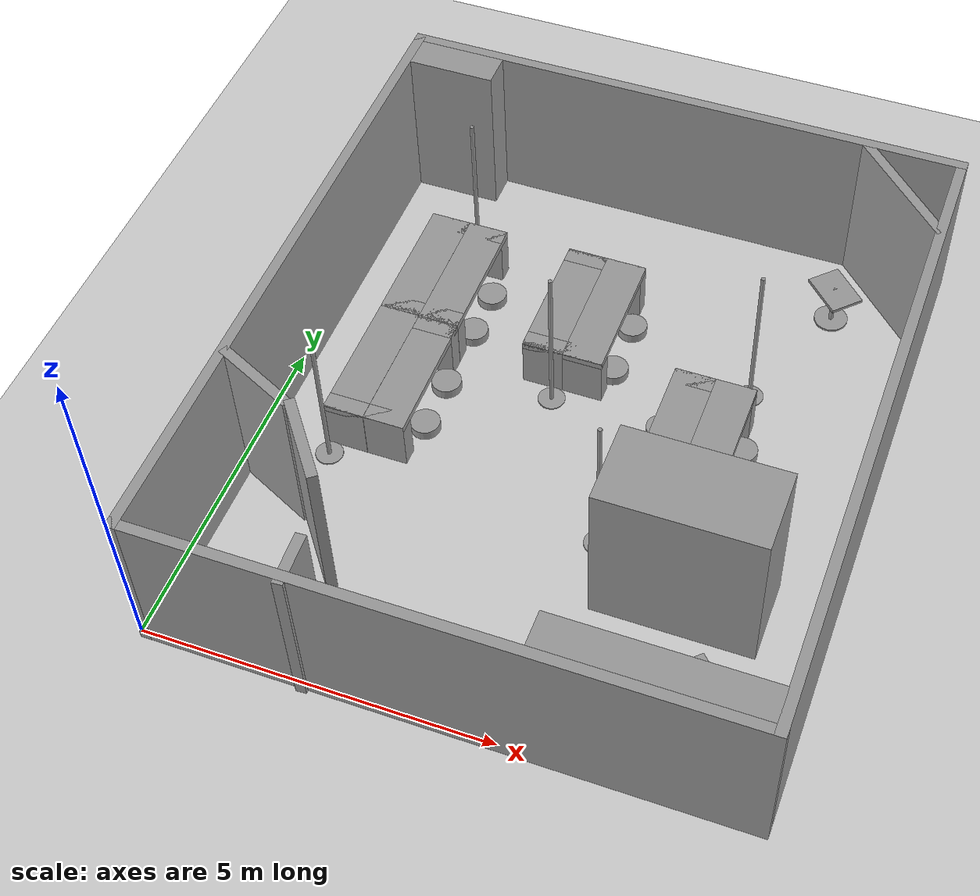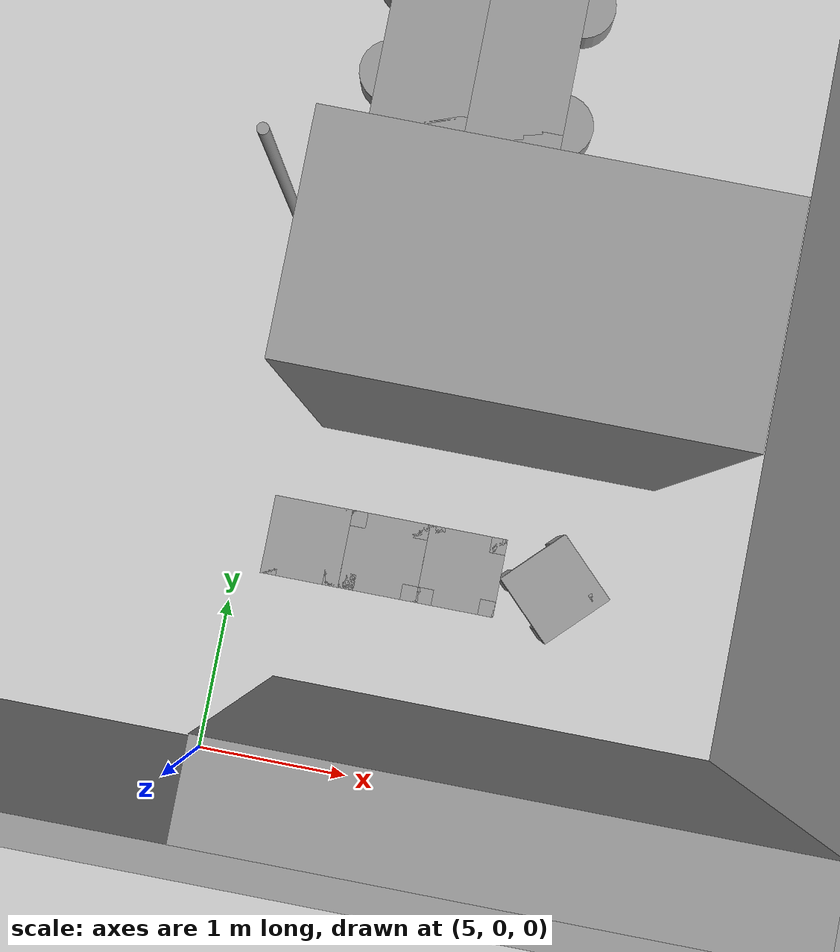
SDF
<sdf version="1.6">
 <world name="default">
  <light name="sun" type="directional">
   <pose>0 0 10 0 -0 0</pose>
   <diffuse>0.8 0.8 0.8 1</diffuse>
   <specular>0.2 0.2 0.2 1</specular>
   <attenuation>
    <range>1000</range>
    <constant>0.9</constant>
    <linear>0.01</linear>
    <quadratic>0.001</quadratic>
   </attenuation>
   <direction>-0.5 0.1 -0.9</direction>
  </light>
  <model name="ground_plane">
   <pose>6.5 0 0 0 -0 0</pose>
   <static>1</static>
   <link name="link">
    <collision name="collision">
     <geometry><plane><normal>0 0 1</normal><size>100 100</size></plane></geometry>
     <surface>
      <contact><collide_bitmask>65535</collide_bitmask></contact>
      <friction><ode><mu>100</mu><mu2>50</mu2></ode></friction>
     </surface>
    </collision>
    <visual name="visual">
     <cast_shadows>0</cast_shadows>
     <geometry><plane><normal>0 0 1</normal><size>100 100</size></plane></geometry>
     <material>
      <script><uri>file://media/materials/scripts/gazebo.material</uri><name>Gazebo/Grey</name></script>
     </material>
    </visual>
   </link>
  </model>
  <gravity>0 0 -9.8</gravity>
  <magnetic_field>6e-06 2.3e-05 -4.2e-05</magnetic_field>
  <atmosphere type="adiabatic"/>
  <physics name="default_physics" default="0" type="ode">
   <max_step_size>0.001</max_step_size>
   <real_time_factor>1</real_time_factor>
   <real_time_update_rate>1000</real_time_update_rate>
  </physics>
  <scene><ambient>0.4 0.4 0.4 1</ambient><background>0.7 0.7 0.7 1</background><shadows>1</shadows></scene>
  <spherical_coordinates>
   <surface_model>EARTH_WGS84</surface_model>
   <latitude_deg>0</latitude_deg>
   <longitude_deg>0</longitude_deg>
   <elevation>0</elevation>
   <heading_deg>0</heading_deg>
  </spherical_coordinates>
  <model name="little_table_SF">
   <link name="link_0">
    <inertial>
     <mass>1</mass>
     <inertia>
      <ixx>0.166667</ixx>
      <ixy>0</ixy>
      <ixz>0</ixz>
      <iyy>0.166667</iyy>
      <iyz>0</iyz>
      <izz>0.166667</izz>
     </inertia>
    </inertial>
    <pose>-0.2 -0.2 -0.04 0 -0 0</pose>
    <visual name="visual">
     <geometry><box><size>0.1 0.1 0.5</size></box></geometry>
     <material>
      <lighting>1</lighting>
      <script><uri>file://media/materials/scripts/gazebo.material</uri><name>Gazebo/Grey</name></script>
      <shader type="pixel"><normal_map>__default__</normal_map></shader>
      <ambient>0.3 0.3 0.3 1</ambient>
      <diffuse>0.7 0.7 0.7 1</diffuse>
      <specular>0.01 0.01 0.01 1</specular>
      <emissive>0 0 0 1</emissive>
     </material>
    </visual>
    <collision name="collision">
     <geometry><box><size>0.1 0.1 0.5</size></box></geometry>
     <surface>
      <friction>
       <ode><mu>1</mu><mu2>1</mu2><fdir1>0 0 0</fdir1><slip1>0</slip1><slip2>0</slip2></ode>
       <torsional>
        <coefficient>1</coefficient>
        <patch_radius>0</patch_radius>
        <surface_radius>0</surface_radius>
        <use_patch_radius>1</use_patch_radius>
        <ode><slip>0</slip></ode>
       </torsional>
      </friction>
      <bounce><restitution_coefficient>0</restitution_coefficient><threshold>1e+06</threshold></bounce>
      <contact>
       <collide_without_contact>0</collide_without_contact>
       <collide_without_contact_bitmask>1</collide_without_contact_bitmask>
       <collide_bitmask>1</collide_bitmask>
       <ode>
        <soft_cfm>0</soft_cfm>
        <soft_erp>0.2</soft_erp>
        <kp>1e+13</kp>
        <kd>1</kd>
        <max_vel>0.01</max_vel>
        <min_depth>0</min_depth>
       </ode>
       <bullet>
        <split_impulse>1</split_impulse>
        <split_impulse_penetration_threshold>-0.01</split_impulse_penetration_threshold>
        <soft_cfm>0</soft_cfm>
        <soft_erp>0.2</soft_erp>
        <kp>1e+13</kp>
        <kd>1</kd>
       </bullet>
      </contact>
     </surface>
    </collision>
   </link>
   <link name="link_0_clone">
    <inertial>
     <mass>1</mass>
     <inertia>
      <ixx>0.166667</ixx>
      <ixy>0</ixy>
      <ixz>0</ixz>
      <iyy>0.166667</iyy>
      <iyz>0</iyz>
      <izz>0.166667</izz>
     </inertia>
    </inertial>
    <pose>0.2 -0.2 -0.04 0 -0 0</pose>
    <visual name="visual">
     <geometry><box><size>0.1 0.1 0.5</size></box></geometry>
     <material>
      <lighting>1</lighting>
      <script><uri>file://media/materials/scripts/gazebo.material</uri><name>Gazebo/Grey</name></script>
      <shader type="pixel"><normal_map>__default__</normal_map></shader>
      <ambient>0.3 0.3 0.3 1</ambient>
      <diffuse>0.7 0.7 0.7 1</diffuse>
      <specular>0.01 0.01 0.01 1</specular>
      <emissive>0 0 0 1</emissive>
     </material>
    </visual>
    <collision name="collision">
     <geometry><box><size>0.1 0.1 0.5</size></box></geometry>
     <surface>
      <friction>
       <ode><mu>1</mu><mu2>1</mu2><fdir1>0 0 0</fdir1><slip1>0</slip1><slip2>0</slip2></ode>
       <torsional>
        <coefficient>1</coefficient>
        <patch_radius>0</patch_radius>
        <surface_radius>0</surface_radius>
        <use_patch_radius>1</use_patch_radius>
        <ode><slip>0</slip></ode>
       </torsional>
      </friction>
      <bounce><restitution_coefficient>0</restitution_coefficient><threshold>1e+06</threshold></bounce>
      <contact>
       <collide_without_contact>0</collide_without_contact>
       <collide_without_contact_bitmask>1</collide_without_contact_bitmask>
       <collide_bitmask>1</collide_bitmask>
       <ode>
        <soft_cfm>0</soft_cfm>
        <soft_erp>0.2</soft_erp>
        <kp>1e+13</kp>
        <kd>1</kd>
        <max_vel>0.01</max_vel>
        <min_depth>0</min_depth>
       </ode>
       <bullet>
        <split_impulse>1</split_impulse>
        <split_impulse_penetration_threshold>-0.01</split_impulse_penetration_threshold>
        <soft_cfm>0</soft_cfm>
        <soft_erp>0.2</soft_erp>
        <kp>1e+13</kp>
        <kd>1</kd>
       </bullet>
      </contact>
     </surface>
    </collision>
   </link>
   <link name="link_0_clone_0">
    <inertial>
     <mass>1</mass>
     <inertia>
      <ixx>0.166667</ixx>
      <ixy>0</ixy>
      <ixz>0</ixz>
      <iyy>0.166667</iyy>
      <iyz>0</iyz>
      <izz>0.166667</izz>
     </inertia>
    </inertial>
    <pose>-0.2 0.2 -0.04 0 -0 0</pose>
    <visual name="visual">
     <geometry><box><size>0.1 0.1 0.5</size></box></geometry>
     <material>
      <lighting>1</lighting>
      <script><uri>file://media/materials/scripts/gazebo.material</uri><name>Gazebo/Grey</name></script>
      <shader type="pixel"><normal_map>__default__</normal_map></shader>
      <ambient>0.3 0.3 0.3 1</ambient>
      <diffuse>0.7 0.7 0.7 1</diffuse>
      <specular>0.01 0.01 0.01 1</specular>
      <emissive>0 0 0 1</emissive>
     </material>
    </visual>
    <collision name="collision">
     <geometry><box><size>0.1 0.1 0.5</size></box></geometry>
     <surface>
      <friction>
       <ode><mu>1</mu><mu2>1</mu2><fdir1>0 0 0</fdir1><slip1>0</slip1><slip2>0</slip2></ode>
       <torsional>
        <coefficient>1</coefficient>
        <patch_radius>0</patch_radius>
        <surface_radius>0</surface_radius>
        <use_patch_radius>1</use_patch_radius>
        <ode><slip>0</slip></ode>
       </torsional>
      </friction>
      <bounce><restitution_coefficient>0</restitution_coefficient><threshold>1e+06</threshold></bounce>
      <contact>
       <collide_without_contact>0</collide_without_contact>
       <collide_without_contact_bitmask>1</collide_without_contact_bitmask>
       <collide_bitmask>1</collide_bitmask>
       <ode>
        <soft_cfm>0</soft_cfm>
        <soft_erp>0.2</soft_erp>
        <kp>1e+13</kp>
        <kd>1</kd>
        <max_vel>0.01</max_vel>
        <min_depth>0</min_depth>
       </ode>
       <bullet>
        <split_impulse>1</split_impulse>
        <split_impulse_penetration_threshold>-0.01</split_impulse_penetration_threshold>
        <soft_cfm>0</soft_cfm>
        <soft_erp>0.2</soft_erp>
        <kp>1e+13</kp>
        <kd>1</kd>
       </bullet>
      </contact>
     </surface>
    </collision>
   </link>
   <link name="link_0_clone_1">
    <inertial>
     <mass>1</mass>
     <inertia>
      <ixx>0.166667</ixx>
      <ixy>0</ixy>
      <ixz>0</ixz>
      <iyy>0.166667</iyy>
      <iyz>0</iyz>
      <izz>0.166667</izz>
     </inertia>
    </inertial>
    <pose>0.2 0.2 -0.04 0 -0 0</pose>
    <visual name="visual">
     <geometry><box><size>0.1 0.1 0.5</size></box></geometry>
     <material>
      <lighting>1</lighting>
      <script><uri>file://media/materials/scripts/gazebo.material</uri><name>Gazebo/Grey</name></script>
      <shader type="pixel"><normal_map>__default__</normal_map></shader>
      <ambient>0.3 0.3 0.3 1</ambient>
      <diffuse>0.7 0.7 0.7 1</diffuse>
      <specular>0.01 0.01 0.01 1</specular>
      <emissive>0 0 0 1</emissive>
     </material>
    </visual>
    <collision name="collision">
     <geometry><box><size>0.1 0.1 0.5</size></box></geometry>
     <surface>
      <friction>
       <ode><mu>1</mu><mu2>1</mu2><fdir1>0 0 0</fdir1><slip1>0</slip1><slip2>0</slip2></ode>
       <torsional>
        <coefficient>1</coefficient>
        <patch_radius>0</patch_radius>
        <surface_radius>0</surface_radius>
        <use_patch_radius>1</use_patch_radius>
        <ode><slip>0</slip></ode>
       </torsional>
      </friction>
      <bounce><restitution_coefficient>0</restitution_coefficient><threshold>1e+06</threshold></bounce>
      <contact>
       <collide_without_contact>0</collide_without_contact>
       <collide_without_contact_bitmask>1</collide_without_contact_bitmask>
       <collide_bitmask>1</collide_bitmask>
       <ode>
        <soft_cfm>0</soft_cfm>
        <soft_erp>0.2</soft_erp>
        <kp>1e+13</kp>
        <kd>1</kd>
        <max_vel>0.01</max_vel>
        <min_depth>0</min_depth>
       </ode>
       <bullet>
        <split_impulse>1</split_impulse>
        <split_impulse_penetration_threshold>-0.01</split_impulse_penetration_threshold>
        <soft_cfm>0</soft_cfm>
        <soft_erp>0.2</soft_erp>
        <kp>1e+13</kp>
        <kd>1</kd>
       </bullet>
      </contact>
     </surface>
    </collision>
   </link>
   <link name="link_1">
    <inertial>
     <mass>1</mass>
     <inertia>
      <ixx>0.166667</ixx>
      <ixy>0</ixy>
      <ixz>0</ixz>
      <iyy>0.166667</iyy>
      <iyz>0</iyz>
      <izz>0.166667</izz>
     </inertia>
    </inertial>
    <pose>0 0 0.16 0 -0 0</pose>
    <visual name="visual">
     <geometry><box><size>0.5 0.5 0.1</size></box></geometry>
     <material>
      <lighting>1</lighting>
      <script><uri>file://media/materials/scripts/gazebo.material</uri><name>Gazebo/Grey</name></script>
      <shader type="pixel"><normal_map>__default__</normal_map></shader>
      <ambient>0.3 0.3 0.3 1</ambient>
      <diffuse>0.7 0.7 0.7 1</diffuse>
      <specular>0.01 0.01 0.01 1</specular>
      <emissive>0 0 0 1</emissive>
     </material>
    </visual>
    <collision name="collision">
     <geometry><box><size>0.5 0.5 0.1</size></box></geometry>
     <surface>
      <friction>
       <ode><mu>1</mu><mu2>1</mu2><fdir1>0 0 0</fdir1><slip1>0</slip1><slip2>0</slip2></ode>
       <torsional>
        <coefficient>1</coefficient>
        <patch_radius>0</patch_radius>
        <surface_radius>0</surface_radius>
        <use_patch_radius>1</use_patch_radius>
        <ode><slip>0</slip></ode>
       </torsional>
      </friction>
      <bounce><restitution_coefficient>0</restitution_coefficient><threshold>1e+06</threshold></bounce>
      <contact>
       <collide_without_contact>0</collide_without_contact>
       <collide_without_contact_bitmask>1</collide_without_contact_bitmask>
       <collide_bitmask>1</collide_bitmask>
       <ode>
        <soft_cfm>0</soft_cfm>
        <soft_erp>0.2</soft_erp>
        <kp>1e+13</kp>
        <kd>1</kd>
        <max_vel>0.01</max_vel>
        <min_depth>0</min_depth>
       </ode>
       <bullet>
        <split_impulse>1</split_impulse>
        <split_impulse_penetration_threshold>-0.01</split_impulse_penetration_threshold>
        <soft_cfm>0</soft_cfm>
        <soft_erp>0.2</soft_erp>
        <kp>1e+13</kp>
        <kd>1</kd>
       </bullet>
      </contact>
     </surface>
    </collision>
   </link>
   <joint name="link_1_JOINT_0" type="fixed">
    <parent>link_1</parent>
    <child>link_0_clone_0</child>
    <physics>
     <ode><limit><cfm>0</cfm><erp>0.2</erp></limit><suspension><cfm>0</cfm><erp>0.2</erp></suspension></ode>
    </physics>
   </joint>
   <joint name="link_1_JOINT_1" type="fixed">
    <parent>link_1</parent>
    <child>link_0</child>
    <physics>
     <ode><limit><cfm>0</cfm><erp>0.2</erp></limit><suspension><cfm>0</cfm><erp>0.2</erp></suspension></ode>
    </physics>
   </joint>
   <joint name="link_1_JOINT_2" type="fixed">
    <parent>link_1</parent>
    <child>link_0_clone_1</child>
    <physics>
     <ode><limit><cfm>0</cfm><erp>0.2</erp></limit><suspension><cfm>0</cfm><erp>0.2</erp></suspension></ode>
    </physics>
   </joint>
   <joint name="link_1_JOINT_3" type="fixed">
    <parent>link_1</parent>
    <child>link_0_clone</child>
    <physics>
     <ode><limit><cfm>0</cfm><erp>0.2</erp></limit><suspension><cfm>0</cfm><erp>0.2</erp></suspension></ode>
    </physics>
   </joint>
   <static>0</static>
   <pose>5.49895 1.49965 0.29 -3e-06 2e-06 -8e-06</pose>
  </model>
  <model name="little_table_SF_clone">
   <link name="link_0">
    <inertial>
     <mass>1</mass>
     <inertia>
      <ixx>0.166667</ixx>
      <ixy>0</ixy>
      <ixz>0</ixz>
      <iyy>0.166667</iyy>
      <iyz>0</iyz>
      <izz>0.166667</izz>
     </inertia>
    </inertial>
    <pose>-0.2 -0.2 -0.04 0 -0 0</pose>
    <visual name="visual">
     <geometry><box><size>0.1 0.1 0.5</size></box></geometry>
     <material>
      <lighting>1</lighting>
      <script><uri>file://media/materials/scripts/gazebo.material</uri><name>Gazebo/Grey</name></script>
      <shader type="pixel"><normal_map>__default__</normal_map></shader>
      <ambient>0.3 0.3 0.3 1</ambient>
      <diffuse>0.7 0.7 0.7 1</diffuse>
      <specular>0.01 0.01 0.01 1</specular>
      <emissive>0 0 0 1</emissive>
     </material>
    </visual>
    <collision name="collision">
     <geometry><box><size>0.1 0.1 0.5</size></box></geometry>
     <surface>
      <friction>
       <ode><mu>1</mu><mu2>1</mu2><fdir1>0 0 0</fdir1><slip1>0</slip1><slip2>0</slip2></ode>
       <torsional>
        <coefficient>1</coefficient>
        <patch_radius>0</patch_radius>
        <surface_radius>0</surface_radius>
        <use_patch_radius>1</use_patch_radius>
        <ode><slip>0</slip></ode>
       </torsional>
      </friction>
      <bounce><restitution_coefficient>0</restitution_coefficient><threshold>1e+06</threshold></bounce>
      <contact>
       <collide_without_contact>0</collide_without_contact>
       <collide_without_contact_bitmask>1</collide_without_contact_bitmask>
       <collide_bitmask>1</collide_bitmask>
       <ode>
        <soft_cfm>0</soft_cfm>
        <soft_erp>0.2</soft_erp>
        <kp>1e+13</kp>
        <kd>1</kd>
        <max_vel>0.01</max_vel>
        <min_depth>0</min_depth>
       </ode>
       <bullet>
        <split_impulse>1</split_impulse>
        <split_impulse_penetration_threshold>-0.01</split_impulse_penetration_threshold>
        <soft_cfm>0</soft_cfm>
        <soft_erp>0.2</soft_erp>
        <kp>1e+13</kp>
        <kd>1</kd>
       </bullet>
      </contact>
     </surface>
    </collision>
   </link>
   <link name="link_0_clone">
    <inertial>
     <mass>1</mass>
     <inertia>
      <ixx>0.166667</ixx>
      <ixy>0</ixy>
      <ixz>0</ixz>
      <iyy>0.166667</iyy>
      <iyz>0</iyz>
      <izz>0.166667</izz>
     </inertia>
    </inertial>
    <pose>0.2 -0.2 -0.04 0 -0 0</pose>
    <visual name="visual">
     <geometry><box><size>0.1 0.1 0.5</size></box></geometry>
     <material>
      <lighting>1</lighting>
      <script><uri>file://media/materials/scripts/gazebo.material</uri><name>Gazebo/Grey</name></script>
      <shader type="pixel"><normal_map>__default__</normal_map></shader>
      <ambient>0.3 0.3 0.3 1</ambient>
      <diffuse>0.7 0.7 0.7 1</diffuse>
      <specular>0.01 0.01 0.01 1</specular>
      <emissive>0 0 0 1</emissive>
     </material>
    </visual>
    <collision name="collision">
     <geometry><box><size>0.1 0.1 0.5</size></box></geometry>
     <surface>
      <friction>
       <ode><mu>1</mu><mu2>1</mu2><fdir1>0 0 0</fdir1><slip1>0</slip1><slip2>0</slip2></ode>
       <torsional>
        <coefficient>1</coefficient>
        <patch_radius>0</patch_radius>
        <surface_radius>0</surface_radius>
        <use_patch_radius>1</use_patch_radius>
        <ode><slip>0</slip></ode>
       </torsional>
      </friction>
      <bounce><restitution_coefficient>0</restitution_coefficient><threshold>1e+06</threshold></bounce>
      <contact>
       <collide_without_contact>0</collide_without_contact>
       <collide_without_contact_bitmask>1</collide_without_contact_bitmask>
       <collide_bitmask>1</collide_bitmask>
       <ode>
        <soft_cfm>0</soft_cfm>
        <soft_erp>0.2</soft_erp>
        <kp>1e+13</kp>
        <kd>1</kd>
        <max_vel>0.01</max_vel>
        <min_depth>0</min_depth>
       </ode>
       <bullet>
        <split_impulse>1</split_impulse>
        <split_impulse_penetration_threshold>-0.01</split_impulse_penetration_threshold>
        <soft_cfm>0</soft_cfm>
        <soft_erp>0.2</soft_erp>
        <kp>1e+13</kp>
        <kd>1</kd>
       </bullet>
      </contact>
     </surface>
    </collision>
   </link>
   <link name="link_0_clone_0">
    <inertial>
     <mass>1</mass>
     <inertia>
      <ixx>0.166667</ixx>
      <ixy>0</ixy>
      <ixz>0</ixz>
      <iyy>0.166667</iyy>
      <iyz>0</iyz>
      <izz>0.166667</izz>
     </inertia>
    </inertial>
    <pose>-0.2 0.2 -0.04 0 -0 0</pose>
    <visual name="visual">
     <geometry><box><size>0.1 0.1 0.5</size></box></geometry>
     <material>
      <lighting>1</lighting>
      <script><uri>file://media/materials/scripts/gazebo.material</uri><name>Gazebo/Grey</name></script>
      <shader type="pixel"><normal_map>__default__</normal_map></shader>
      <ambient>0.3 0.3 0.3 1</ambient>
      <diffuse>0.7 0.7 0.7 1</diffuse>
      <specular>0.01 0.01 0.01 1</specular>
      <emissive>0 0 0 1</emissive>
     </material>
    </visual>
    <collision name="collision">
     <geometry><box><size>0.1 0.1 0.5</size></box></geometry>
     <surface>
      <friction>
       <ode><mu>1</mu><mu2>1</mu2><fdir1>0 0 0</fdir1><slip1>0</slip1><slip2>0</slip2></ode>
       <torsional>
        <coefficient>1</coefficient>
        <patch_radius>0</patch_radius>
        <surface_radius>0</surface_radius>
        <use_patch_radius>1</use_patch_radius>
        <ode><slip>0</slip></ode>
       </torsional>
      </friction>
      <bounce><restitution_coefficient>0</restitution_coefficient><threshold>1e+06</threshold></bounce>
      <contact>
       <collide_without_contact>0</collide_without_contact>
       <collide_without_contact_bitmask>1</collide_without_contact_bitmask>
       <collide_bitmask>1</collide_bitmask>
       <ode>
        <soft_cfm>0</soft_cfm>
        <soft_erp>0.2</soft_erp>
        <kp>1e+13</kp>
        <kd>1</kd>
        <max_vel>0.01</max_vel>
        <min_depth>0</min_depth>
       </ode>
       <bullet>
        <split_impulse>1</split_impulse>
        <split_impulse_penetration_threshold>-0.01</split_impulse_penetration_threshold>
        <soft_cfm>0</soft_cfm>
        <soft_erp>0.2</soft_erp>
        <kp>1e+13</kp>
        <kd>1</kd>
       </bullet>
      </contact>
     </surface>
    </collision>
   </link>
   <link name="link_0_clone_1">
    <inertial>
     <mass>1</mass>
     <inertia>
      <ixx>0.166667</ixx>
      <ixy>0</ixy>
      <ixz>0</ixz>
      <iyy>0.166667</iyy>
      <iyz>0</iyz>
      <izz>0.166667</izz>
     </inertia>
    </inertial>
    <pose>0.2 0.2 -0.04 0 -0 0</pose>
    <visual name="visual">
     <geometry><box><size>0.1 0.1 0.5</size></box></geometry>
     <material>
      <lighting>1</lighting>
      <script><uri>file://media/materials/scripts/gazebo.material</uri><name>Gazebo/Grey</name></script>
      <shader type="pixel"><normal_map>__default__</normal_map></shader>
      <ambient>0.3 0.3 0.3 1</ambient>
      <diffuse>0.7 0.7 0.7 1</diffuse>
      <specular>0.01 0.01 0.01 1</specular>
      <emissive>0 0 0 1</emissive>
     </material>
    </visual>
    <collision name="collision">
     <geometry><box><size>0.1 0.1 0.5</size></box></geometry>
     <surface>
      <friction>
       <ode><mu>1</mu><mu2>1</mu2><fdir1>0 0 0</fdir1><slip1>0</slip1><slip2>0</slip2></ode>
       <torsional>
        <coefficient>1</coefficient>
        <patch_radius>0</patch_radius>
        <surface_radius>0</surface_radius>
        <use_patch_radius>1</use_patch_radius>
        <ode><slip>0</slip></ode>
       </torsional>
      </friction>
      <bounce><restitution_coefficient>0</restitution_coefficient><threshold>1e+06</threshold></bounce>
      <contact>
       <collide_without_contact>0</collide_without_contact>
       <collide_without_contact_bitmask>1</collide_without_contact_bitmask>
       <collide_bitmask>1</collide_bitmask>
       <ode>
        <soft_cfm>0</soft_cfm>
        <soft_erp>0.2</soft_erp>
        <kp>1e+13</kp>
        <kd>1</kd>
        <max_vel>0.01</max_vel>
        <min_depth>0</min_depth>
       </ode>
       <bullet>
        <split_impulse>1</split_impulse>
        <split_impulse_penetration_threshold>-0.01</split_impulse_penetration_threshold>
        <soft_cfm>0</soft_cfm>
        <soft_erp>0.2</soft_erp>
        <kp>1e+13</kp>
        <kd>1</kd>
       </bullet>
      </contact>
     </surface>
    </collision>
   </link>
   <link name="link_1">
    <inertial>
     <mass>1</mass>
     <inertia>
      <ixx>0.166667</ixx>
      <ixy>0</ixy>
      <ixz>0</ixz>
      <iyy>0.166667</iyy>
      <iyz>0</iyz>
      <izz>0.166667</izz>
     </inertia>
    </inertial>
    <pose>0 0 0.16 0 -0 0</pose>
    <visual name="visual">
     <geometry><box><size>0.5 0.5 0.1</size></box></geometry>
     <material>
      <lighting>1</lighting>
      <script><uri>file://media/materials/scripts/gazebo.material</uri><name>Gazebo/Grey</name></script>
      <shader type="pixel"><normal_map>__default__</normal_map></shader>
      <ambient>0.3 0.3 0.3 1</ambient>
      <diffuse>0.7 0.7 0.7 1</diffuse>
      <specular>0.01 0.01 0.01 1</specular>
      <emissive>0 0 0 1</emissive>
     </material>
    </visual>
    <collision name="collision">
     <geometry><box><size>0.5 0.5 0.1</size></box></geometry>
     <surface>
      <friction>
       <ode><mu>1</mu><mu2>1</mu2><fdir1>0 0 0</fdir1><slip1>0</slip1><slip2>0</slip2></ode>
       <torsional>
        <coefficient>1</coefficient>
        <patch_radius>0</patch_radius>
        <surface_radius>0</surface_radius>
        <use_patch_radius>1</use_patch_radius>
        <ode><slip>0</slip></ode>
       </torsional>
      </friction>
      <bounce><restitution_coefficient>0</restitution_coefficient><threshold>1e+06</threshold></bounce>
      <contact>
       <collide_without_contact>0</collide_without_contact>
       <collide_without_contact_bitmask>1</collide_without_contact_bitmask>
       <collide_bitmask>1</collide_bitmask>
       <ode>
        <soft_cfm>0</soft_cfm>
        <soft_erp>0.2</soft_erp>
        <kp>1e+13</kp>
        <kd>1</kd>
        <max_vel>0.01</max_vel>
        <min_depth>0</min_depth>
       </ode>
       <bullet>
        <split_impulse>1</split_impulse>
        <split_impulse_penetration_threshold>-0.01</split_impulse_penetration_threshold>
        <soft_cfm>0</soft_cfm>
        <soft_erp>0.2</soft_erp>
        <kp>1e+13</kp>
        <kd>1</kd>
       </bullet>
      </contact>
     </surface>
    </collision>
   </link>
   <joint name="link_1_JOINT_0" type="fixed">
    <parent>link_1</parent>
    <child>link_0_clone_0</child>
    <physics>
     <ode><limit><cfm>0</cfm><erp>0.2</erp></limit><suspension><cfm>0</cfm><erp>0.2</erp></suspension></ode>
    </physics>
   </joint>
   <joint name="link_1_JOINT_1" type="fixed">
    <parent>link_1</parent>
    <child>link_0</child>
    <physics>
     <ode><limit><cfm>0</cfm><erp>0.2</erp></limit><suspension><cfm>0</cfm><erp>0.2</erp></suspension></ode>
    </physics>
   </joint>
   <joint name="link_1_JOINT_2" type="fixed">
    <parent>link_1</parent>
    <child>link_0_clone_1</child>
    <physics>
     <ode><limit><cfm>0</cfm><erp>0.2</erp></limit><suspension><cfm>0</cfm><erp>0.2</erp></suspension></ode>
    </physics>
   </joint>
   <joint name="link_1_JOINT_3" type="fixed">
    <parent>link_1</parent>
    <child>link_0_clone</child>
    <physics>
     <ode><limit><cfm>0</cfm><erp>0.2</erp></limit><suspension><cfm>0</cfm><erp>0.2</erp></suspension></ode>
    </physics>
   </joint>
   <static>0</static>
   <pose>5.99916 1.50019 0.290001 1e-06 -2e-06 -0.000167</pose>
  </model>
  <model name="little_table_SF_clone_clone">
   <link name="link_0">
    <inertial>
     <mass>1</mass>
     <inertia>
      <ixx>0.166667</ixx>
      <ixy>0</ixy>
      <ixz>0</ixz>
      <iyy>0.166667</iyy>
      <iyz>0</iyz>
      <izz>0.166667</izz>
     </inertia>
    </inertial>
    <pose>-0.2 -0.2 -0.04 0 -0 0</pose>
    <visual name="visual">
     <geometry><box><size>0.1 0.1 0.5</size></box></geometry>
     <material>
      <lighting>1</lighting>
      <script><uri>file://media/materials/scripts/gazebo.material</uri><name>Gazebo/Grey</name></script>
      <shader type="pixel"><normal_map>__default__</normal_map></shader>
      <ambient>0.3 0.3 0.3 1</ambient>
      <diffuse>0.7 0.7 0.7 1</diffuse>
      <specular>0.01 0.01 0.01 1</specular>
      <emissive>0 0 0 1</emissive>
     </material>
    </visual>
    <collision name="collision">
     <geometry><box><size>0.1 0.1 0.5</size></box></geometry>
     <surface>
      <friction>
       <ode><mu>1</mu><mu2>1</mu2><fdir1>0 0 0</fdir1><slip1>0</slip1><slip2>0</slip2></ode>
       <torsional>
        <coefficient>1</coefficient>
        <patch_radius>0</patch_radius>
        <surface_radius>0</surface_radius>
        <use_patch_radius>1</use_patch_radius>
        <ode><slip>0</slip></ode>
       </torsional>
      </friction>
      <bounce><restitution_coefficient>0</restitution_coefficient><threshold>1e+06</threshold></bounce>
      <contact>
       <collide_without_contact>0</collide_without_contact>
       <collide_without_contact_bitmask>1</collide_without_contact_bitmask>
       <collide_bitmask>1</collide_bitmask>
       <ode>
        <soft_cfm>0</soft_cfm>
        <soft_erp>0.2</soft_erp>
        <kp>1e+13</kp>
        <kd>1</kd>
        <max_vel>0.01</max_vel>
        <min_depth>0</min_depth>
       </ode>
       <bullet>
        <split_impulse>1</split_impulse>
        <split_impulse_penetration_threshold>-0.01</split_impulse_penetration_threshold>
        <soft_cfm>0</soft_cfm>
        <soft_erp>0.2</soft_erp>
        <kp>1e+13</kp>
        <kd>1</kd>
       </bullet>
      </contact>
     </surface>
    </collision>
   </link>
   <link name="link_0_clone">
    <inertial>
     <mass>1</mass>
     <inertia>
      <ixx>0.166667</ixx>
      <ixy>0</ixy>
      <ixz>0</ixz>
      <iyy>0.166667</iyy>
      <iyz>0</iyz>
      <izz>0.166667</izz>
     </inertia>
    </inertial>
    <pose>0.2 -0.2 -0.04 0 -0 0</pose>
    <visual name="visual">
     <geometry><box><size>0.1 0.1 0.5</size></box></geometry>
     <material>
      <lighting>1</lighting>
      <script><uri>file://media/materials/scripts/gazebo.material</uri><name>Gazebo/Grey</name></script>
      <shader type="pixel"><normal_map>__default__</normal_map></shader>
      <ambient>0.3 0.3 0.3 1</ambient>
      <diffuse>0.7 0.7 0.7 1</diffuse>
      <specular>0.01 0.01 0.01 1</specular>
      <emissive>0 0 0 1</emissive>
     </material>
    </visual>
    <collision name="collision">
     <geometry><box><size>0.1 0.1 0.5</size></box></geometry>
     <surface>
      <friction>
       <ode><mu>1</mu><mu2>1</mu2><fdir1>0 0 0</fdir1><slip1>0</slip1><slip2>0</slip2></ode>
       <torsional>
        <coefficient>1</coefficient>
        <patch_radius>0</patch_radius>
        <surface_radius>0</surface_radius>
        <use_patch_radius>1</use_patch_radius>
        <ode><slip>0</slip></ode>
       </torsional>
      </friction>
      <bounce><restitution_coefficient>0</restitution_coefficient><threshold>1e+06</threshold></bounce>
      <contact>
       <collide_without_contact>0</collide_without_contact>
       <collide_without_contact_bitmask>1</collide_without_contact_bitmask>
       <collide_bitmask>1</collide_bitmask>
       <ode>
        <soft_cfm>0</soft_cfm>
        <soft_erp>0.2</soft_erp>
        <kp>1e+13</kp>
        <kd>1</kd>
        <max_vel>0.01</max_vel>
        <min_depth>0</min_depth>
       </ode>
       <bullet>
        <split_impulse>1</split_impulse>
        <split_impulse_penetration_threshold>-0.01</split_impulse_penetration_threshold>
        <soft_cfm>0</soft_cfm>
        <soft_erp>0.2</soft_erp>
        <kp>1e+13</kp>
        <kd>1</kd>
       </bullet>
      </contact>
     </surface>
    </collision>
   </link>
   <link name="link_0_clone_0">
    <inertial>
     <mass>1</mass>
     <inertia>
      <ixx>0.166667</ixx>
      <ixy>0</ixy>
      <ixz>0</ixz>
      <iyy>0.166667</iyy>
      <iyz>0</iyz>
      <izz>0.166667</izz>
     </inertia>
    </inertial>
    <pose>-0.2 0.2 -0.04 0 -0 0</pose>
    <visual name="visual">
     <geometry><box><size>0.1 0.1 0.5</size></box></geometry>
     <material>
      <lighting>1</lighting>
      <script><uri>file://media/materials/scripts/gazebo.material</uri><name>Gazebo/Grey</name></script>
      <shader type="pixel"><normal_map>__default__</normal_map></shader>
      <ambient>0.3 0.3 0.3 1</ambient>
      <diffuse>0.7 0.7 0.7 1</diffuse>
      <specular>0.01 0.01 0.01 1</specular>
      <emissive>0 0 0 1</emissive>
     </material>
    </visual>
    <collision name="collision">
     <geometry><box><size>0.1 0.1 0.5</size></box></geometry>
     <surface>
      <friction>
       <ode><mu>1</mu><mu2>1</mu2><fdir1>0 0 0</fdir1><slip1>0</slip1><slip2>0</slip2></ode>
       <torsional>
        <coefficient>1</coefficient>
        <patch_radius>0</patch_radius>
        <surface_radius>0</surface_radius>
        <use_patch_radius>1</use_patch_radius>
        <ode><slip>0</slip></ode>
       </torsional>
      </friction>
      <bounce><restitution_coefficient>0</restitution_coefficient><threshold>1e+06</threshold></bounce>
      <contact>
       <collide_without_contact>0</collide_without_contact>
       <collide_without_contact_bitmask>1</collide_without_contact_bitmask>
       <collide_bitmask>1</collide_bitmask>
       <ode>
        <soft_cfm>0</soft_cfm>
        <soft_erp>0.2</soft_erp>
        <kp>1e+13</kp>
        <kd>1</kd>
        <max_vel>0.01</max_vel>
        <min_depth>0</min_depth>
       </ode>
       <bullet>
        <split_impulse>1</split_impulse>
        <split_impulse_penetration_threshold>-0.01</split_impulse_penetration_threshold>
        <soft_cfm>0</soft_cfm>
        <soft_erp>0.2</soft_erp>
        <kp>1e+13</kp>
        <kd>1</kd>
       </bullet>
      </contact>
     </surface>
    </collision>
   </link>
   <link name="link_0_clone_1">
    <inertial>
     <mass>1</mass>
     <inertia>
      <ixx>0.166667</ixx>
      <ixy>0</ixy>
      <ixz>0</ixz>
      <iyy>0.166667</iyy>
      <iyz>0</iyz>
      <izz>0.166667</izz>
     </inertia>
    </inertial>
    <pose>0.2 0.2 -0.04 0 -0 0</pose>
    <visual name="visual">
     <geometry><box><size>0.1 0.1 0.5</size></box></geometry>
     <material>
      <lighting>1</lighting>
      <script><uri>file://media/materials/scripts/gazebo.material</uri><name>Gazebo/Grey</name></script>
      <shader type="pixel"><normal_map>__default__</normal_map></shader>
      <ambient>0.3 0.3 0.3 1</ambient>
      <diffuse>0.7 0.7 0.7 1</diffuse>
      <specular>0.01 0.01 0.01 1</specular>
      <emissive>0 0 0 1</emissive>
     </material>
    </visual>
    <collision name="collision">
     <geometry><box><size>0.1 0.1 0.5</size></box></geometry>
     <surface>
      <friction>
       <ode><mu>1</mu><mu2>1</mu2><fdir1>0 0 0</fdir1><slip1>0</slip1><slip2>0</slip2></ode>
       <torsional>
        <coefficient>1</coefficient>
        <patch_radius>0</patch_radius>
        <surface_radius>0</surface_radius>
        <use_patch_radius>1</use_patch_radius>
        <ode><slip>0</slip></ode>
       </torsional>
      </friction>
      <bounce><restitution_coefficient>0</restitution_coefficient><threshold>1e+06</threshold></bounce>
      <contact>
       <collide_without_contact>0</collide_without_contact>
       <collide_without_contact_bitmask>1</collide_without_contact_bitmask>
       <collide_bitmask>1</collide_bitmask>
       <ode>
        <soft_cfm>0</soft_cfm>
        <soft_erp>0.2</soft_erp>
        <kp>1e+13</kp>
        <kd>1</kd>
        <max_vel>0.01</max_vel>
        <min_depth>0</min_depth>
       </ode>
       <bullet>
        <split_impulse>1</split_impulse>
        <split_impulse_penetration_threshold>-0.01</split_impulse_penetration_threshold>
        <soft_cfm>0</soft_cfm>
        <soft_erp>0.2</soft_erp>
        <kp>1e+13</kp>
        <kd>1</kd>
       </bullet>
      </contact>
     </surface>
    </collision>
   </link>
   <link name="link_1">
    <inertial>
     <mass>1</mass>
     <inertia>
      <ixx>0.166667</ixx>
      <ixy>0</ixy>
      <ixz>0</ixz>
      <iyy>0.166667</iyy>
      <iyz>0</iyz>
      <izz>0.166667</izz>
     </inertia>
    </inertial>
    <pose>0 0 0.16 0 -0 0</pose>
    <visual name="visual">
     <geometry><box><size>0.5 0.5 0.1</size></box></geometry>
     <material>
      <lighting>1</lighting>
      <script><uri>file://media/materials/scripts/gazebo.material</uri><name>Gazebo/Grey</name></script>
      <shader type="pixel"><normal_map>__default__</normal_map></shader>
      <ambient>0.3 0.3 0.3 1</ambient>
      <diffuse>0.7 0.7 0.7 1</diffuse>
      <specular>0.01 0.01 0.01 1</specular>
      <emissive>0 0 0 1</emissive>
     </material>
    </visual>
    <collision name="collision">
     <geometry><box><size>0.5 0.5 0.1</size></box></geometry>
     <surface>
      <friction>
       <ode><mu>1</mu><mu2>1</mu2><fdir1>0 0 0</fdir1><slip1>0</slip1><slip2>0</slip2></ode>
       <torsional>
        <coefficient>1</coefficient>
        <patch_radius>0</patch_radius>
        <surface_radius>0</surface_radius>
        <use_patch_radius>1</use_patch_radius>
        <ode><slip>0</slip></ode>
       </torsional>
      </friction>
      <bounce><restitution_coefficient>0</restitution_coefficient><threshold>1e+06</threshold></bounce>
      <contact>
       <collide_without_contact>0</collide_without_contact>
       <collide_without_contact_bitmask>1</collide_without_contact_bitmask>
       <collide_bitmask>1</collide_bitmask>
       <ode>
        <soft_cfm>0</soft_cfm>
        <soft_erp>0.2</soft_erp>
        <kp>1e+13</kp>
        <kd>1</kd>
        <max_vel>0.01</max_vel>
        <min_depth>0</min_depth>
       </ode>
       <bullet>
        <split_impulse>1</split_impulse>
        <split_impulse_penetration_threshold>-0.01</split_impulse_penetration_threshold>
        <soft_cfm>0</soft_cfm>
        <soft_erp>0.2</soft_erp>
        <kp>1e+13</kp>
        <kd>1</kd>
       </bullet>
      </contact>
     </surface>
    </collision>
   </link>
   <joint name="link_1_JOINT_0" type="fixed">
    <parent>link_1</parent>
    <child>link_0_clone_0</child>
    <physics>
     <ode><limit><cfm>0</cfm><erp>0.2</erp></limit><suspension><cfm>0</cfm><erp>0.2</erp></suspension></ode>
    </physics>
   </joint>
   <joint name="link_1_JOINT_1" type="fixed">
    <parent>link_1</parent>
    <child>link_0</child>
    <physics>
     <ode><limit><cfm>0</cfm><erp>0.2</erp></limit><suspension><cfm>0</cfm><erp>0.2</erp></suspension></ode>
    </physics>
   </joint>
   <joint name="link_1_JOINT_2" type="fixed">
    <parent>link_1</parent>
    <child>link_0_clone_1</child>
    <physics>
     <ode><limit><cfm>0</cfm><erp>0.2</erp></limit><suspension><cfm>0</cfm><erp>0.2</erp></suspension></ode>
    </physics>
   </joint>
   <joint name="link_1_JOINT_3" type="fixed">
    <parent>link_1</parent>
    <child>link_0_clone</child>
    <physics>
     <ode><limit><cfm>0</cfm><erp>0.2</erp></limit><suspension><cfm>0</cfm><erp>0.2</erp></suspension></ode>
    </physics>
   </joint>
   <static>0</static>
   <pose>6.49946 1.5001 0.29 0 1e-06 -0.000423</pose>
  </model>
  <model name="little_table_SF_clone_0">
   <link name="link_0">
    <inertial>
     <mass>1</mass>
     <inertia>
      <ixx>0.166667</ixx>
      <ixy>0</ixy>
      <ixz>0</ixz>
      <iyy>0.166667</iyy>
      <iyz>0</iyz>
      <izz>0.166667</izz>
     </inertia>
    </inertial>
    <pose>-0.2 -0.2 -0.04 0 -0 0</pose>
    <visual name="visual">
     <geometry><box><size>0.1 0.1 0.5</size></box></geometry>
     <material>
      <lighting>1</lighting>
      <script><uri>file://media/materials/scripts/gazebo.material</uri><name>Gazebo/Grey</name></script>
      <shader type="pixel"><normal_map>__default__</normal_map></shader>
      <ambient>0.3 0.3 0.3 1</ambient>
      <diffuse>0.7 0.7 0.7 1</diffuse>
      <specular>0.01 0.01 0.01 1</specular>
      <emissive>0 0 0 1</emissive>
     </material>
    </visual>
    <collision name="collision">
     <geometry><box><size>0.1 0.1 0.5</size></box></geometry>
     <surface>
      <friction>
       <ode><mu>1</mu><mu2>1</mu2><fdir1>0 0 0</fdir1><slip1>0</slip1><slip2>0</slip2></ode>
       <torsional>
        <coefficient>1</coefficient>
        <patch_radius>0</patch_radius>
        <surface_radius>0</surface_radius>
        <use_patch_radius>1</use_patch_radius>
        <ode><slip>0</slip></ode>
       </torsional>
      </friction>
      <bounce><restitution_coefficient>0</restitution_coefficient><threshold>1e+06</threshold></bounce>
      <contact>
       <collide_without_contact>0</collide_without_contact>
       <collide_without_contact_bitmask>1</collide_without_contact_bitmask>
       <collide_bitmask>1</collide_bitmask>
       <ode>
        <soft_cfm>0</soft_cfm>
        <soft_erp>0.2</soft_erp>
        <kp>1e+13</kp>
        <kd>1</kd>
        <max_vel>0.01</max_vel>
        <min_depth>0</min_depth>
       </ode>
       <bullet>
        <split_impulse>1</split_impulse>
        <split_impulse_penetration_threshold>-0.01</split_impulse_penetration_threshold>
        <soft_cfm>0</soft_cfm>
        <soft_erp>0.2</soft_erp>
        <kp>1e+13</kp>
        <kd>1</kd>
       </bullet>
      </contact>
     </surface>
    </collision>
   </link>
   <link name="link_0_clone">
    <inertial>
     <mass>1</mass>
     <inertia>
      <ixx>0.166667</ixx>
      <ixy>0</ixy>
      <ixz>0</ixz>
      <iyy>0.166667</iyy>
      <iyz>0</iyz>
      <izz>0.166667</izz>
     </inertia>
    </inertial>
    <pose>0.2 -0.2 -0.04 0 -0 0</pose>
    <visual name="visual">
     <geometry><box><size>0.1 0.1 0.5</size></box></geometry>
     <material>
      <lighting>1</lighting>
      <script><uri>file://media/materials/scripts/gazebo.material</uri><name>Gazebo/Grey</name></script>
      <shader type="pixel"><normal_map>__default__</normal_map></shader>
      <ambient>0.3 0.3 0.3 1</ambient>
      <diffuse>0.7 0.7 0.7 1</diffuse>
      <specular>0.01 0.01 0.01 1</specular>
      <emissive>0 0 0 1</emissive>
     </material>
    </visual>
    <collision name="collision">
     <geometry><box><size>0.1 0.1 0.5</size></box></geometry>
     <surface>
      <friction>
       <ode><mu>1</mu><mu2>1</mu2><fdir1>0 0 0</fdir1><slip1>0</slip1><slip2>0</slip2></ode>
       <torsional>
        <coefficient>1</coefficient>
        <patch_radius>0</patch_radius>
        <surface_radius>0</surface_radius>
        <use_patch_radius>1</use_patch_radius>
        <ode><slip>0</slip></ode>
       </torsional>
      </friction>
      <bounce><restitution_coefficient>0</restitution_coefficient><threshold>1e+06</threshold></bounce>
      <contact>
       <collide_without_contact>0</collide_without_contact>
       <collide_without_contact_bitmask>1</collide_without_contact_bitmask>
       <collide_bitmask>1</collide_bitmask>
       <ode>
        <soft_cfm>0</soft_cfm>
        <soft_erp>0.2</soft_erp>
        <kp>1e+13</kp>
        <kd>1</kd>
        <max_vel>0.01</max_vel>
        <min_depth>0</min_depth>
       </ode>
       <bullet>
        <split_impulse>1</split_impulse>
        <split_impulse_penetration_threshold>-0.01</split_impulse_penetration_threshold>
        <soft_cfm>0</soft_cfm>
        <soft_erp>0.2</soft_erp>
        <kp>1e+13</kp>
        <kd>1</kd>
       </bullet>
      </contact>
     </surface>
    </collision>
   </link>
   <link name="link_0_clone_0">
    <inertial>
     <mass>1</mass>
     <inertia>
      <ixx>0.166667</ixx>
      <ixy>0</ixy>
      <ixz>0</ixz>
      <iyy>0.166667</iyy>
      <iyz>0</iyz>
      <izz>0.166667</izz>
     </inertia>
    </inertial>
    <pose>-0.2 0.2 -0.04 0 -0 0</pose>
    <visual name="visual">
     <geometry><box><size>0.1 0.1 0.5</size></box></geometry>
     <material>
      <lighting>1</lighting>
      <script><uri>file://media/materials/scripts/gazebo.material</uri><name>Gazebo/Grey</name></script>
      <shader type="pixel"><normal_map>__default__</normal_map></shader>
      <ambient>0.3 0.3 0.3 1</ambient>
      <diffuse>0.7 0.7 0.7 1</diffuse>
      <specular>0.01 0.01 0.01 1</specular>
      <emissive>0 0 0 1</emissive>
     </material>
    </visual>
    <collision name="collision">
     <geometry><box><size>0.1 0.1 0.5</size></box></geometry>
     <surface>
      <friction>
       <ode><mu>1</mu><mu2>1</mu2><fdir1>0 0 0</fdir1><slip1>0</slip1><slip2>0</slip2></ode>
       <torsional>
        <coefficient>1</coefficient>
        <patch_radius>0</patch_radius>
        <surface_radius>0</surface_radius>
        <use_patch_radius>1</use_patch_radius>
        <ode><slip>0</slip></ode>
       </torsional>
      </friction>
      <bounce><restitution_coefficient>0</restitution_coefficient><threshold>1e+06</threshold></bounce>
      <contact>
       <collide_without_contact>0</collide_without_contact>
       <collide_without_contact_bitmask>1</collide_without_contact_bitmask>
       <collide_bitmask>1</collide_bitmask>
       <ode>
        <soft_cfm>0</soft_cfm>
        <soft_erp>0.2</soft_erp>
        <kp>1e+13</kp>
        <kd>1</kd>
        <max_vel>0.01</max_vel>
        <min_depth>0</min_depth>
       </ode>
       <bullet>
        <split_impulse>1</split_impulse>
        <split_impulse_penetration_threshold>-0.01</split_impulse_penetration_threshold>
        <soft_cfm>0</soft_cfm>
        <soft_erp>0.2</soft_erp>
        <kp>1e+13</kp>
        <kd>1</kd>
       </bullet>
      </contact>
     </surface>
    </collision>
   </link>
   <link name="link_0_clone_1">
    <inertial>
     <mass>1</mass>
     <inertia>
      <ixx>0.166667</ixx>
      <ixy>0</ixy>
      <ixz>0</ixz>
      <iyy>0.166667</iyy>
      <iyz>0</iyz>
      <izz>0.166667</izz>
     </inertia>
    </inertial>
    <pose>0.2 0.2 -0.04 0 -0 0</pose>
    <visual name="visual">
     <geometry><box><size>0.1 0.1 0.5</size></box></geometry>
     <material>
      <lighting>1</lighting>
      <script><uri>file://media/materials/scripts/gazebo.material</uri><name>Gazebo/Grey</name></script>
      <shader type="pixel"><normal_map>__default__</normal_map></shader>
      <ambient>0.3 0.3 0.3 1</ambient>
      <diffuse>0.7 0.7 0.7 1</diffuse>
      <specular>0.01 0.01 0.01 1</specular>
      <emissive>0 0 0 1</emissive>
     </material>
    </visual>
    <collision name="collision">
     <geometry><box><size>0.1 0.1 0.5</size></box></geometry>
     <surface>
      <friction>
       <ode><mu>1</mu><mu2>1</mu2><fdir1>0 0 0</fdir1><slip1>0</slip1><slip2>0</slip2></ode>
       <torsional>
        <coefficient>1</coefficient>
        <patch_radius>0</patch_radius>
        <surface_radius>0</surface_radius>
        <use_patch_radius>1</use_patch_radius>
        <ode><slip>0</slip></ode>
       </torsional>
      </friction>
      <bounce><restitution_coefficient>0</restitution_coefficient><threshold>1e+06</threshold></bounce>
      <contact>
       <collide_without_contact>0</collide_without_contact>
       <collide_without_contact_bitmask>1</collide_without_contact_bitmask>
       <collide_bitmask>1</collide_bitmask>
       <ode>
        <soft_cfm>0</soft_cfm>
        <soft_erp>0.2</soft_erp>
        <kp>1e+13</kp>
        <kd>1</kd>
        <max_vel>0.01</max_vel>
        <min_depth>0</min_depth>
       </ode>
       <bullet>
        <split_impulse>1</split_impulse>
        <split_impulse_penetration_threshold>-0.01</split_impulse_penetration_threshold>
        <soft_cfm>0</soft_cfm>
        <soft_erp>0.2</soft_erp>
        <kp>1e+13</kp>
        <kd>1</kd>
       </bullet>
      </contact>
     </surface>
    </collision>
   </link>
   <link name="link_1">
    <inertial>
     <mass>1</mass>
     <inertia>
      <ixx>0.166667</ixx>
      <ixy>0</ixy>
      <ixz>0</ixz>
      <iyy>0.166667</iyy>
      <iyz>0</iyz>
      <izz>0.166667</izz>
     </inertia>
    </inertial>
    <pose>0 0 0.16 0 -0 0</pose>
    <visual name="visual">
     <geometry><box><size>0.5 0.5 0.1</size></box></geometry>
     <material>
      <lighting>1</lighting>
      <script><uri>file://media/materials/scripts/gazebo.material</uri><name>Gazebo/Grey</name></script>
      <shader type="pixel"><normal_map>__default__</normal_map></shader>
      <ambient>0.3 0.3 0.3 1</ambient>
      <diffuse>0.7 0.7 0.7 1</diffuse>
      <specular>0.01 0.01 0.01 1</specular>
      <emissive>0 0 0 1</emissive>
     </material>
    </visual>
    <collision name="collision">
     <geometry><box><size>0.5 0.5 0.1</size></box></geometry>
     <surface>
      <friction>
       <ode><mu>1</mu><mu2>1</mu2><fdir1>0 0 0</fdir1><slip1>0</slip1><slip2>0</slip2></ode>
       <torsional>
        <coefficient>1</coefficient>
        <patch_radius>0</patch_radius>
        <surface_radius>0</surface_radius>
        <use_patch_radius>1</use_patch_radius>
        <ode><slip>0</slip></ode>
       </torsional>
      </friction>
      <bounce><restitution_coefficient>0</restitution_coefficient><threshold>1e+06</threshold></bounce>
      <contact>
       <collide_without_contact>0</collide_without_contact>
       <collide_without_contact_bitmask>1</collide_without_contact_bitmask>
       <collide_bitmask>1</collide_bitmask>
       <ode>
        <soft_cfm>0</soft_cfm>
        <soft_erp>0.2</soft_erp>
        <kp>1e+13</kp>
        <kd>1</kd>
        <max_vel>0.01</max_vel>
        <min_depth>0</min_depth>
       </ode>
       <bullet>
        <split_impulse>1</split_impulse>
        <split_impulse_penetration_threshold>-0.01</split_impulse_penetration_threshold>
        <soft_cfm>0</soft_cfm>
        <soft_erp>0.2</soft_erp>
        <kp>1e+13</kp>
        <kd>1</kd>
       </bullet>
      </contact>
     </surface>
    </collision>
   </link>
   <joint name="link_1_JOINT_0" type="fixed">
    <parent>link_1</parent>
    <child>link_0_clone_0</child>
    <physics>
     <ode><limit><cfm>0</cfm><erp>0.2</erp></limit><suspension><cfm>0</cfm><erp>0.2</erp></suspension></ode>
    </physics>
   </joint>
   <joint name="link_1_JOINT_1" type="fixed">
    <parent>link_1</parent>
    <child>link_0</child>
    <physics>
     <ode><limit><cfm>0</cfm><erp>0.2</erp></limit><suspension><cfm>0</cfm><erp>0.2</erp></suspension></ode>
    </physics>
   </joint>
   <joint name="link_1_JOINT_2" type="fixed">
    <parent>link_1</parent>
    <child>link_0_clone_1</child>
    <physics>
     <ode><limit><cfm>0</cfm><erp>0.2</erp></limit><suspension><cfm>0</cfm><erp>0.2</erp></suspension></ode>
    </physics>
   </joint>
   <joint name="link_1_JOINT_3" type="fixed">
    <parent>link_1</parent>
    <child>link_0_clone</child>
    <physics>
     <ode><limit><cfm>0</cfm><erp>0.2</erp></limit><suspension><cfm>0</cfm><erp>0.2</erp></suspension></ode>
    </physics>
   </joint>
   <static>0</static>
   <pose>7.10301 1.49986 0.29 -3e-06 2e-06 0.785391</pose>
  </model>
  <model name="Untitled">
   <link name="link_0">
    <inertial>
     <mass>1</mass>
     <inertia><ixx>0.145833</ixx><ixy>0</ixy><ixz>0</ixz><iyy>0.145833</iyy><iyz>0</iyz><izz>0.125</izz></inertia>
    </inertial>
    <visual name="visual">
     <geometry><cylinder><radius>0.22</radius><length>0.15</length></cylinder></geometry>
     <material>
      <lighting>1</lighting>
      <script><uri>file://media/materials/scripts/gazebo.material</uri><name>Gazebo/Grey</name></script>
      <shader type="pixel"><normal_map>__default__</normal_map></shader>
      <ambient>0.3 0.3 0.3 1</ambient>
      <diffuse>0.7 0.7 0.7 1</diffuse>
      <specular>0.01 0.01 0.01 1</specular>
      <emissive>0 0 0 1</emissive>
     </material>
    </visual>
    <collision name="collision">
     <geometry><cylinder><radius>0.22</radius><length>0.15</length></cylinder></geometry>
     <surface>
      <friction>
       <ode><mu>1</mu><mu2>1</mu2><fdir1>0 0 0</fdir1><slip1>0</slip1><slip2>0</slip2></ode>
       <torsional>
        <coefficient>1</coefficient>
        <patch_radius>0</patch_radius>
        <surface_radius>0</surface_radius>
        <use_patch_radius>1</use_patch_radius>
        <ode><slip>0</slip></ode>
       </torsional>
      </friction>
      <bounce><restitution_coefficient>0</restitution_coefficient><threshold>1e+06</threshold></bounce>
      <contact>
       <collide_without_contact>0</collide_without_contact>
       <collide_without_contact_bitmask>1</collide_without_contact_bitmask>
       <collide_bitmask>1</collide_bitmask>
       <ode>
        <soft_cfm>0</soft_cfm>
        <soft_erp>0.2</soft_erp>
        <kp>1e+13</kp>
        <kd>1</kd>
        <max_vel>0.01</max_vel>
        <min_depth>0</min_depth>
       </ode>
       <bullet>
        <split_impulse>1</split_impulse>
        <split_impulse_penetration_threshold>-0.01</split_impulse_penetration_threshold>
        <soft_cfm>0</soft_cfm>
        <soft_erp>0.2</soft_erp>
        <kp>1e+13</kp>
        <kd>1</kd>
       </bullet>
      </contact>
     </surface>
    </collision>
   </link>
   <static>0</static>
   <pose>3.2 7.14234 0.074997 -1e-06 -1e-06 0</pose>
  </model>
  <model name="Untitled_0">
   <link name="link_0">
    <inertial>
     <mass>1</mass>
     <inertia><ixx>0.145833</ixx><ixy>0</ixy><ixz>0</ixz><iyy>0.145833</iyy><iyz>0</iyz><izz>0.125</izz></inertia>
    </inertial>
    <visual name="visual">
     <geometry><cylinder><radius>0.22</radius><length>0.15</length></cylinder></geometry>
     <material>
      <lighting>1</lighting>
      <script><uri>file://media/materials/scripts/gazebo.material</uri><name>Gazebo/Grey</name></script>
      <shader type="pixel"><normal_map>__default__</normal_map></shader>
      <ambient>0.3 0.3 0.3 1</ambient>
      <diffuse>0.7 0.7 0.7 1</diffuse>
      <specular>0.01 0.01 0.01 1</specular>
      <emissive>0 0 0 1</emissive>
     </material>
    </visual>
    <collision name="collision">
     <geometry><cylinder><radius>0.22</radius><length>0.15</length></cylinder></geometry>
     <surface>
      <friction>
       <ode><mu>1</mu><mu2>1</mu2><fdir1>0 0 0</fdir1><slip1>0</slip1><slip2>0</slip2></ode>
       <torsional>
        <coefficient>1</coefficient>
        <patch_radius>0</patch_radius>
        <surface_radius>0</surface_radius>
        <use_patch_radius>1</use_patch_radius>
        <ode><slip>0</slip></ode>
       </torsional>
      </friction>
      <bounce><restitution_coefficient>0</restitution_coefficient><threshold>1e+06</threshold></bounce>
      <contact>
       <collide_without_contact>0</collide_without_contact>
       <collide_without_contact_bitmask>1</collide_without_contact_bitmask>
       <collide_bitmask>1</collide_bitmask>
       <ode>
        <soft_cfm>0</soft_cfm>
        <soft_erp>0.2</soft_erp>
        <kp>1e+13</kp>
        <kd>1</kd>
        <max_vel>0.01</max_vel>
        <min_depth>0</min_depth>
       </ode>
       <bullet>
        <split_impulse>1</split_impulse>
        <split_impulse_penetration_threshold>-0.01</split_impulse_penetration_threshold>
        <soft_cfm>0</soft_cfm>
        <soft_erp>0.2</soft_erp>
        <kp>1e+13</kp>
        <kd>1</kd>
       </bullet>
      </contact>
     </surface>
    </collision>
   </link>
   <static>0</static>
   <pose>3.2 6.3 0.074991 0 -0 0</pose>
  </model>
  <model name="Untitled_1">
   <link name="link_0">
    <inertial>
     <mass>1</mass>
     <inertia><ixx>0.145833</ixx><ixy>0</ixy><ixz>0</ixz><iyy>0.145833</iyy><iyz>0</iyz><izz>0.125</izz></inertia>
    </inertial>
    <visual name="visual">
     <geometry><cylinder><radius>0.22</radius><length>0.15</length></cylinder></geometry>
     <material>
      <lighting>1</lighting>
      <script><uri>file://media/materials/scripts/gazebo.material</uri><name>Gazebo/Grey</name></script>
      <shader type="pixel"><normal_map>__default__</normal_map></shader>
      <ambient>0.3 0.3 0.3 1</ambient>
      <diffuse>0.7 0.7 0.7 1</diffuse>
      <specular>0.01 0.01 0.01 1</specular>
      <emissive>0 0 0 1</emissive>
     </material>
    </visual>
    <collision name="collision">
     <geometry><cylinder><radius>0.22</radius><length>0.15</length></cylinder></geometry>
     <surface>
      <friction>
       <ode><mu>1</mu><mu2>1</mu2><fdir1>0 0 0</fdir1><slip1>0</slip1><slip2>0</slip2></ode>
       <torsional>
        <coefficient>1</coefficient>
        <patch_radius>0</patch_radius>
        <surface_radius>0</surface_radius>
        <use_patch_radius>1</use_patch_radius>
        <ode><slip>0</slip></ode>
       </torsional>
      </friction>
      <bounce><restitution_coefficient>0</restitution_coefficient><threshold>1e+06</threshold></bounce>
      <contact>
       <collide_without_contact>0</collide_without_contact>
       <collide_without_contact_bitmask>1</collide_without_contact_bitmask>
       <collide_bitmask>1</collide_bitmask>
       <ode>
        <soft_cfm>0</soft_cfm>
        <soft_erp>0.2</soft_erp>
        <kp>1e+13</kp>
        <kd>1</kd>
        <max_vel>0.01</max_vel>
        <min_depth>0</min_depth>
       </ode>
       <bullet>
        <split_impulse>1</split_impulse>
        <split_impulse_penetration_threshold>-0.01</split_impulse_penetration_threshold>
        <soft_cfm>0</soft_cfm>
        <soft_erp>0.2</soft_erp>
        <kp>1e+13</kp>
        <kd>1</kd>
       </bullet>
      </contact>
     </surface>
    </collision>
   </link>
   <static>0</static>
   <pose>2.2 6.25385 0.074993 1e-06 1e-06 0</pose>
  </model>
  <model name="Untitled_2">
   <link name="link_0">
    <inertial>
     <mass>1</mass>
     <inertia><ixx>0.145833</ixx><ixy>0</ixy><ixz>0</ixz><iyy>0.145833</iyy><iyz>0</iyz><izz>0.125</izz></inertia>
    </inertial>
    <visual name="visual">
     <geometry><cylinder><radius>0.22</radius><length>0.15</length></cylinder></geometry>
     <material>
      <lighting>1</lighting>
      <script><uri>file://media/materials/scripts/gazebo.material</uri><name>Gazebo/Grey</name></script>
      <shader type="pixel"><normal_map>__default__</normal_map></shader>
      <ambient>0.3 0.3 0.3 1</ambient>
      <diffuse>0.7 0.7 0.7 1</diffuse>
      <specular>0.01 0.01 0.01 1</specular>
      <emissive>0 0 0 1</emissive>
     </material>
    </visual>
    <collision name="collision">
     <geometry><cylinder><radius>0.22</radius><length>0.15</length></cylinder></geometry>
     <surface>
      <friction>
       <ode><mu>1</mu><mu2>1</mu2><fdir1>0 0 0</fdir1><slip1>0</slip1><slip2>0</slip2></ode>
       <torsional>
        <coefficient>1</coefficient>
        <patch_radius>0</patch_radius>
        <surface_radius>0</surface_radius>
        <use_patch_radius>1</use_patch_radius>
        <ode><slip>0</slip></ode>
       </torsional>
      </friction>
      <bounce><restitution_coefficient>0</restitution_coefficient><threshold>1e+06</threshold></bounce>
      <contact>
       <collide_without_contact>0</collide_without_contact>
       <collide_without_contact_bitmask>1</collide_without_contact_bitmask>
       <collide_bitmask>1</collide_bitmask>
       <ode>
        <soft_cfm>0</soft_cfm>
        <soft_erp>0.2</soft_erp>
        <kp>1e+13</kp>
        <kd>1</kd>
        <max_vel>0.01</max_vel>
        <min_depth>0</min_depth>
       </ode>
       <bullet>
        <split_impulse>1</split_impulse>
        <split_impulse_penetration_threshold>-0.01</split_impulse_penetration_threshold>
        <soft_cfm>0</soft_cfm>
        <soft_erp>0.2</soft_erp>
        <kp>1e+13</kp>
        <kd>1</kd>
       </bullet>
      </contact>
     </surface>
    </collision>
   </link>
   <static>0</static>
   <pose>2.2 7.01261 0.074991 0 -0 0</pose>
  </model>
  <model name="Untitled_3">
   <link name="link_0">
    <inertial>
     <mass>1</mass>
     <inertia><ixx>0.145833</ixx><ixy>0</ixy><ixz>0</ixz><iyy>0.145833</iyy><iyz>0</iyz><izz>0.125</izz></inertia>
    </inertial>
    <visual name="visual">
     <geometry><cylinder><radius>0.22</radius><length>0.15</length></cylinder></geometry>
     <material>
      <lighting>1</lighting>
      <script><uri>file://media/materials/scripts/gazebo.material</uri><name>Gazebo/Grey</name></script>
      <shader type="pixel"><normal_map>__default__</normal_map></shader>
      <ambient>0.3 0.3 0.3 1</ambient>
      <diffuse>0.7 0.7 0.7 1</diffuse>
      <specular>0.01 0.01 0.01 1</specular>
      <emissive>0 0 0 1</emissive>
     </material>
    </visual>
    <collision name="collision">
     <geometry><cylinder><radius>0.22</radius><length>0.15</length></cylinder></geometry>
     <surface>
      <friction>
       <ode><mu>1</mu><mu2>1</mu2><fdir1>0 0 0</fdir1><slip1>0</slip1><slip2>0</slip2></ode>
       <torsional>
        <coefficient>1</coefficient>
        <patch_radius>0</patch_radius>
        <surface_radius>0</surface_radius>
        <use_patch_radius>1</use_patch_radius>
        <ode><slip>0</slip></ode>
       </torsional>
      </friction>
      <bounce><restitution_coefficient>0</restitution_coefficient><threshold>1e+06</threshold></bounce>
      <contact>
       <collide_without_contact>0</collide_without_contact>
       <collide_without_contact_bitmask>1</collide_without_contact_bitmask>
       <collide_bitmask>1</collide_bitmask>
       <ode>
        <soft_cfm>0</soft_cfm>
        <soft_erp>0.2</soft_erp>
        <kp>1e+13</kp>
        <kd>1</kd>
        <max_vel>0.01</max_vel>
        <min_depth>0</min_depth>
       </ode>
       <bullet>
        <split_impulse>1</split_impulse>
        <split_impulse_penetration_threshold>-0.01</split_impulse_penetration_threshold>
        <soft_cfm>0</soft_cfm>
        <soft_erp>0.2</soft_erp>
        <kp>1e+13</kp>
        <kd>1</kd>
       </bullet>
      </contact>
     </surface>
    </collision>
   </link>
   <static>0</static>
   <pose>1 7.16489 0.074991 0 -0 0</pose>
  </model>
  <model name="Untitled_4">
   <link name="link_0">
    <inertial>
     <mass>1</mass>
     <inertia><ixx>0.145833</ixx><ixy>0</ixy><ixz>0</ixz><iyy>0.145833</iyy><iyz>0</iyz><izz>0.125</izz></inertia>
    </inertial>
    <visual name="visual">
     <geometry><cylinder><radius>0.22</radius><length>0.15</length></cylinder></geometry>
     <material>
      <lighting>1</lighting>
      <script><uri>file://media/materials/scripts/gazebo.material</uri><name>Gazebo/Grey</name></script>
      <shader type="pixel"><normal_map>__default__</normal_map></shader>
      <ambient>0.3 0.3 0.3 1</ambient>
      <diffuse>0.7 0.7 0.7 1</diffuse>
      <specular>0.01 0.01 0.01 1</specular>
      <emissive>0 0 0 1</emissive>
     </material>
    </visual>
    <collision name="collision">
     <geometry><cylinder><radius>0.22</radius><length>0.15</length></cylinder></geometry>
     <surface>
      <friction>
       <ode><mu>1</mu><mu2>1</mu2><fdir1>0 0 0</fdir1><slip1>0</slip1><slip2>0</slip2></ode>
       <torsional>
        <coefficient>1</coefficient>
        <patch_radius>0</patch_radius>
        <surface_radius>0</surface_radius>
        <use_patch_radius>1</use_patch_radius>
        <ode><slip>0</slip></ode>
       </torsional>
      </friction>
      <bounce><restitution_coefficient>0</restitution_coefficient><threshold>1e+06</threshold></bounce>
      <contact>
       <collide_without_contact>0</collide_without_contact>
       <collide_without_contact_bitmask>1</collide_without_contact_bitmask>
       <collide_bitmask>1</collide_bitmask>
       <ode>
        <soft_cfm>0</soft_cfm>
        <soft_erp>0.2</soft_erp>
        <kp>1e+13</kp>
        <kd>1</kd>
        <max_vel>0.01</max_vel>
        <min_depth>0</min_depth>
       </ode>
       <bullet>
        <split_impulse>1</split_impulse>
        <split_impulse_penetration_threshold>-0.01</split_impulse_penetration_threshold>
        <soft_cfm>0</soft_cfm>
        <soft_erp>0.2</soft_erp>
        <kp>1e+13</kp>
        <kd>1</kd>
       </bullet>
      </contact>
     </surface>
    </collision>
   </link>
   <static>0</static>
   <pose>1 6.38689 0.074997 -1e-06 -1e-06 0</pose>
  </model>
  <model name="Untitled_5">
   <link name="link_0">
    <inertial>
     <mass>1</mass>
     <inertia><ixx>0.145833</ixx><ixy>0</ixy><ixz>0</ixz><iyy>0.145833</iyy><iyz>0</iyz><izz>0.125</izz></inertia>
    </inertial>
    <visual name="visual">
     <geometry><cylinder><radius>0.22</radius><length>0.15</length></cylinder></geometry>
     <material>
      <lighting>1</lighting>
      <script><uri>file://media/materials/scripts/gazebo.material</uri><name>Gazebo/Grey</name></script>
      <shader type="pixel"><normal_map>__default__</normal_map></shader>
      <ambient>0.3 0.3 0.3 1</ambient>
      <diffuse>0.7 0.7 0.7 1</diffuse>
      <specular>0.01 0.01 0.01 1</specular>
      <emissive>0 0 0 1</emissive>
     </material>
    </visual>
    <collision name="collision">
     <geometry><cylinder><radius>0.22</radius><length>0.15</length></cylinder></geometry>
     <surface>
      <friction>
       <ode><mu>1</mu><mu2>1</mu2><fdir1>0 0 0</fdir1><slip1>0</slip1><slip2>0</slip2></ode>
       <torsional>
        <coefficient>1</coefficient>
        <patch_radius>0</patch_radius>
        <surface_radius>0</surface_radius>
        <use_patch_radius>1</use_patch_radius>
        <ode><slip>0</slip></ode>
       </torsional>
      </friction>
      <bounce><restitution_coefficient>0</restitution_coefficient><threshold>1e+06</threshold></bounce>
      <contact>
       <collide_without_contact>0</collide_without_contact>
       <collide_without_contact_bitmask>1</collide_without_contact_bitmask>
       <collide_bitmask>1</collide_bitmask>
       <ode>
        <soft_cfm>0</soft_cfm>
        <soft_erp>0.2</soft_erp>
        <kp>1e+13</kp>
        <kd>1</kd>
        <max_vel>0.01</max_vel>
        <min_depth>0</min_depth>
       </ode>
       <bullet>
        <split_impulse>1</split_impulse>
        <split_impulse_penetration_threshold>-0.01</split_impulse_penetration_threshold>
        <soft_cfm>0</soft_cfm>
        <soft_erp>0.2</soft_erp>
        <kp>1e+13</kp>
        <kd>1</kd>
       </bullet>
      </contact>
     </surface>
    </collision>
   </link>
   <static>0</static>
   <pose>1 5.10463 0.074997 -1e-06 -1e-06 0</pose>
  </model>
  <model name="Untitled_6">
   <link name="link_0">
    <inertial>
     <mass>1</mass>
     <inertia><ixx>0.145833</ixx><ixy>0</ixy><ixz>0</ixz><iyy>0.145833</iyy><iyz>0</iyz><izz>0.125</izz></inertia>
    </inertial>
    <visual name="visual">
     <geometry><cylinder><radius>0.22</radius><length>0.15</length></cylinder></geometry>
     <material>
      <lighting>1</lighting>
      <script><uri>file://media/materials/scripts/gazebo.material</uri><name>Gazebo/Grey</name></script>
      <shader type="pixel"><normal_map>__default__</normal_map></shader>
      <ambient>0.3 0.3 0.3 1</ambient>
      <diffuse>0.7 0.7 0.7 1</diffuse>
      <specular>0.01 0.01 0.01 1</specular>
      <emissive>0 0 0 1</emissive>
     </material>
    </visual>
    <collision name="collision">
     <geometry><cylinder><radius>0.22</radius><length>0.15</length></cylinder></geometry>
     <surface>
      <friction>
       <ode><mu>1</mu><mu2>1</mu2><fdir1>0 0 0</fdir1><slip1>0</slip1><slip2>0</slip2></ode>
       <torsional>
        <coefficient>1</coefficient>
        <patch_radius>0</patch_radius>
        <surface_radius>0</surface_radius>
        <use_patch_radius>1</use_patch_radius>
        <ode><slip>0</slip></ode>
       </torsional>
      </friction>
      <bounce><restitution_coefficient>0</restitution_coefficient><threshold>1e+06</threshold></bounce>
      <contact>
       <collide_without_contact>0</collide_without_contact>
       <collide_without_contact_bitmask>1</collide_without_contact_bitmask>
       <collide_bitmask>1</collide_bitmask>
       <ode>
        <soft_cfm>0</soft_cfm>
        <soft_erp>0.2</soft_erp>
        <kp>1e+13</kp>
        <kd>1</kd>
        <max_vel>0.01</max_vel>
        <min_depth>0</min_depth>
       </ode>
       <bullet>
        <split_impulse>1</split_impulse>
        <split_impulse_penetration_threshold>-0.01</split_impulse_penetration_threshold>
        <soft_cfm>0</soft_cfm>
        <soft_erp>0.2</soft_erp>
        <kp>1e+13</kp>
        <kd>1</kd>
       </bullet>
      </contact>
     </surface>
    </collision>
   </link>
   <static>0</static>
   <pose>1.0026 4.25805 0.074997 -1e-06 -1e-06 0</pose>
  </model>
  <model name="Untitled_7">
   <link name="link_0">
    <inertial>
     <mass>1</mass>
     <inertia><ixx>0.145833</ixx><ixy>0</ixy><ixz>0</ixz><iyy>0.145833</iyy><iyz>0</iyz><izz>0.125</izz></inertia>
    </inertial>
    <visual name="visual">
     <geometry><cylinder><radius>0.22</radius><length>0.15</length></cylinder></geometry>
     <material>
      <lighting>1</lighting>
      <script><uri>file://media/materials/scripts/gazebo.material</uri><name>Gazebo/Grey</name></script>
      <shader type="pixel"><normal_map>__default__</normal_map></shader>
      <ambient>0.3 0.3 0.3 1</ambient>
      <diffuse>0.7 0.7 0.7 1</diffuse>
      <specular>0.01 0.01 0.01 1</specular>
      <emissive>0 0 0 1</emissive>
     </material>
    </visual>
    <collision name="collision">
     <geometry><cylinder><radius>0.22</radius><length>0.15</length></cylinder></geometry>
     <surface>
      <friction>
       <ode><mu>1</mu><mu2>1</mu2><fdir1>0 0 0</fdir1><slip1>0</slip1><slip2>0</slip2></ode>
       <torsional>
        <coefficient>1</coefficient>
        <patch_radius>0</patch_radius>
        <surface_radius>0</surface_radius>
        <use_patch_radius>1</use_patch_radius>
        <ode><slip>0</slip></ode>
       </torsional>
      </friction>
      <bounce><restitution_coefficient>0</restitution_coefficient><threshold>1e+06</threshold></bounce>
      <contact>
       <collide_without_contact>0</collide_without_contact>
       <collide_without_contact_bitmask>1</collide_without_contact_bitmask>
       <collide_bitmask>1</collide_bitmask>
       <ode>
        <soft_cfm>0</soft_cfm>
        <soft_erp>0.2</soft_erp>
        <kp>1e+13</kp>
        <kd>1</kd>
        <max_vel>0.01</max_vel>
        <min_depth>0</min_depth>
       </ode>
       <bullet>
        <split_impulse>1</split_impulse>
        <split_impulse_penetration_threshold>-0.01</split_impulse_penetration_threshold>
        <soft_cfm>0</soft_cfm>
        <soft_erp>0.2</soft_erp>
        <kp>1e+13</kp>
        <kd>1</kd>
       </bullet>
      </contact>
     </surface>
    </collision>
   </link>
   <static>0</static>
   <pose>2.2 4.38853 0.074997 -1e-06 -1e-06 0</pose>
  </model>
  <model name="Untitled_8">
   <link name="link_0">
    <inertial>
     <mass>1</mass>
     <inertia><ixx>0.145833</ixx><ixy>0</ixy><ixz>0</ixz><iyy>0.145833</iyy><iyz>0</iyz><izz>0.125</izz></inertia>
    </inertial>
    <visual name="visual">
     <geometry><cylinder><radius>0.22</radius><length>0.15</length></cylinder></geometry>
     <material>
      <lighting>1</lighting>
      <script><uri>file://media/materials/scripts/gazebo.material</uri><name>Gazebo/Grey</name></script>
      <shader type="pixel"><normal_map>__default__</normal_map></shader>
      <ambient>0.3 0.3 0.3 1</ambient>
      <diffuse>0.7 0.7 0.7 1</diffuse>
      <specular>0.01 0.01 0.01 1</specular>
      <emissive>0 0 0 1</emissive>
     </material>
    </visual>
    <collision name="collision">
     <geometry><cylinder><radius>0.22</radius><length>0.15</length></cylinder></geometry>
     <surface>
      <friction>
       <ode><mu>1</mu><mu2>1</mu2><fdir1>0 0 0</fdir1><slip1>0</slip1><slip2>0</slip2></ode>
       <torsional>
        <coefficient>1</coefficient>
        <patch_radius>0</patch_radius>
        <surface_radius>0</surface_radius>
        <use_patch_radius>1</use_patch_radius>
        <ode><slip>0</slip></ode>
       </torsional>
      </friction>
      <bounce><restitution_coefficient>0</restitution_coefficient><threshold>1e+06</threshold></bounce>
      <contact>
       <collide_without_contact>0</collide_without_contact>
       <collide_without_contact_bitmask>1</collide_without_contact_bitmask>
       <collide_bitmask>1</collide_bitmask>
       <ode>
        <soft_cfm>0</soft_cfm>
        <soft_erp>0.2</soft_erp>
        <kp>1e+13</kp>
        <kd>1</kd>
        <max_vel>0.01</max_vel>
        <min_depth>0</min_depth>
       </ode>
       <bullet>
        <split_impulse>1</split_impulse>
        <split_impulse_penetration_threshold>-0.01</split_impulse_penetration_threshold>
        <soft_cfm>0</soft_cfm>
        <soft_erp>0.2</soft_erp>
        <kp>1e+13</kp>
        <kd>1</kd>
       </bullet>
      </contact>
     </surface>
    </collision>
   </link>
   <static>0</static>
   <pose>2.2 5.19261 0.074997 -1e-06 -1e-06 0</pose>
  </model>
  <model name="Untitled_9">
   <link name="link_0">
    <inertial>
     <mass>1</mass>
     <inertia><ixx>0.145833</ixx><ixy>0</ixy><ixz>0</ixz><iyy>0.145833</iyy><iyz>0</iyz><izz>0.125</izz></inertia>
    </inertial>
    <visual name="visual">
     <geometry><cylinder><radius>0.22</radius><length>0.15</length></cylinder></geometry>
     <material>
      <lighting>1</lighting>
      <script><uri>file://media/materials/scripts/gazebo.material</uri><name>Gazebo/Grey</name></script>
      <shader type="pixel"><normal_map>__default__</normal_map></shader>
      <ambient>0.3 0.3 0.3 1</ambient>
      <diffuse>0.7 0.7 0.7 1</diffuse>
      <specular>0.01 0.01 0.01 1</specular>
      <emissive>0 0 0 1</emissive>
     </material>
    </visual>
    <collision name="collision">
     <geometry><cylinder><radius>0.22</radius><length>0.15</length></cylinder></geometry>
     <surface>
      <friction>
       <ode><mu>1</mu><mu2>1</mu2><fdir1>0 0 0</fdir1><slip1>0</slip1><slip2>0</slip2></ode>
       <torsional>
        <coefficient>1</coefficient>
        <patch_radius>0</patch_radius>
        <surface_radius>0</surface_radius>
        <use_patch_radius>1</use_patch_radius>
        <ode><slip>0</slip></ode>
       </torsional>
      </friction>
      <bounce><restitution_coefficient>0</restitution_coefficient><threshold>1e+06</threshold></bounce>
      <contact>
       <collide_without_contact>0</collide_without_contact>
       <collide_without_contact_bitmask>1</collide_without_contact_bitmask>
       <collide_bitmask>1</collide_bitmask>
       <ode>
        <soft_cfm>0</soft_cfm>
        <soft_erp>0.2</soft_erp>
        <kp>1e+13</kp>
        <kd>1</kd>
        <max_vel>0.01</max_vel>
        <min_depth>0</min_depth>
       </ode>
       <bullet>
        <split_impulse>1</split_impulse>
        <split_impulse_penetration_threshold>-0.01</split_impulse_penetration_threshold>
        <soft_cfm>0</soft_cfm>
        <soft_erp>0.2</soft_erp>
        <kp>1e+13</kp>
        <kd>1</kd>
       </bullet>
      </contact>
     </surface>
    </collision>
   </link>
   <static>0</static>
   <pose>4.4 6.2475 0.074997 -1e-06 -1e-06 0</pose>
  </model>
  <model name="Untitled_10">
   <link name="link_0">
    <inertial>
     <mass>1</mass>
     <inertia><ixx>0.145833</ixx><ixy>0</ixy><ixz>0</ixz><iyy>0.145833</iyy><iyz>0</iyz><izz>0.125</izz></inertia>
    </inertial>
    <visual name="visual">
     <geometry><cylinder><radius>0.22</radius><length>0.15</length></cylinder></geometry>
     <material>
      <lighting>1</lighting>
      <script><uri>file://media/materials/scripts/gazebo.material</uri><name>Gazebo/Grey</name></script>
      <shader type="pixel"><normal_map>__default__</normal_map></shader>
      <ambient>0.3 0.3 0.3 1</ambient>
      <diffuse>0.7 0.7 0.7 1</diffuse>
      <specular>0.01 0.01 0.01 1</specular>
      <emissive>0 0 0 1</emissive>
     </material>
    </visual>
    <collision name="collision">
     <geometry><cylinder><radius>0.22</radius><length>0.15</length></cylinder></geometry>
     <surface>
      <friction>
       <ode><mu>1</mu><mu2>1</mu2><fdir1>0 0 0</fdir1><slip1>0</slip1><slip2>0</slip2></ode>
       <torsional>
        <coefficient>1</coefficient>
        <patch_radius>0</patch_radius>
        <surface_radius>0</surface_radius>
        <use_patch_radius>1</use_patch_radius>
        <ode><slip>0</slip></ode>
       </torsional>
      </friction>
      <bounce><restitution_coefficient>0</restitution_coefficient><threshold>1e+06</threshold></bounce>
      <contact>
       <collide_without_contact>0</collide_without_contact>
       <collide_without_contact_bitmask>1</collide_without_contact_bitmask>
       <collide_bitmask>1</collide_bitmask>
       <ode>
        <soft_cfm>0</soft_cfm>
        <soft_erp>0.2</soft_erp>
        <kp>1e+13</kp>
        <kd>1</kd>
        <max_vel>0.01</max_vel>
        <min_depth>0</min_depth>
       </ode>
       <bullet>
        <split_impulse>1</split_impulse>
        <split_impulse_penetration_threshold>-0.01</split_impulse_penetration_threshold>
        <soft_cfm>0</soft_cfm>
        <soft_erp>0.2</soft_erp>
        <kp>1e+13</kp>
        <kd>1</kd>
       </bullet>
      </contact>
     </surface>
    </collision>
   </link>
   <static>0</static>
   <pose>4.4 7.12136 0.074997 -1e-06 -1e-06 0</pose>
  </model>
  <model name="Untitled_11">
   <link name="link_0">
    <inertial>
     <mass>1</mass>
     <inertia><ixx>0.145833</ixx><ixy>0</ixy><ixz>0</ixz><iyy>0.145833</iyy><iyz>0</iyz><izz>0.125</izz></inertia>
    </inertial>
    <visual name="visual">
     <geometry><cylinder><radius>0.22</radius><length>0.15</length></cylinder></geometry>
     <material>
      <lighting>1</lighting>
      <script><uri>file://media/materials/scripts/gazebo.material</uri><name>Gazebo/Grey</name></script>
      <shader type="pixel"><normal_map>__default__</normal_map></shader>
      <ambient>0.3 0.3 0.3 1</ambient>
      <diffuse>0.7 0.7 0.7 1</diffuse>
      <specular>0.01 0.01 0.01 1</specular>
      <emissive>0 0 0 1</emissive>
     </material>
    </visual>
    <collision name="collision">
     <geometry><cylinder><radius>0.22</radius><length>0.15</length></cylinder></geometry>
     <surface>
      <friction>
       <ode><mu>1</mu><mu2>1</mu2><fdir1>0 0 0</fdir1><slip1>0</slip1><slip2>0</slip2></ode>
       <torsional>
        <coefficient>1</coefficient>
        <patch_radius>0</patch_radius>
        <surface_radius>0</surface_radius>
        <use_patch_radius>1</use_patch_radius>
        <ode><slip>0</slip></ode>
       </torsional>
      </friction>
      <bounce><restitution_coefficient>0</restitution_coefficient><threshold>1e+06</threshold></bounce>
      <contact>
       <collide_without_contact>0</collide_without_contact>
       <collide_without_contact_bitmask>1</collide_without_contact_bitmask>
       <collide_bitmask>1</collide_bitmask>
       <ode>
        <soft_cfm>0</soft_cfm>
        <soft_erp>0.2</soft_erp>
        <kp>1e+13</kp>
        <kd>1</kd>
        <max_vel>0.01</max_vel>
        <min_depth>0</min_depth>
       </ode>
       <bullet>
        <split_impulse>1</split_impulse>
        <split_impulse_penetration_threshold>-0.01</split_impulse_penetration_threshold>
        <soft_cfm>0</soft_cfm>
        <soft_erp>0.2</soft_erp>
        <kp>1e+13</kp>
        <kd>1</kd>
       </bullet>
      </contact>
     </surface>
    </collision>
   </link>
   <static>0</static>
   <pose>5.4 5.42168 0.074997 -1e-06 -1e-06 0</pose>
  </model>
  <model name="Untitled_12">
   <link name="link_0">
    <inertial>
     <mass>1</mass>
     <inertia><ixx>0.145833</ixx><ixy>0</ixy><ixz>0</ixz><iyy>0.145833</iyy><iyz>0</iyz><izz>0.125</izz></inertia>
    </inertial>
    <visual name="visual">
     <geometry><cylinder><radius>0.22</radius><length>0.15</length></cylinder></geometry>
     <material>
      <lighting>1</lighting>
      <script><uri>file://media/materials/scripts/gazebo.material</uri><name>Gazebo/Grey</name></script>
      <shader type="pixel"><normal_map>__default__</normal_map></shader>
      <ambient>0.3 0.3 0.3 1</ambient>
      <diffuse>0.7 0.7 0.7 1</diffuse>
      <specular>0.01 0.01 0.01 1</specular>
      <emissive>0 0 0 1</emissive>
     </material>
    </visual>
    <collision name="collision">
     <geometry><cylinder><radius>0.22</radius><length>0.15</length></cylinder></geometry>
     <surface>
      <friction>
       <ode><mu>1</mu><mu2>1</mu2><fdir1>0 0 0</fdir1><slip1>0</slip1><slip2>0</slip2></ode>
       <torsional>
        <coefficient>1</coefficient>
        <patch_radius>0</patch_radius>
        <surface_radius>0</surface_radius>
        <use_patch_radius>1</use_patch_radius>
        <ode><slip>0</slip></ode>
       </torsional>
      </friction>
      <bounce><restitution_coefficient>0</restitution_coefficient><threshold>1e+06</threshold></bounce>
      <contact>
       <collide_without_contact>0</collide_without_contact>
       <collide_without_contact_bitmask>1</collide_without_contact_bitmask>
       <collide_bitmask>1</collide_bitmask>
       <ode>
        <soft_cfm>0</soft_cfm>
        <soft_erp>0.2</soft_erp>
        <kp>1e+13</kp>
        <kd>1</kd>
        <max_vel>0.01</max_vel>
        <min_depth>0</min_depth>
       </ode>
       <bullet>
        <split_impulse>1</split_impulse>
        <split_impulse_penetration_threshold>-0.01</split_impulse_penetration_threshold>
        <soft_cfm>0</soft_cfm>
        <soft_erp>0.2</soft_erp>
        <kp>1e+13</kp>
        <kd>1</kd>
       </bullet>
      </contact>
     </surface>
    </collision>
   </link>
   <static>0</static>
   <pose>5.4 4.73003 0.074997 -1e-06 -1e-06 0</pose>
  </model>
  <model name="Untitled_13">
   <link name="link_0">
    <inertial>
     <mass>1</mass>
     <inertia><ixx>0.145833</ixx><ixy>0</ixy><ixz>0</ixz><iyy>0.145833</iyy><iyz>0</iyz><izz>0.125</izz></inertia>
    </inertial>
    <visual name="visual">
     <geometry><cylinder><radius>0.22</radius><length>0.15</length></cylinder></geometry>
     <material>
      <lighting>1</lighting>
      <script><uri>file://media/materials/scripts/gazebo.material</uri><name>Gazebo/Grey</name></script>
      <shader type="pixel"><normal_map>__default__</normal_map></shader>
      <ambient>0.3 0.3 0.3 1</ambient>
      <diffuse>0.7 0.7 0.7 1</diffuse>
      <specular>0.01 0.01 0.01 1</specular>
      <emissive>0 0 0 1</emissive>
     </material>
    </visual>
    <collision name="collision">
     <geometry><cylinder><radius>0.22</radius><length>0.15</length></cylinder></geometry>
     <surface>
      <friction>
       <ode><mu>1</mu><mu2>1</mu2><fdir1>0 0 0</fdir1><slip1>0</slip1><slip2>0</slip2></ode>
       <torsional>
        <coefficient>1</coefficient>
        <patch_radius>0</patch_radius>
        <surface_radius>0</surface_radius>
        <use_patch_radius>1</use_patch_radius>
        <ode><slip>0</slip></ode>
       </torsional>
      </friction>
      <bounce><restitution_coefficient>0</restitution_coefficient><threshold>1e+06</threshold></bounce>
      <contact>
       <collide_without_contact>0</collide_without_contact>
       <collide_without_contact_bitmask>1</collide_without_contact_bitmask>
       <collide_bitmask>1</collide_bitmask>
       <ode>
        <soft_cfm>0</soft_cfm>
        <soft_erp>0.2</soft_erp>
        <kp>1e+13</kp>
        <kd>1</kd>
        <max_vel>0.01</max_vel>
        <min_depth>0</min_depth>
       </ode>
       <bullet>
        <split_impulse>1</split_impulse>
        <split_impulse_penetration_threshold>-0.01</split_impulse_penetration_threshold>
        <soft_cfm>0</soft_cfm>
        <soft_erp>0.2</soft_erp>
        <kp>1e+13</kp>
        <kd>1</kd>
       </bullet>
      </contact>
     </surface>
    </collision>
   </link>
   <static>0</static>
   <pose>6.6 4.58228 0.074997 -1e-06 -1e-06 0</pose>
  </model>
  <model name="Untitled_14">
   <link name="link_0">
    <inertial>
     <mass>1</mass>
     <inertia><ixx>0.145833</ixx><ixy>0</ixy><ixz>0</ixz><iyy>0.145833</iyy><iyz>0</iyz><izz>0.125</izz></inertia>
    </inertial>
    <visual name="visual">
     <geometry><cylinder><radius>0.22</radius><length>0.15</length></cylinder></geometry>
     <material>
      <lighting>1</lighting>
      <script><uri>file://media/materials/scripts/gazebo.material</uri><name>Gazebo/Grey</name></script>
      <shader type="pixel"><normal_map>__default__</normal_map></shader>
      <ambient>0.3 0.3 0.3 1</ambient>
      <diffuse>0.7 0.7 0.7 1</diffuse>
      <specular>0.01 0.01 0.01 1</specular>
      <emissive>0 0 0 1</emissive>
     </material>
    </visual>
    <collision name="collision">
     <geometry><cylinder><radius>0.22</radius><length>0.15</length></cylinder></geometry>
     <surface>
      <friction>
       <ode><mu>1</mu><mu2>1</mu2><fdir1>0 0 0</fdir1><slip1>0</slip1><slip2>0</slip2></ode>
       <torsional>
        <coefficient>1</coefficient>
        <patch_radius>0</patch_radius>
        <surface_radius>0</surface_radius>
        <use_patch_radius>1</use_patch_radius>
        <ode><slip>0</slip></ode>
       </torsional>
      </friction>
      <bounce><restitution_coefficient>0</restitution_coefficient><threshold>1e+06</threshold></bounce>
      <contact>
       <collide_without_contact>0</collide_without_contact>
       <collide_without_contact_bitmask>1</collide_without_contact_bitmask>
       <collide_bitmask>1</collide_bitmask>
       <ode>
        <soft_cfm>0</soft_cfm>
        <soft_erp>0.2</soft_erp>
        <kp>1e+13</kp>
        <kd>1</kd>
        <max_vel>0.01</max_vel>
        <min_depth>0</min_depth>
       </ode>
       <bullet>
        <split_impulse>1</split_impulse>
        <split_impulse_penetration_threshold>-0.01</split_impulse_penetration_threshold>
        <soft_cfm>0</soft_cfm>
        <soft_erp>0.2</soft_erp>
        <kp>1e+13</kp>
        <kd>1</kd>
       </bullet>
      </contact>
     </surface>
    </collision>
   </link>
   <static>0</static>
   <pose>6.6 5.42059 0.074997 -1e-06 -1e-06 0</pose>
  </model>
  <model name="Table_SF">
   <link name="link_0">
    <pose>0 -0.875 -0.116667 0 -0 0</pose>
    <inertial>
     <mass>1000</mass>
     <inertia>
      <ixx>0.166667</ixx>
      <ixy>0</ixy>
      <ixz>0</ixz>
      <iyy>0.166667</iyy>
      <iyz>0</iyz>
      <izz>0.166667</izz>
     </inertia>
    </inertial>
    <visual name="visual">
     <geometry><box><size>0.6 0.25 0.8</size></box></geometry>
     <material>
      <lighting>1</lighting>
      <script><uri>file://media/materials/scripts/gazebo.material</uri><name>Gazebo/Grey</name></script>
      <shader type="pixel"><normal_map>__default__</normal_map></shader>
      <ambient>0.3 0.3 0.3 1</ambient>
      <diffuse>0.7 0.7 0.7 1</diffuse>
      <specular>0.01 0.01 0.01 1</specular>
      <emissive>0 0 0 1</emissive>
     </material>
    </visual>
    <collision name="collision">
     <geometry><box><size>0.6 0.25 0.8</size></box></geometry>
     <surface>
      <friction>
       <ode><mu>1</mu><mu2>1</mu2><fdir1>0 0 0</fdir1><slip1>0</slip1><slip2>0</slip2></ode>
       <torsional>
        <coefficient>1</coefficient>
        <patch_radius>0</patch_radius>
        <surface_radius>0</surface_radius>
        <use_patch_radius>1</use_patch_radius>
        <ode><slip>0</slip></ode>
       </torsional>
      </friction>
      <bounce><restitution_coefficient>0</restitution_coefficient><threshold>1e+06</threshold></bounce>
      <contact>
       <collide_without_contact>0</collide_without_contact>
       <collide_without_contact_bitmask>1</collide_without_contact_bitmask>
       <collide_bitmask>1</collide_bitmask>
       <ode>
        <soft_cfm>0</soft_cfm>
        <soft_erp>0.2</soft_erp>
        <kp>1e+13</kp>
        <kd>1</kd>
        <max_vel>0.01</max_vel>
        <min_depth>0</min_depth>
       </ode>
       <bullet>
        <split_impulse>1</split_impulse>
        <split_impulse_penetration_threshold>-0.01</split_impulse_penetration_threshold>
        <soft_cfm>0</soft_cfm>
        <soft_erp>0.2</soft_erp>
        <kp>1e+13</kp>
        <kd>1</kd>
       </bullet>
      </contact>
     </surface>
    </collision>
   </link>
   <link name="link_0_clone">
    <pose>0 0.875 -0.116667 0 -0 0</pose>
    <inertial>
     <mass>1000</mass>
     <inertia>
      <ixx>0.166667</ixx>
      <ixy>0</ixy>
      <ixz>0</ixz>
      <iyy>0.166667</iyy>
      <iyz>0</iyz>
      <izz>0.166667</izz>
     </inertia>
    </inertial>
    <visual name="visual">
     <geometry><box><size>0.6 0.25 0.8</size></box></geometry>
     <material>
      <lighting>1</lighting>
      <script><uri>file://media/materials/scripts/gazebo.material</uri><name>Gazebo/Grey</name></script>
      <shader type="pixel"><normal_map>__default__</normal_map></shader>
      <ambient>0.3 0.3 0.3 1</ambient>
      <diffuse>0.7 0.7 0.7 1</diffuse>
      <specular>0.01 0.01 0.01 1</specular>
      <emissive>0 0 0 1</emissive>
     </material>
    </visual>
    <collision name="collision">
     <geometry><box><size>0.6 0.25 0.8</size></box></geometry>
     <surface>
      <friction>
       <ode><mu>1</mu><mu2>1</mu2><fdir1>0 0 0</fdir1><slip1>0</slip1><slip2>0</slip2></ode>
       <torsional>
        <coefficient>1</coefficient>
        <patch_radius>0</patch_radius>
        <surface_radius>0</surface_radius>
        <use_patch_radius>1</use_patch_radius>
        <ode><slip>0</slip></ode>
       </torsional>
      </friction>
      <bounce><restitution_coefficient>0</restitution_coefficient><threshold>1e+06</threshold></bounce>
      <contact>
       <collide_without_contact>0</collide_without_contact>
       <collide_without_contact_bitmask>1</collide_without_contact_bitmask>
       <collide_bitmask>1</collide_bitmask>
       <ode>
        <soft_cfm>0</soft_cfm>
        <soft_erp>0.2</soft_erp>
        <kp>1e+13</kp>
        <kd>1</kd>
        <max_vel>0.01</max_vel>
        <min_depth>0</min_depth>
       </ode>
       <bullet>
        <split_impulse>1</split_impulse>
        <split_impulse_penetration_threshold>-0.01</split_impulse_penetration_threshold>
        <soft_cfm>0</soft_cfm>
        <soft_erp>0.2</soft_erp>
        <kp>1e+13</kp>
        <kd>1</kd>
       </bullet>
      </contact>
     </surface>
    </collision>
   </link>
   <link name="link_1">
    <pose>0 0 0.233333 0 -0 0</pose>
    <inertial>
     <mass>1000</mass>
     <inertia>
      <ixx>0.166667</ixx>
      <ixy>0</ixy>
      <ixz>0</ixz>
      <iyy>0.166667</iyy>
      <iyz>0</iyz>
      <izz>0.166667</izz>
     </inertia>
    </inertial>
    <visual name="visual">
     <geometry><box><size>0.6 2 0.1</size></box></geometry>
     <material>
      <lighting>1</lighting>
      <script><uri>file://media/materials/scripts/gazebo.material</uri><name>Gazebo/Grey</name></script>
      <shader type="pixel"><normal_map>__default__</normal_map></shader>
      <ambient>0.3 0.3 0.3 1</ambient>
      <diffuse>0.7 0.7 0.7 1</diffuse>
      <specular>0.01 0.01 0.01 1</specular>
      <emissive>0 0 0 1</emissive>
     </material>
    </visual>
    <collision name="collision">
     <geometry><box><size>0.6 2 0.1</size></box></geometry>
     <surface>
      <friction>
       <ode><mu>1</mu><mu2>1</mu2><fdir1>0 0 0</fdir1><slip1>0</slip1><slip2>0</slip2></ode>
       <torsional>
        <coefficient>1</coefficient>
        <patch_radius>0</patch_radius>
        <surface_radius>0</surface_radius>
        <use_patch_radius>1</use_patch_radius>
        <ode><slip>0</slip></ode>
       </torsional>
      </friction>
      <bounce><restitution_coefficient>0</restitution_coefficient><threshold>1e+06</threshold></bounce>
      <contact>
       <collide_without_contact>0</collide_without_contact>
       <collide_without_contact_bitmask>1</collide_without_contact_bitmask>
       <collide_bitmask>1</collide_bitmask>
       <ode>
        <soft_cfm>0</soft_cfm>
        <soft_erp>0.2</soft_erp>
        <kp>1e+13</kp>
        <kd>1</kd>
        <max_vel>0.01</max_vel>
        <min_depth>0</min_depth>
       </ode>
       <bullet>
        <split_impulse>1</split_impulse>
        <split_impulse_penetration_threshold>-0.01</split_impulse_penetration_threshold>
        <soft_cfm>0</soft_cfm>
        <soft_erp>0.2</soft_erp>
        <kp>1e+13</kp>
        <kd>1</kd>
       </bullet>
      </contact>
     </surface>
    </collision>
   </link>
   <joint name="link_0_JOINT_0" type="fixed">
    <parent>link_0</parent>
    <child>link_1</child>
    <physics>
     <ode><limit><cfm>0</cfm><erp>0.2</erp></limit><suspension><cfm>0</cfm><erp>0.2</erp></suspension></ode>
    </physics>
   </joint>
   <joint name="link_0_clone_JOINT_1" type="fixed">
    <parent>link_0_clone</parent>
    <child>link_1</child>
    <physics>
     <ode><limit><cfm>0</cfm><erp>0.2</erp></limit><suspension><cfm>0</cfm><erp>0.2</erp></suspension></ode>
    </physics>
   </joint>
   <static>0</static>
   <pose>1.3 4.69746 0.517236 0.000826 -0.000893 -0.003544</pose>
  </model>
  <model name="Table_SF_clone">
   <link name="link_0">
    <pose>-0 -0.875 -0.116667 0 -0 0</pose>
    <inertial>
     <mass>1</mass>
     <inertia>
      <ixx>0.166667</ixx>
      <ixy>0</ixy>
      <ixz>0</ixz>
      <iyy>0.166667</iyy>
      <iyz>0</iyz>
      <izz>0.166667</izz>
     </inertia>
    </inertial>
    <visual name="visual">
     <geometry><box><size>0.6 0.25 0.8</size></box></geometry>
     <material>
      <lighting>1</lighting>
      <script><uri>file://media/materials/scripts/gazebo.material</uri><name>Gazebo/Grey</name></script>
      <shader type="pixel"><normal_map>__default__</normal_map></shader>
      <ambient>0.3 0.3 0.3 1</ambient>
      <diffuse>0.7 0.7 0.7 1</diffuse>
      <specular>0.01 0.01 0.01 1</specular>
      <emissive>0 0 0 1</emissive>
     </material>
    </visual>
    <collision name="collision">
     <geometry><box><size>0.6 0.25 0.8</size></box></geometry>
     <surface>
      <friction>
       <ode><mu>1</mu><mu2>1</mu2><fdir1>0 0 0</fdir1><slip1>0</slip1><slip2>0</slip2></ode>
       <torsional>
        <coefficient>1</coefficient>
        <patch_radius>0</patch_radius>
        <surface_radius>0</surface_radius>
        <use_patch_radius>1</use_patch_radius>
        <ode><slip>0</slip></ode>
       </torsional>
      </friction>
      <bounce><restitution_coefficient>0</restitution_coefficient><threshold>1e+06</threshold></bounce>
      <contact>
       <collide_without_contact>0</collide_without_contact>
       <collide_without_contact_bitmask>1</collide_without_contact_bitmask>
       <collide_bitmask>1</collide_bitmask>
       <ode>
        <soft_cfm>0</soft_cfm>
        <soft_erp>0.2</soft_erp>
        <kp>1e+13</kp>
        <kd>1</kd>
        <max_vel>0.01</max_vel>
        <min_depth>0</min_depth>
       </ode>
       <bullet>
        <split_impulse>1</split_impulse>
        <split_impulse_penetration_threshold>-0.01</split_impulse_penetration_threshold>
        <soft_cfm>0</soft_cfm>
        <soft_erp>0.2</soft_erp>
        <kp>1e+13</kp>
        <kd>1</kd>
       </bullet>
      </contact>
     </surface>
    </collision>
   </link>
   <link name="link_0_clone">
    <pose>0 0.875 -0.116667 0 -0 0</pose>
    <inertial>
     <mass>1</mass>
     <inertia>
      <ixx>0.166667</ixx>
      <ixy>0</ixy>
      <ixz>0</ixz>
      <iyy>0.166667</iyy>
      <iyz>0</iyz>
      <izz>0.166667</izz>
     </inertia>
    </inertial>
    <visual name="visual">
     <geometry><box><size>0.6 0.25 0.8</size></box></geometry>
     <material>
      <lighting>1</lighting>
      <script><uri>file://media/materials/scripts/gazebo.material</uri><name>Gazebo/Grey</name></script>
      <shader type="pixel"><normal_map>__default__</normal_map></shader>
      <ambient>0.3 0.3 0.3 1</ambient>
      <diffuse>0.7 0.7 0.7 1</diffuse>
      <specular>0.01 0.01 0.01 1</specular>
      <emissive>0 0 0 1</emissive>
     </material>
    </visual>
    <collision name="collision">
     <geometry><box><size>0.6 0.25 0.8</size></box></geometry>
     <surface>
      <friction>
       <ode><mu>1</mu><mu2>1</mu2><fdir1>0 0 0</fdir1><slip1>0</slip1><slip2>0</slip2></ode>
       <torsional>
        <coefficient>1</coefficient>
        <patch_radius>0</patch_radius>
        <surface_radius>0</surface_radius>
        <use_patch_radius>1</use_patch_radius>
        <ode><slip>0</slip></ode>
       </torsional>
      </friction>
      <bounce><restitution_coefficient>0</restitution_coefficient><threshold>1e+06</threshold></bounce>
      <contact>
       <collide_without_contact>0</collide_without_contact>
       <collide_without_contact_bitmask>1</collide_without_contact_bitmask>
       <collide_bitmask>1</collide_bitmask>
       <ode>
        <soft_cfm>0</soft_cfm>
        <soft_erp>0.2</soft_erp>
        <kp>1e+13</kp>
        <kd>1</kd>
        <max_vel>0.01</max_vel>
        <min_depth>0</min_depth>
       </ode>
       <bullet>
        <split_impulse>1</split_impulse>
        <split_impulse_penetration_threshold>-0.01</split_impulse_penetration_threshold>
        <soft_cfm>0</soft_cfm>
        <soft_erp>0.2</soft_erp>
        <kp>1e+13</kp>
        <kd>1</kd>
       </bullet>
      </contact>
     </surface>
    </collision>
   </link>
   <link name="link_1">
    <pose>-0 0 0.233333 0 -0 0</pose>
    <inertial>
     <mass>1</mass>
     <inertia>
      <ixx>0.166667</ixx>
      <ixy>0</ixy>
      <ixz>0</ixz>
      <iyy>0.166667</iyy>
      <iyz>0</iyz>
      <izz>0.166667</izz>
     </inertia>
    </inertial>
    <visual name="visual">
     <geometry><box><size>0.6 2 0.1</size></box></geometry>
     <material>
      <lighting>1</lighting>
      <script><uri>file://media/materials/scripts/gazebo.material</uri><name>Gazebo/Grey</name></script>
      <shader type="pixel"><normal_map>__default__</normal_map></shader>
      <ambient>0.3 0.3 0.3 1</ambient>
      <diffuse>0.7 0.7 0.7 1</diffuse>
      <specular>0.01 0.01 0.01 1</specular>
      <emissive>0 0 0 1</emissive>
     </material>
    </visual>
    <collision name="collision">
     <geometry><box><size>0.6 2 0.1</size></box></geometry>
     <surface>
      <friction>
       <ode><mu>1</mu><mu2>1</mu2><fdir1>0 0 0</fdir1><slip1>0</slip1><slip2>0</slip2></ode>
       <torsional>
        <coefficient>1</coefficient>
        <patch_radius>0</patch_radius>
        <surface_radius>0</surface_radius>
        <use_patch_radius>1</use_patch_radius>
        <ode><slip>0</slip></ode>
       </torsional>
      </friction>
      <bounce><restitution_coefficient>0</restitution_coefficient><threshold>1e+06</threshold></bounce>
      <contact>
       <collide_without_contact>0</collide_without_contact>
       <collide_without_contact_bitmask>1</collide_without_contact_bitmask>
       <collide_bitmask>1</collide_bitmask>
       <ode>
        <soft_cfm>0</soft_cfm>
        <soft_erp>0.2</soft_erp>
        <kp>1e+13</kp>
        <kd>1</kd>
        <max_vel>0.01</max_vel>
        <min_depth>0</min_depth>
       </ode>
       <bullet>
        <split_impulse>1</split_impulse>
        <split_impulse_penetration_threshold>-0.01</split_impulse_penetration_threshold>
        <soft_cfm>0</soft_cfm>
        <soft_erp>0.2</soft_erp>
        <kp>1e+13</kp>
        <kd>1</kd>
       </bullet>
      </contact>
     </surface>
    </collision>
   </link>
   <joint name="link_0_JOINT_0" type="fixed">
    <parent>link_0</parent>
    <child>link_1</child>
    <physics>
     <ode><limit><cfm>0</cfm><erp>0.2</erp></limit><suspension><cfm>0</cfm><erp>0.2</erp></suspension></ode>
    </physics>
   </joint>
   <joint name="link_0_clone_JOINT_1" type="fixed">
    <parent>link_0_clone</parent>
    <child>link_1</child>
    <physics>
     <ode><limit><cfm>0</cfm><erp>0.2</erp></limit><suspension><cfm>0</cfm><erp>0.2</erp></suspension></ode>
    </physics>
   </joint>
   <static>1</static>
   <pose>1.90049 4.69695 0.516667 0 0 -0.00054</pose>
  </model>
  <model name="Table_SF_0">
   <link name="link_0">
    <pose>-0 -0.875 -0.116667 0 -0 0</pose>
    <inertial>
     <mass>1</mass>
     <inertia>
      <ixx>0.166667</ixx>
      <ixy>0</ixy>
      <ixz>0</ixz>
      <iyy>0.166667</iyy>
      <iyz>0</iyz>
      <izz>0.166667</izz>
     </inertia>
    </inertial>
    <visual name="visual">
     <geometry><box><size>0.6 0.25 0.8</size></box></geometry>
     <material>
      <lighting>1</lighting>
      <script><uri>file://media/materials/scripts/gazebo.material</uri><name>Gazebo/Grey</name></script>
      <shader type="pixel"><normal_map>__default__</normal_map></shader>
      <ambient>0.3 0.3 0.3 1</ambient>
      <diffuse>0.7 0.7 0.7 1</diffuse>
      <specular>0.01 0.01 0.01 1</specular>
      <emissive>0 0 0 1</emissive>
     </material>
    </visual>
    <collision name="collision">
     <geometry><box><size>0.6 0.25 0.8</size></box></geometry>
     <surface>
      <friction>
       <ode><mu>1</mu><mu2>1</mu2><fdir1>0 0 0</fdir1><slip1>0</slip1><slip2>0</slip2></ode>
       <torsional>
        <coefficient>1</coefficient>
        <patch_radius>0</patch_radius>
        <surface_radius>0</surface_radius>
        <use_patch_radius>1</use_patch_radius>
        <ode><slip>0</slip></ode>
       </torsional>
      </friction>
      <bounce><restitution_coefficient>0</restitution_coefficient><threshold>1e+06</threshold></bounce>
      <contact>
       <collide_without_contact>0</collide_without_contact>
       <collide_without_contact_bitmask>1</collide_without_contact_bitmask>
       <collide_bitmask>1</collide_bitmask>
       <ode>
        <soft_cfm>0</soft_cfm>
        <soft_erp>0.2</soft_erp>
        <kp>1e+13</kp>
        <kd>1</kd>
        <max_vel>0.01</max_vel>
        <min_depth>0</min_depth>
       </ode>
       <bullet>
        <split_impulse>1</split_impulse>
        <split_impulse_penetration_threshold>-0.01</split_impulse_penetration_threshold>
        <soft_cfm>0</soft_cfm>
        <soft_erp>0.2</soft_erp>
        <kp>1e+13</kp>
        <kd>1</kd>
       </bullet>
      </contact>
     </surface>
    </collision>
   </link>
   <link name="link_0_clone">
    <pose>0 0.875 -0.116667 0 -0 0</pose>
    <inertial>
     <mass>1</mass>
     <inertia>
      <ixx>0.166667</ixx>
      <ixy>0</ixy>
      <ixz>0</ixz>
      <iyy>0.166667</iyy>
      <iyz>0</iyz>
      <izz>0.166667</izz>
     </inertia>
    </inertial>
    <visual name="visual">
     <geometry><box><size>0.6 0.25 0.8</size></box></geometry>
     <material>
      <lighting>1</lighting>
      <script><uri>file://media/materials/scripts/gazebo.material</uri><name>Gazebo/Grey</name></script>
      <shader type="pixel"><normal_map>__default__</normal_map></shader>
      <ambient>0.3 0.3 0.3 1</ambient>
      <diffuse>0.7 0.7 0.7 1</diffuse>
      <specular>0.01 0.01 0.01 1</specular>
      <emissive>0 0 0 1</emissive>
     </material>
    </visual>
    <collision name="collision">
     <geometry><box><size>0.6 0.25 0.8</size></box></geometry>
     <surface>
      <friction>
       <ode><mu>1</mu><mu2>1</mu2><fdir1>0 0 0</fdir1><slip1>0</slip1><slip2>0</slip2></ode>
       <torsional>
        <coefficient>1</coefficient>
        <patch_radius>0</patch_radius>
        <surface_radius>0</surface_radius>
        <use_patch_radius>1</use_patch_radius>
        <ode><slip>0</slip></ode>
       </torsional>
      </friction>
      <bounce><restitution_coefficient>0</restitution_coefficient><threshold>1e+06</threshold></bounce>
      <contact>
       <collide_without_contact>0</collide_without_contact>
       <collide_without_contact_bitmask>1</collide_without_contact_bitmask>
       <collide_bitmask>1</collide_bitmask>
       <ode>
        <soft_cfm>0</soft_cfm>
        <soft_erp>0.2</soft_erp>
        <kp>1e+13</kp>
        <kd>1</kd>
        <max_vel>0.01</max_vel>
        <min_depth>0</min_depth>
       </ode>
       <bullet>
        <split_impulse>1</split_impulse>
        <split_impulse_penetration_threshold>-0.01</split_impulse_penetration_threshold>
        <soft_cfm>0</soft_cfm>
        <soft_erp>0.2</soft_erp>
        <kp>1e+13</kp>
        <kd>1</kd>
       </bullet>
      </contact>
     </surface>
    </collision>
   </link>
   <link name="link_1">
    <pose>-0 0 0.233333 0 -0 0</pose>
    <inertial>
     <mass>1</mass>
     <inertia>
      <ixx>0.166667</ixx>
      <ixy>0</ixy>
      <ixz>0</ixz>
      <iyy>0.166667</iyy>
      <iyz>0</iyz>
      <izz>0.166667</izz>
     </inertia>
    </inertial>
    <visual name="visual">
     <geometry><box><size>0.6 2 0.1</size></box></geometry>
     <material>
      <lighting>1</lighting>
      <script><uri>file://media/materials/scripts/gazebo.material</uri><name>Gazebo/Grey</name></script>
      <shader type="pixel"><normal_map>__default__</normal_map></shader>
      <ambient>0.3 0.3 0.3 1</ambient>
      <diffuse>0.7 0.7 0.7 1</diffuse>
      <specular>0.01 0.01 0.01 1</specular>
      <emissive>0 0 0 1</emissive>
     </material>
    </visual>
    <collision name="collision">
     <geometry><box><size>0.6 2 0.1</size></box></geometry>
     <surface>
      <friction>
       <ode><mu>1</mu><mu2>1</mu2><fdir1>0 0 0</fdir1><slip1>0</slip1><slip2>0</slip2></ode>
       <torsional>
        <coefficient>1</coefficient>
        <patch_radius>0</patch_radius>
        <surface_radius>0</surface_radius>
        <use_patch_radius>1</use_patch_radius>
        <ode><slip>0</slip></ode>
       </torsional>
      </friction>
      <bounce><restitution_coefficient>0</restitution_coefficient><threshold>1e+06</threshold></bounce>
      <contact>
       <collide_without_contact>0</collide_without_contact>
       <collide_without_contact_bitmask>1</collide_without_contact_bitmask>
       <collide_bitmask>1</collide_bitmask>
       <ode>
        <soft_cfm>0</soft_cfm>
        <soft_erp>0.2</soft_erp>
        <kp>1e+13</kp>
        <kd>1</kd>
        <max_vel>0.01</max_vel>
        <min_depth>0</min_depth>
       </ode>
       <bullet>
        <split_impulse>1</split_impulse>
        <split_impulse_penetration_threshold>-0.01</split_impulse_penetration_threshold>
        <soft_cfm>0</soft_cfm>
        <soft_erp>0.2</soft_erp>
        <kp>1e+13</kp>
        <kd>1</kd>
       </bullet>
      </contact>
     </surface>
    </collision>
   </link>
   <joint name="link_0_JOINT_0" type="fixed">
    <parent>link_0</parent>
    <child>link_1</child>
    <physics>
     <ode><limit><cfm>0</cfm><erp>0.2</erp></limit><suspension><cfm>0</cfm><erp>0.2</erp></suspension></ode>
    </physics>
   </joint>
   <joint name="link_0_clone_JOINT_1" type="fixed">
    <parent>link_0_clone</parent>
    <child>link_1</child>
    <physics>
     <ode><limit><cfm>0</cfm><erp>0.2</erp></limit><suspension><cfm>0</cfm><erp>0.2</erp></suspension></ode>
    </physics>
   </joint>
   <static>1</static>
   <pose>1.29995 6.70007 0.516667 0 -0 0.000385</pose>
  </model>
  <model name="Table_SF_clone_clone">
   <link name="link_0">
    <pose>0 -0.875 -0.116667 0 -0 0</pose>
    <inertial>
     <mass>1</mass>
     <inertia>
      <ixx>0.166667</ixx>
      <ixy>0</ixy>
      <ixz>0</ixz>
      <iyy>0.166667</iyy>
      <iyz>0</iyz>
      <izz>0.166667</izz>
     </inertia>
    </inertial>
    <visual name="visual">
     <geometry><box><size>0.6 0.25 0.8</size></box></geometry>
     <material>
      <lighting>1</lighting>
      <script><uri>file://media/materials/scripts/gazebo.material</uri><name>Gazebo/Grey</name></script>
      <shader type="pixel"><normal_map>__default__</normal_map></shader>
      <ambient>0.3 0.3 0.3 1</ambient>
      <diffuse>0.7 0.7 0.7 1</diffuse>
      <specular>0.01 0.01 0.01 1</specular>
      <emissive>0 0 0 1</emissive>
     </material>
    </visual>
    <collision name="collision">
     <geometry><box><size>0.6 0.25 0.8</size></box></geometry>
     <surface>
      <friction>
       <ode><mu>1</mu><mu2>1</mu2><fdir1>0 0 0</fdir1><slip1>0</slip1><slip2>0</slip2></ode>
       <torsional>
        <coefficient>1</coefficient>
        <patch_radius>0</patch_radius>
        <surface_radius>0</surface_radius>
        <use_patch_radius>1</use_patch_radius>
        <ode><slip>0</slip></ode>
       </torsional>
      </friction>
      <bounce><restitution_coefficient>0</restitution_coefficient><threshold>1e+06</threshold></bounce>
      <contact>
       <collide_without_contact>0</collide_without_contact>
       <collide_without_contact_bitmask>1</collide_without_contact_bitmask>
       <collide_bitmask>1</collide_bitmask>
       <ode>
        <soft_cfm>0</soft_cfm>
        <soft_erp>0.2</soft_erp>
        <kp>1e+13</kp>
        <kd>1</kd>
        <max_vel>0.01</max_vel>
        <min_depth>0</min_depth>
       </ode>
       <bullet>
        <split_impulse>1</split_impulse>
        <split_impulse_penetration_threshold>-0.01</split_impulse_penetration_threshold>
        <soft_cfm>0</soft_cfm>
        <soft_erp>0.2</soft_erp>
        <kp>1e+13</kp>
        <kd>1</kd>
       </bullet>
      </contact>
     </surface>
    </collision>
   </link>
   <link name="link_0_clone">
    <pose>-0 0.875 -0.116667 0 -0 0</pose>
    <inertial>
     <mass>1</mass>
     <inertia>
      <ixx>0.166667</ixx>
      <ixy>0</ixy>
      <ixz>0</ixz>
      <iyy>0.166667</iyy>
      <iyz>0</iyz>
      <izz>0.166667</izz>
     </inertia>
    </inertial>
    <visual name="visual">
     <geometry><box><size>0.6 0.25 0.8</size></box></geometry>
     <material>
      <lighting>1</lighting>
      <script><uri>file://media/materials/scripts/gazebo.material</uri><name>Gazebo/Grey</name></script>
      <shader type="pixel"><normal_map>__default__</normal_map></shader>
      <ambient>0.3 0.3 0.3 1</ambient>
      <diffuse>0.7 0.7 0.7 1</diffuse>
      <specular>0.01 0.01 0.01 1</specular>
      <emissive>0 0 0 1</emissive>
     </material>
    </visual>
    <collision name="collision">
     <geometry><box><size>0.6 0.25 0.8</size></box></geometry>
     <surface>
      <friction>
       <ode><mu>1</mu><mu2>1</mu2><fdir1>0 0 0</fdir1><slip1>0</slip1><slip2>0</slip2></ode>
       <torsional>
        <coefficient>1</coefficient>
        <patch_radius>0</patch_radius>
        <surface_radius>0</surface_radius>
        <use_patch_radius>1</use_patch_radius>
        <ode><slip>0</slip></ode>
       </torsional>
      </friction>
      <bounce><restitution_coefficient>0</restitution_coefficient><threshold>1e+06</threshold></bounce>
      <contact>
       <collide_without_contact>0</collide_without_contact>
       <collide_without_contact_bitmask>1</collide_without_contact_bitmask>
       <collide_bitmask>1</collide_bitmask>
       <ode>
        <soft_cfm>0</soft_cfm>
        <soft_erp>0.2</soft_erp>
        <kp>1e+13</kp>
        <kd>1</kd>
        <max_vel>0.01</max_vel>
        <min_depth>0</min_depth>
       </ode>
       <bullet>
        <split_impulse>1</split_impulse>
        <split_impulse_penetration_threshold>-0.01</split_impulse_penetration_threshold>
        <soft_cfm>0</soft_cfm>
        <soft_erp>0.2</soft_erp>
        <kp>1e+13</kp>
        <kd>1</kd>
       </bullet>
      </contact>
     </surface>
    </collision>
   </link>
   <link name="link_1">
    <pose>-0 0 0.233333 0 -0 0</pose>
    <inertial>
     <mass>1</mass>
     <inertia>
      <ixx>0.166667</ixx>
      <ixy>0</ixy>
      <ixz>0</ixz>
      <iyy>0.166667</iyy>
      <iyz>0</iyz>
      <izz>0.166667</izz>
     </inertia>
    </inertial>
    <visual name="visual">
     <geometry><box><size>0.6 2 0.1</size></box></geometry>
     <material>
      <lighting>1</lighting>
      <script><uri>file://media/materials/scripts/gazebo.material</uri><name>Gazebo/Grey</name></script>
      <shader type="pixel"><normal_map>__default__</normal_map></shader>
      <ambient>0.3 0.3 0.3 1</ambient>
      <diffuse>0.7 0.7 0.7 1</diffuse>
      <specular>0.01 0.01 0.01 1</specular>
      <emissive>0 0 0 1</emissive>
     </material>
    </visual>
    <collision name="collision">
     <geometry><box><size>0.6 2 0.1</size></box></geometry>
     <surface>
      <friction>
       <ode><mu>1</mu><mu2>1</mu2><fdir1>0 0 0</fdir1><slip1>0</slip1><slip2>0</slip2></ode>
       <torsional>
        <coefficient>1</coefficient>
        <patch_radius>0</patch_radius>
        <surface_radius>0</surface_radius>
        <use_patch_radius>1</use_patch_radius>
        <ode><slip>0</slip></ode>
       </torsional>
      </friction>
      <bounce><restitution_coefficient>0</restitution_coefficient><threshold>1e+06</threshold></bounce>
      <contact>
       <collide_without_contact>0</collide_without_contact>
       <collide_without_contact_bitmask>1</collide_without_contact_bitmask>
       <collide_bitmask>1</collide_bitmask>
       <ode>
        <soft_cfm>0</soft_cfm>
        <soft_erp>0.2</soft_erp>
        <kp>1e+13</kp>
        <kd>1</kd>
        <max_vel>0.01</max_vel>
        <min_depth>0</min_depth>
       </ode>
       <bullet>
        <split_impulse>1</split_impulse>
        <split_impulse_penetration_threshold>-0.01</split_impulse_penetration_threshold>
        <soft_cfm>0</soft_cfm>
        <soft_erp>0.2</soft_erp>
        <kp>1e+13</kp>
        <kd>1</kd>
       </bullet>
      </contact>
     </surface>
    </collision>
   </link>
   <joint name="link_0_JOINT_0" type="fixed">
    <parent>link_0</parent>
    <child>link_1</child>
    <physics>
     <ode><limit><cfm>0</cfm><erp>0.2</erp></limit><suspension><cfm>0</cfm><erp>0.2</erp></suspension></ode>
    </physics>
   </joint>
   <joint name="link_0_clone_JOINT_1" type="fixed">
    <parent>link_0_clone</parent>
    <child>link_1</child>
    <physics>
     <ode><limit><cfm>0</cfm><erp>0.2</erp></limit><suspension><cfm>0</cfm><erp>0.2</erp></suspension></ode>
    </physics>
   </joint>
   <static>1</static>
   <pose>1.90035 6.70024 0.516667 0 0 -1.1e-05</pose>
  </model>
  <model name="Table_SF_clone_clone_clone">
   <link name="link_0">
    <pose>0 -0.875 -0.116667 0 -0 0</pose>
    <inertial>
     <mass>1</mass>
     <inertia>
      <ixx>0.166667</ixx>
      <ixy>0</ixy>
      <ixz>0</ixz>
      <iyy>0.166667</iyy>
      <iyz>0</iyz>
      <izz>0.166667</izz>
     </inertia>
    </inertial>
    <visual name="visual">
     <geometry><box><size>0.6 0.25 0.8</size></box></geometry>
     <material>
      <lighting>1</lighting>
      <script><uri>file://media/materials/scripts/gazebo.material</uri><name>Gazebo/Grey</name></script>
      <shader type="pixel"><normal_map>__default__</normal_map></shader>
      <ambient>0.3 0.3 0.3 1</ambient>
      <diffuse>0.7 0.7 0.7 1</diffuse>
      <specular>0.01 0.01 0.01 1</specular>
      <emissive>0 0 0 1</emissive>
     </material>
    </visual>
    <collision name="collision">
     <geometry><box><size>0.6 0.25 0.8</size></box></geometry>
     <surface>
      <friction>
       <ode><mu>1</mu><mu2>1</mu2><fdir1>0 0 0</fdir1><slip1>0</slip1><slip2>0</slip2></ode>
       <torsional>
        <coefficient>1</coefficient>
        <patch_radius>0</patch_radius>
        <surface_radius>0</surface_radius>
        <use_patch_radius>1</use_patch_radius>
        <ode><slip>0</slip></ode>
       </torsional>
      </friction>
      <bounce><restitution_coefficient>0</restitution_coefficient><threshold>1e+06</threshold></bounce>
      <contact>
       <collide_without_contact>0</collide_without_contact>
       <collide_without_contact_bitmask>1</collide_without_contact_bitmask>
       <collide_bitmask>1</collide_bitmask>
       <ode>
        <soft_cfm>0</soft_cfm>
        <soft_erp>0.2</soft_erp>
        <kp>1e+13</kp>
        <kd>1</kd>
        <max_vel>0.01</max_vel>
        <min_depth>0</min_depth>
       </ode>
       <bullet>
        <split_impulse>1</split_impulse>
        <split_impulse_penetration_threshold>-0.01</split_impulse_penetration_threshold>
        <soft_cfm>0</soft_cfm>
        <soft_erp>0.2</soft_erp>
        <kp>1e+13</kp>
        <kd>1</kd>
       </bullet>
      </contact>
     </surface>
    </collision>
   </link>
   <link name="link_0_clone">
    <pose>0 0.875 -0.116667 0 -0 0</pose>
    <inertial>
     <mass>1</mass>
     <inertia>
      <ixx>0.166667</ixx>
      <ixy>0</ixy>
      <ixz>0</ixz>
      <iyy>0.166667</iyy>
      <iyz>0</iyz>
      <izz>0.166667</izz>
     </inertia>
    </inertial>
    <visual name="visual">
     <geometry><box><size>0.6 0.25 0.8</size></box></geometry>
     <material>
      <lighting>1</lighting>
      <script><uri>file://media/materials/scripts/gazebo.material</uri><name>Gazebo/Grey</name></script>
      <shader type="pixel"><normal_map>__default__</normal_map></shader>
      <ambient>0.3 0.3 0.3 1</ambient>
      <diffuse>0.7 0.7 0.7 1</diffuse>
      <specular>0.01 0.01 0.01 1</specular>
      <emissive>0 0 0 1</emissive>
     </material>
    </visual>
    <collision name="collision">
     <geometry><box><size>0.6 0.25 0.8</size></box></geometry>
     <surface>
      <friction>
       <ode><mu>1</mu><mu2>1</mu2><fdir1>0 0 0</fdir1><slip1>0</slip1><slip2>0</slip2></ode>
       <torsional>
        <coefficient>1</coefficient>
        <patch_radius>0</patch_radius>
        <surface_radius>0</surface_radius>
        <use_patch_radius>1</use_patch_radius>
        <ode><slip>0</slip></ode>
       </torsional>
      </friction>
      <bounce><restitution_coefficient>0</restitution_coefficient><threshold>1e+06</threshold></bounce>
      <contact>
       <collide_without_contact>0</collide_without_contact>
       <collide_without_contact_bitmask>1</collide_without_contact_bitmask>
       <collide_bitmask>1</collide_bitmask>
       <ode>
        <soft_cfm>0</soft_cfm>
        <soft_erp>0.2</soft_erp>
        <kp>1e+13</kp>
        <kd>1</kd>
        <max_vel>0.01</max_vel>
        <min_depth>0</min_depth>
       </ode>
       <bullet>
        <split_impulse>1</split_impulse>
        <split_impulse_penetration_threshold>-0.01</split_impulse_penetration_threshold>
        <soft_cfm>0</soft_cfm>
        <soft_erp>0.2</soft_erp>
        <kp>1e+13</kp>
        <kd>1</kd>
       </bullet>
      </contact>
     </surface>
    </collision>
   </link>
   <link name="link_1">
    <pose>0 0 0.233333 0 -0 0</pose>
    <inertial>
     <mass>1</mass>
     <inertia>
      <ixx>0.166667</ixx>
      <ixy>0</ixy>
      <ixz>0</ixz>
      <iyy>0.166667</iyy>
      <iyz>0</iyz>
      <izz>0.166667</izz>
     </inertia>
    </inertial>
    <visual name="visual">
     <geometry><box><size>0.6 2 0.1</size></box></geometry>
     <material>
      <lighting>1</lighting>
      <script><uri>file://media/materials/scripts/gazebo.material</uri><name>Gazebo/Grey</name></script>
      <shader type="pixel"><normal_map>__default__</normal_map></shader>
      <ambient>0.3 0.3 0.3 1</ambient>
      <diffuse>0.7 0.7 0.7 1</diffuse>
      <specular>0.01 0.01 0.01 1</specular>
      <emissive>0 0 0 1</emissive>
     </material>
    </visual>
    <collision name="collision">
     <geometry><box><size>0.6 2 0.1</size></box></geometry>
     <surface>
      <friction>
       <ode><mu>1</mu><mu2>1</mu2><fdir1>0 0 0</fdir1><slip1>0</slip1><slip2>0</slip2></ode>
       <torsional>
        <coefficient>1</coefficient>
        <patch_radius>0</patch_radius>
        <surface_radius>0</surface_radius>
        <use_patch_radius>1</use_patch_radius>
        <ode><slip>0</slip></ode>
       </torsional>
      </friction>
      <bounce><restitution_coefficient>0</restitution_coefficient><threshold>1e+06</threshold></bounce>
      <contact>
       <collide_without_contact>0</collide_without_contact>
       <collide_without_contact_bitmask>1</collide_without_contact_bitmask>
       <collide_bitmask>1</collide_bitmask>
       <ode>
        <soft_cfm>0</soft_cfm>
        <soft_erp>0.2</soft_erp>
        <kp>1e+13</kp>
        <kd>1</kd>
        <max_vel>0.01</max_vel>
        <min_depth>0</min_depth>
       </ode>
       <bullet>
        <split_impulse>1</split_impulse>
        <split_impulse_penetration_threshold>-0.01</split_impulse_penetration_threshold>
        <soft_cfm>0</soft_cfm>
        <soft_erp>0.2</soft_erp>
        <kp>1e+13</kp>
        <kd>1</kd>
       </bullet>
      </contact>
     </surface>
    </collision>
   </link>
   <joint name="link_0_JOINT_0" type="fixed">
    <parent>link_0</parent>
    <child>link_1</child>
    <physics>
     <ode><limit><cfm>0</cfm><erp>0.2</erp></limit><suspension><cfm>0</cfm><erp>0.2</erp></suspension></ode>
    </physics>
   </joint>
   <joint name="link_0_clone_JOINT_1" type="fixed">
    <parent>link_0_clone</parent>
    <child>link_1</child>
    <physics>
     <ode><limit><cfm>0</cfm><erp>0.2</erp></limit><suspension><cfm>0</cfm><erp>0.2</erp></suspension></ode>
    </physics>
   </joint>
   <static>1</static>
   <pose>3.49996 6.69969 0.516668 0 3e-06 -0.00019</pose>
  </model>
  <model name="Table_SF_clone_clone_clone_clone">
   <link name="link_0">
    <pose>-0 -0.875 -0.116667 0 -0 0</pose>
    <inertial>
     <mass>1</mass>
     <inertia>
      <ixx>0.166667</ixx>
      <ixy>0</ixy>
      <ixz>0</ixz>
      <iyy>0.166667</iyy>
      <iyz>0</iyz>
      <izz>0.166667</izz>
     </inertia>
    </inertial>
    <visual name="visual">
     <geometry><box><size>0.6 0.25 0.8</size></box></geometry>
     <material>
      <lighting>1</lighting>
      <script><uri>file://media/materials/scripts/gazebo.material</uri><name>Gazebo/Grey</name></script>
      <shader type="pixel"><normal_map>__default__</normal_map></shader>
      <ambient>0.3 0.3 0.3 1</ambient>
      <diffuse>0.7 0.7 0.7 1</diffuse>
      <specular>0.01 0.01 0.01 1</specular>
      <emissive>0 0 0 1</emissive>
     </material>
    </visual>
    <collision name="collision">
     <geometry><box><size>0.6 0.25 0.8</size></box></geometry>
     <surface>
      <friction>
       <ode><mu>1</mu><mu2>1</mu2><fdir1>0 0 0</fdir1><slip1>0</slip1><slip2>0</slip2></ode>
       <torsional>
        <coefficient>1</coefficient>
        <patch_radius>0</patch_radius>
        <surface_radius>0</surface_radius>
        <use_patch_radius>1</use_patch_radius>
        <ode><slip>0</slip></ode>
       </torsional>
      </friction>
      <bounce><restitution_coefficient>0</restitution_coefficient><threshold>1e+06</threshold></bounce>
      <contact>
       <collide_without_contact>0</collide_without_contact>
       <collide_without_contact_bitmask>1</collide_without_contact_bitmask>
       <collide_bitmask>1</collide_bitmask>
       <ode>
        <soft_cfm>0</soft_cfm>
        <soft_erp>0.2</soft_erp>
        <kp>1e+13</kp>
        <kd>1</kd>
        <max_vel>0.01</max_vel>
        <min_depth>0</min_depth>
       </ode>
       <bullet>
        <split_impulse>1</split_impulse>
        <split_impulse_penetration_threshold>-0.01</split_impulse_penetration_threshold>
        <soft_cfm>0</soft_cfm>
        <soft_erp>0.2</soft_erp>
        <kp>1e+13</kp>
        <kd>1</kd>
       </bullet>
      </contact>
     </surface>
    </collision>
   </link>
   <link name="link_0_clone">
    <pose>0 0.875 -0.116667 0 -0 0</pose>
    <inertial>
     <mass>1</mass>
     <inertia>
      <ixx>0.166667</ixx>
      <ixy>0</ixy>
      <ixz>0</ixz>
      <iyy>0.166667</iyy>
      <iyz>0</iyz>
      <izz>0.166667</izz>
     </inertia>
    </inertial>
    <visual name="visual">
     <geometry><box><size>0.6 0.25 0.8</size></box></geometry>
     <material>
      <lighting>1</lighting>
      <script><uri>file://media/materials/scripts/gazebo.material</uri><name>Gazebo/Grey</name></script>
      <shader type="pixel"><normal_map>__default__</normal_map></shader>
      <ambient>0.3 0.3 0.3 1</ambient>
      <diffuse>0.7 0.7 0.7 1</diffuse>
      <specular>0.01 0.01 0.01 1</specular>
      <emissive>0 0 0 1</emissive>
     </material>
    </visual>
    <collision name="collision">
     <geometry><box><size>0.6 0.25 0.8</size></box></geometry>
     <surface>
      <friction>
       <ode><mu>1</mu><mu2>1</mu2><fdir1>0 0 0</fdir1><slip1>0</slip1><slip2>0</slip2></ode>
       <torsional>
        <coefficient>1</coefficient>
        <patch_radius>0</patch_radius>
        <surface_radius>0</surface_radius>
        <use_patch_radius>1</use_patch_radius>
        <ode><slip>0</slip></ode>
       </torsional>
      </friction>
      <bounce><restitution_coefficient>0</restitution_coefficient><threshold>1e+06</threshold></bounce>
      <contact>
       <collide_without_contact>0</collide_without_contact>
       <collide_without_contact_bitmask>1</collide_without_contact_bitmask>
       <collide_bitmask>1</collide_bitmask>
       <ode>
        <soft_cfm>0</soft_cfm>
        <soft_erp>0.2</soft_erp>
        <kp>1e+13</kp>
        <kd>1</kd>
        <max_vel>0.01</max_vel>
        <min_depth>0</min_depth>
       </ode>
       <bullet>
        <split_impulse>1</split_impulse>
        <split_impulse_penetration_threshold>-0.01</split_impulse_penetration_threshold>
        <soft_cfm>0</soft_cfm>
        <soft_erp>0.2</soft_erp>
        <kp>1e+13</kp>
        <kd>1</kd>
       </bullet>
      </contact>
     </surface>
    </collision>
   </link>
   <link name="link_1">
    <pose>0 0 0.233333 0 -0 0</pose>
    <inertial>
     <mass>1</mass>
     <inertia>
      <ixx>0.166667</ixx>
      <ixy>0</ixy>
      <ixz>0</ixz>
      <iyy>0.166667</iyy>
      <iyz>0</iyz>
      <izz>0.166667</izz>
     </inertia>
    </inertial>
    <visual name="visual">
     <geometry><box><size>0.6 2 0.1</size></box></geometry>
     <material>
      <lighting>1</lighting>
      <script><uri>file://media/materials/scripts/gazebo.material</uri><name>Gazebo/Grey</name></script>
      <shader type="pixel"><normal_map>__default__</normal_map></shader>
      <ambient>0.3 0.3 0.3 1</ambient>
      <diffuse>0.7 0.7 0.7 1</diffuse>
      <specular>0.01 0.01 0.01 1</specular>
      <emissive>0 0 0 1</emissive>
     </material>
    </visual>
    <collision name="collision">
     <geometry><box><size>0.6 2 0.1</size></box></geometry>
     <surface>
      <friction>
       <ode><mu>1</mu><mu2>1</mu2><fdir1>0 0 0</fdir1><slip1>0</slip1><slip2>0</slip2></ode>
       <torsional>
        <coefficient>1</coefficient>
        <patch_radius>0</patch_radius>
        <surface_radius>0</surface_radius>
        <use_patch_radius>1</use_patch_radius>
        <ode><slip>0</slip></ode>
       </torsional>
      </friction>
      <bounce><restitution_coefficient>0</restitution_coefficient><threshold>1e+06</threshold></bounce>
      <contact>
       <collide_without_contact>0</collide_without_contact>
       <collide_without_contact_bitmask>1</collide_without_contact_bitmask>
       <collide_bitmask>1</collide_bitmask>
       <ode>
        <soft_cfm>0</soft_cfm>
        <soft_erp>0.2</soft_erp>
        <kp>1e+13</kp>
        <kd>1</kd>
        <max_vel>0.01</max_vel>
        <min_depth>0</min_depth>
       </ode>
       <bullet>
        <split_impulse>1</split_impulse>
        <split_impulse_penetration_threshold>-0.01</split_impulse_penetration_threshold>
        <soft_cfm>0</soft_cfm>
        <soft_erp>0.2</soft_erp>
        <kp>1e+13</kp>
        <kd>1</kd>
       </bullet>
      </contact>
     </surface>
    </collision>
   </link>
   <joint name="link_0_JOINT_0" type="fixed">
    <parent>link_0</parent>
    <child>link_1</child>
    <physics>
     <ode><limit><cfm>0</cfm><erp>0.2</erp></limit><suspension><cfm>0</cfm><erp>0.2</erp></suspension></ode>
    </physics>
   </joint>
   <joint name="link_0_clone_JOINT_1" type="fixed">
    <parent>link_0_clone</parent>
    <child>link_1</child>
    <physics>
     <ode><limit><cfm>0</cfm><erp>0.2</erp></limit><suspension><cfm>0</cfm><erp>0.2</erp></suspension></ode>
    </physics>
   </joint>
   <static>1</static>
   <pose>4.10001 6.69992 0.516667 0 0 -0.000152</pose>
  </model>
  <model name="Table_SF_clone_clone_0">
   <link name="link_0">
    <pose>0 -0.875 -0.116667 0 -0 0</pose>
    <inertial>
     <mass>1</mass>
     <inertia>
      <ixx>0.166667</ixx>
      <ixy>0</ixy>
      <ixz>0</ixz>
      <iyy>0.166667</iyy>
      <iyz>0</iyz>
      <izz>0.166667</izz>
     </inertia>
    </inertial>
    <visual name="visual">
     <geometry><box><size>0.6 0.25 0.8</size></box></geometry>
     <material>
      <lighting>1</lighting>
      <script><uri>file://media/materials/scripts/gazebo.material</uri><name>Gazebo/Grey</name></script>
      <shader type="pixel"><normal_map>__default__</normal_map></shader>
      <ambient>0.3 0.3 0.3 1</ambient>
      <diffuse>0.7 0.7 0.7 1</diffuse>
      <specular>0.01 0.01 0.01 1</specular>
      <emissive>0 0 0 1</emissive>
     </material>
    </visual>
    <collision name="collision">
     <geometry><box><size>0.6 0.25 0.8</size></box></geometry>
     <surface>
      <friction>
       <ode><mu>1</mu><mu2>1</mu2><fdir1>0 0 0</fdir1><slip1>0</slip1><slip2>0</slip2></ode>
       <torsional>
        <coefficient>1</coefficient>
        <patch_radius>0</patch_radius>
        <surface_radius>0</surface_radius>
        <use_patch_radius>1</use_patch_radius>
        <ode><slip>0</slip></ode>
       </torsional>
      </friction>
      <bounce><restitution_coefficient>0</restitution_coefficient><threshold>1e+06</threshold></bounce>
      <contact>
       <collide_without_contact>0</collide_without_contact>
       <collide_without_contact_bitmask>1</collide_without_contact_bitmask>
       <collide_bitmask>1</collide_bitmask>
       <ode>
        <soft_cfm>0</soft_cfm>
        <soft_erp>0.2</soft_erp>
        <kp>1e+13</kp>
        <kd>1</kd>
        <max_vel>0.01</max_vel>
        <min_depth>0</min_depth>
       </ode>
       <bullet>
        <split_impulse>1</split_impulse>
        <split_impulse_penetration_threshold>-0.01</split_impulse_penetration_threshold>
        <soft_cfm>0</soft_cfm>
        <soft_erp>0.2</soft_erp>
        <kp>1e+13</kp>
        <kd>1</kd>
       </bullet>
      </contact>
     </surface>
    </collision>
   </link>
   <link name="link_0_clone">
    <pose>-0 0.875 -0.116667 0 -0 0</pose>
    <inertial>
     <mass>1</mass>
     <inertia>
      <ixx>0.166667</ixx>
      <ixy>0</ixy>
      <ixz>0</ixz>
      <iyy>0.166667</iyy>
      <iyz>0</iyz>
      <izz>0.166667</izz>
     </inertia>
    </inertial>
    <visual name="visual">
     <geometry><box><size>0.6 0.25 0.8</size></box></geometry>
     <material>
      <lighting>1</lighting>
      <script><uri>file://media/materials/scripts/gazebo.material</uri><name>Gazebo/Grey</name></script>
      <shader type="pixel"><normal_map>__default__</normal_map></shader>
      <ambient>0.3 0.3 0.3 1</ambient>
      <diffuse>0.7 0.7 0.7 1</diffuse>
      <specular>0.01 0.01 0.01 1</specular>
      <emissive>0 0 0 1</emissive>
     </material>
    </visual>
    <collision name="collision">
     <geometry><box><size>0.6 0.25 0.8</size></box></geometry>
     <surface>
      <friction>
       <ode><mu>1</mu><mu2>1</mu2><fdir1>0 0 0</fdir1><slip1>0</slip1><slip2>0</slip2></ode>
       <torsional>
        <coefficient>1</coefficient>
        <patch_radius>0</patch_radius>
        <surface_radius>0</surface_radius>
        <use_patch_radius>1</use_patch_radius>
        <ode><slip>0</slip></ode>
       </torsional>
      </friction>
      <bounce><restitution_coefficient>0</restitution_coefficient><threshold>1e+06</threshold></bounce>
      <contact>
       <collide_without_contact>0</collide_without_contact>
       <collide_without_contact_bitmask>1</collide_without_contact_bitmask>
       <collide_bitmask>1</collide_bitmask>
       <ode>
        <soft_cfm>0</soft_cfm>
        <soft_erp>0.2</soft_erp>
        <kp>1e+13</kp>
        <kd>1</kd>
        <max_vel>0.01</max_vel>
        <min_depth>0</min_depth>
       </ode>
       <bullet>
        <split_impulse>1</split_impulse>
        <split_impulse_penetration_threshold>-0.01</split_impulse_penetration_threshold>
        <soft_cfm>0</soft_cfm>
        <soft_erp>0.2</soft_erp>
        <kp>1e+13</kp>
        <kd>1</kd>
       </bullet>
      </contact>
     </surface>
    </collision>
   </link>
   <link name="link_1">
    <pose>0 0 0.233333 0 -0 0</pose>
    <inertial>
     <mass>1</mass>
     <inertia>
      <ixx>0.166667</ixx>
      <ixy>0</ixy>
      <ixz>0</ixz>
      <iyy>0.166667</iyy>
      <iyz>0</iyz>
      <izz>0.166667</izz>
     </inertia>
    </inertial>
    <visual name="visual">
     <geometry><box><size>0.6 2 0.1</size></box></geometry>
     <material>
      <lighting>1</lighting>
      <script><uri>file://media/materials/scripts/gazebo.material</uri><name>Gazebo/Grey</name></script>
      <shader type="pixel"><normal_map>__default__</normal_map></shader>
      <ambient>0.3 0.3 0.3 1</ambient>
      <diffuse>0.7 0.7 0.7 1</diffuse>
      <specular>0.01 0.01 0.01 1</specular>
      <emissive>0 0 0 1</emissive>
     </material>
    </visual>
    <collision name="collision">
     <geometry><box><size>0.6 2 0.1</size></box></geometry>
     <surface>
      <friction>
       <ode><mu>1</mu><mu2>1</mu2><fdir1>0 0 0</fdir1><slip1>0</slip1><slip2>0</slip2></ode>
       <torsional>
        <coefficient>1</coefficient>
        <patch_radius>0</patch_radius>
        <surface_radius>0</surface_radius>
        <use_patch_radius>1</use_patch_radius>
        <ode><slip>0</slip></ode>
       </torsional>
      </friction>
      <bounce><restitution_coefficient>0</restitution_coefficient><threshold>1e+06</threshold></bounce>
      <contact>
       <collide_without_contact>0</collide_without_contact>
       <collide_without_contact_bitmask>1</collide_without_contact_bitmask>
       <collide_bitmask>1</collide_bitmask>
       <ode>
        <soft_cfm>0</soft_cfm>
        <soft_erp>0.2</soft_erp>
        <kp>1e+13</kp>
        <kd>1</kd>
        <max_vel>0.01</max_vel>
        <min_depth>0</min_depth>
       </ode>
       <bullet>
        <split_impulse>1</split_impulse>
        <split_impulse_penetration_threshold>-0.01</split_impulse_penetration_threshold>
        <soft_cfm>0</soft_cfm>
        <soft_erp>0.2</soft_erp>
        <kp>1e+13</kp>
        <kd>1</kd>
       </bullet>
      </contact>
     </surface>
    </collision>
   </link>
   <joint name="link_0_JOINT_0" type="fixed">
    <parent>link_0</parent>
    <child>link_1</child>
    <physics>
     <ode><limit><cfm>0</cfm><erp>0.2</erp></limit><suspension><cfm>0</cfm><erp>0.2</erp></suspension></ode>
    </physics>
   </joint>
   <joint name="link_0_clone_JOINT_1" type="fixed">
    <parent>link_0_clone</parent>
    <child>link_1</child>
    <physics>
     <ode><limit><cfm>0</cfm><erp>0.2</erp></limit><suspension><cfm>0</cfm><erp>0.2</erp></suspension></ode>
    </physics>
   </joint>
   <static>1</static>
   <pose>5.69999 5 0.516667 0 -0 3e-06</pose>
  </model>
  <model name="Table_SF_clone_clone_0_clone">
   <link name="link_0">
    <pose>0 -0.875 -0.116667 0 -0 0</pose>
    <inertial>
     <mass>1</mass>
     <inertia>
      <ixx>0.166667</ixx>
      <ixy>0</ixy>
      <ixz>0</ixz>
      <iyy>0.166667</iyy>
      <iyz>0</iyz>
      <izz>0.166667</izz>
     </inertia>
    </inertial>
    <visual name="visual">
     <geometry><box><size>0.6 0.25 0.8</size></box></geometry>
     <material>
      <lighting>1</lighting>
      <script><uri>file://media/materials/scripts/gazebo.material</uri><name>Gazebo/Grey</name></script>
      <shader type="pixel"><normal_map>__default__</normal_map></shader>
      <ambient>0.3 0.3 0.3 1</ambient>
      <diffuse>0.7 0.7 0.7 1</diffuse>
      <specular>0.01 0.01 0.01 1</specular>
      <emissive>0 0 0 1</emissive>
     </material>
    </visual>
    <collision name="collision">
     <geometry><box><size>0.6 0.25 0.8</size></box></geometry>
     <surface>
      <friction>
       <ode><mu>1</mu><mu2>1</mu2><fdir1>0 0 0</fdir1><slip1>0</slip1><slip2>0</slip2></ode>
       <torsional>
        <coefficient>1</coefficient>
        <patch_radius>0</patch_radius>
        <surface_radius>0</surface_radius>
        <use_patch_radius>1</use_patch_radius>
        <ode><slip>0</slip></ode>
       </torsional>
      </friction>
      <bounce><restitution_coefficient>0</restitution_coefficient><threshold>1e+06</threshold></bounce>
      <contact>
       <collide_without_contact>0</collide_without_contact>
       <collide_without_contact_bitmask>1</collide_without_contact_bitmask>
       <collide_bitmask>1</collide_bitmask>
       <ode>
        <soft_cfm>0</soft_cfm>
        <soft_erp>0.2</soft_erp>
        <kp>1e+13</kp>
        <kd>1</kd>
        <max_vel>0.01</max_vel>
        <min_depth>0</min_depth>
       </ode>
       <bullet>
        <split_impulse>1</split_impulse>
        <split_impulse_penetration_threshold>-0.01</split_impulse_penetration_threshold>
        <soft_cfm>0</soft_cfm>
        <soft_erp>0.2</soft_erp>
        <kp>1e+13</kp>
        <kd>1</kd>
       </bullet>
      </contact>
     </surface>
    </collision>
   </link>
   <link name="link_0_clone">
    <pose>-0 0.875 -0.116667 0 -0 0</pose>
    <inertial>
     <mass>1</mass>
     <inertia>
      <ixx>0.166667</ixx>
      <ixy>0</ixy>
      <ixz>0</ixz>
      <iyy>0.166667</iyy>
      <iyz>0</iyz>
      <izz>0.166667</izz>
     </inertia>
    </inertial>
    <visual name="visual">
     <geometry><box><size>0.6 0.25 0.8</size></box></geometry>
     <material>
      <lighting>1</lighting>
      <script><uri>file://media/materials/scripts/gazebo.material</uri><name>Gazebo/Grey</name></script>
      <shader type="pixel"><normal_map>__default__</normal_map></shader>
      <ambient>0.3 0.3 0.3 1</ambient>
      <diffuse>0.7 0.7 0.7 1</diffuse>
      <specular>0.01 0.01 0.01 1</specular>
      <emissive>0 0 0 1</emissive>
     </material>
    </visual>
    <collision name="collision">
     <geometry><box><size>0.6 0.25 0.8</size></box></geometry>
     <surface>
      <friction>
       <ode><mu>1</mu><mu2>1</mu2><fdir1>0 0 0</fdir1><slip1>0</slip1><slip2>0</slip2></ode>
       <torsional>
        <coefficient>1</coefficient>
        <patch_radius>0</patch_radius>
        <surface_radius>0</surface_radius>
        <use_patch_radius>1</use_patch_radius>
        <ode><slip>0</slip></ode>
       </torsional>
      </friction>
      <bounce><restitution_coefficient>0</restitution_coefficient><threshold>1e+06</threshold></bounce>
      <contact>
       <collide_without_contact>0</collide_without_contact>
       <collide_without_contact_bitmask>1</collide_without_contact_bitmask>
       <collide_bitmask>1</collide_bitmask>
       <ode>
        <soft_cfm>0</soft_cfm>
        <soft_erp>0.2</soft_erp>
        <kp>1e+13</kp>
        <kd>1</kd>
        <max_vel>0.01</max_vel>
        <min_depth>0</min_depth>
       </ode>
       <bullet>
        <split_impulse>1</split_impulse>
        <split_impulse_penetration_threshold>-0.01</split_impulse_penetration_threshold>
        <soft_cfm>0</soft_cfm>
        <soft_erp>0.2</soft_erp>
        <kp>1e+13</kp>
        <kd>1</kd>
       </bullet>
      </contact>
     </surface>
    </collision>
   </link>
   <link name="link_1">
    <pose>0 0 0.233333 0 -0 0</pose>
    <inertial>
     <mass>1</mass>
     <inertia>
      <ixx>0.166667</ixx>
      <ixy>0</ixy>
      <ixz>0</ixz>
      <iyy>0.166667</iyy>
      <iyz>0</iyz>
      <izz>0.166667</izz>
     </inertia>
    </inertial>
    <visual name="visual">
     <geometry><box><size>0.6 2 0.1</size></box></geometry>
     <material>
      <lighting>1</lighting>
      <script><uri>file://media/materials/scripts/gazebo.material</uri><name>Gazebo/Grey</name></script>
      <shader type="pixel"><normal_map>__default__</normal_map></shader>
      <ambient>0.3 0.3 0.3 1</ambient>
      <diffuse>0.7 0.7 0.7 1</diffuse>
      <specular>0.01 0.01 0.01 1</specular>
      <emissive>0 0 0 1</emissive>
     </material>
    </visual>
    <collision name="collision">
     <geometry><box><size>0.6 2 0.1</size></box></geometry>
     <surface>
      <friction>
       <ode><mu>1</mu><mu2>1</mu2><fdir1>0 0 0</fdir1><slip1>0</slip1><slip2>0</slip2></ode>
       <torsional>
        <coefficient>1</coefficient>
        <patch_radius>0</patch_radius>
        <surface_radius>0</surface_radius>
        <use_patch_radius>1</use_patch_radius>
        <ode><slip>0</slip></ode>
       </torsional>
      </friction>
      <bounce><restitution_coefficient>0</restitution_coefficient><threshold>1e+06</threshold></bounce>
      <contact>
       <collide_without_contact>0</collide_without_contact>
       <collide_without_contact_bitmask>1</collide_without_contact_bitmask>
       <collide_bitmask>1</collide_bitmask>
       <ode>
        <soft_cfm>0</soft_cfm>
        <soft_erp>0.2</soft_erp>
        <kp>1e+13</kp>
        <kd>1</kd>
        <max_vel>0.01</max_vel>
        <min_depth>0</min_depth>
       </ode>
       <bullet>
        <split_impulse>1</split_impulse>
        <split_impulse_penetration_threshold>-0.01</split_impulse_penetration_threshold>
        <soft_cfm>0</soft_cfm>
        <soft_erp>0.2</soft_erp>
        <kp>1e+13</kp>
        <kd>1</kd>
       </bullet>
      </contact>
     </surface>
    </collision>
   </link>
   <joint name="link_0_JOINT_0" type="fixed">
    <parent>link_0</parent>
    <child>link_1</child>
    <physics>
     <ode><limit><cfm>0</cfm><erp>0.2</erp></limit><suspension><cfm>0</cfm><erp>0.2</erp></suspension></ode>
    </physics>
   </joint>
   <joint name="link_0_clone_JOINT_1" type="fixed">
    <parent>link_0_clone</parent>
    <child>link_1</child>
    <physics>
     <ode><limit><cfm>0</cfm><erp>0.2</erp></limit><suspension><cfm>0</cfm><erp>0.2</erp></suspension></ode>
    </physics>
   </joint>
   <static>1</static>
   <pose>6.30001 4.99993 0.516668 1e-06 0 -8e-06</pose>
  </model>
  <model name="Pillar_SF">
   <link name="link_0">
    <pose>0 -0 0.01 0 -0 0</pose>
    <inertial>
     <mass>1</mass>
     <inertia><ixx>0.145833</ixx><ixy>0</ixy><ixz>0</ixz><iyy>0.145833</iyy><iyz>0</iyz><izz>0.125</izz></inertia>
    </inertial>
    <visual name="visual">
     <geometry><cylinder><radius>0.2</radius><length>0.02</length></cylinder></geometry>
     <material>
      <lighting>1</lighting>
      <script><uri>file://media/materials/scripts/gazebo.material</uri><name>Gazebo/Grey</name></script>
      <shader type="pixel"><normal_map>__default__</normal_map></shader>
      <ambient>0.3 0.3 0.3 1</ambient>
      <diffuse>0.7 0.7 0.7 1</diffuse>
      <specular>0.01 0.01 0.01 1</specular>
      <emissive>0 0 0 1</emissive>
     </material>
    </visual>
    <collision name="collision">
     <geometry><cylinder><radius>0.2</radius><length>0.02</length></cylinder></geometry>
     <surface>
      <friction>
       <ode><mu>1</mu><mu2>1</mu2><fdir1>0 0 0</fdir1><slip1>0</slip1><slip2>0</slip2></ode>
       <torsional>
        <coefficient>1</coefficient>
        <patch_radius>0</patch_radius>
        <surface_radius>0</surface_radius>
        <use_patch_radius>1</use_patch_radius>
        <ode><slip>0</slip></ode>
       </torsional>
      </friction>
      <bounce><restitution_coefficient>0</restitution_coefficient><threshold>1e+06</threshold></bounce>
      <contact>
       <collide_without_contact>0</collide_without_contact>
       <collide_without_contact_bitmask>1</collide_without_contact_bitmask>
       <collide_bitmask>1</collide_bitmask>
       <ode>
        <soft_cfm>0</soft_cfm>
        <soft_erp>0.2</soft_erp>
        <kp>1e+13</kp>
        <kd>1</kd>
        <max_vel>0.01</max_vel>
        <min_depth>0</min_depth>
       </ode>
       <bullet>
        <split_impulse>1</split_impulse>
        <split_impulse_penetration_threshold>-0.01</split_impulse_penetration_threshold>
        <soft_cfm>0</soft_cfm>
        <soft_erp>0.2</soft_erp>
        <kp>1e+13</kp>
        <kd>1</kd>
       </bullet>
      </contact>
     </surface>
    </collision>
   </link>
   <link name="link_1">
    <pose>0 -0 1.25 0 -0 0</pose>
    <inertial>
     <mass>1</mass>
     <inertia><ixx>0.145833</ixx><ixy>0</ixy><ixz>0</ixz><iyy>0.145833</iyy><iyz>0</iyz><izz>0.125</izz></inertia>
    </inertial>
    <visual name="visual">
     <geometry><cylinder><radius>0.03</radius><length>2.5</length></cylinder></geometry>
     <material>
      <lighting>1</lighting>
      <script><uri>file://media/materials/scripts/gazebo.material</uri><name>Gazebo/Grey</name></script>
      <shader type="pixel"><normal_map>__default__</normal_map></shader>
      <ambient>0.3 0.3 0.3 1</ambient>
      <diffuse>0.7 0.7 0.7 1</diffuse>
      <specular>0.01 0.01 0.01 1</specular>
      <emissive>0 0 0 1</emissive>
     </material>
    </visual>
    <collision name="collision">
     <geometry><cylinder><radius>0.03</radius><length>2.5</length></cylinder></geometry>
     <surface>
      <friction>
       <ode><mu>1</mu><mu2>1</mu2><fdir1>0 0 0</fdir1><slip1>0</slip1><slip2>0</slip2></ode>
       <torsional>
        <coefficient>1</coefficient>
        <patch_radius>0</patch_radius>
        <surface_radius>0</surface_radius>
        <use_patch_radius>1</use_patch_radius>
        <ode><slip>0</slip></ode>
       </torsional>
      </friction>
      <bounce><restitution_coefficient>0</restitution_coefficient><threshold>1e+06</threshold></bounce>
      <contact>
       <collide_without_contact>0</collide_without_contact>
       <collide_without_contact_bitmask>1</collide_without_contact_bitmask>
       <collide_bitmask>1</collide_bitmask>
       <ode>
        <soft_cfm>0</soft_cfm>
        <soft_erp>0.2</soft_erp>
        <kp>1e+13</kp>
        <kd>1</kd>
        <max_vel>0.01</max_vel>
        <min_depth>0</min_depth>
       </ode>
       <bullet>
        <split_impulse>1</split_impulse>
        <split_impulse_penetration_threshold>-0.01</split_impulse_penetration_threshold>
        <soft_cfm>0</soft_cfm>
        <soft_erp>0.2</soft_erp>
        <kp>1e+13</kp>
        <kd>1</kd>
       </bullet>
      </contact>
     </surface>
    </collision>
   </link>
   <joint name="link_0_JOINT_0" type="fixed">
    <parent>link_0</parent>
    <child>link_1</child>
    <physics>
     <ode><limit><cfm>0</cfm><erp>0.2</erp></limit><suspension><cfm>0</cfm><erp>0.2</erp></suspension></ode>
    </physics>
   </joint>
   <static>1</static>
   <pose>1.59381 7.97883 0 0 0 -0.013001</pose>
  </model>
  <model name="Pillar_SF_clone">
   <link name="link_0">
    <pose>-0 0 0.01 -0 -0 -0</pose>
    <inertial>
     <mass>1</mass>
     <inertia><ixx>0.145833</ixx><ixy>0</ixy><ixz>0</ixz><iyy>0.145833</iyy><iyz>0</iyz><izz>0.125</izz></inertia>
    </inertial>
    <visual name="visual">
     <geometry><cylinder><radius>0.2</radius><length>0.02</length></cylinder></geometry>
     <material>
      <lighting>1</lighting>
      <script><uri>file://media/materials/scripts/gazebo.material</uri><name>Gazebo/Grey</name></script>
      <shader type="pixel"><normal_map>__default__</normal_map></shader>
      <ambient>0.3 0.3 0.3 1</ambient>
      <diffuse>0.7 0.7 0.7 1</diffuse>
      <specular>0.01 0.01 0.01 1</specular>
      <emissive>0 0 0 1</emissive>
     </material>
    </visual>
    <collision name="collision">
     <geometry><cylinder><radius>0.2</radius><length>0.02</length></cylinder></geometry>
     <surface>
      <friction>
       <ode><mu>1</mu><mu2>1</mu2><fdir1>0 0 0</fdir1><slip1>0</slip1><slip2>0</slip2></ode>
       <torsional>
        <coefficient>1</coefficient>
        <patch_radius>0</patch_radius>
        <surface_radius>0</surface_radius>
        <use_patch_radius>1</use_patch_radius>
        <ode><slip>0</slip></ode>
       </torsional>
      </friction>
      <bounce><restitution_coefficient>0</restitution_coefficient><threshold>1e+06</threshold></bounce>
      <contact>
       <collide_without_contact>0</collide_without_contact>
       <collide_without_contact_bitmask>1</collide_without_contact_bitmask>
       <collide_bitmask>1</collide_bitmask>
       <ode>
        <soft_cfm>0</soft_cfm>
        <soft_erp>0.2</soft_erp>
        <kp>1e+13</kp>
        <kd>1</kd>
        <max_vel>0.01</max_vel>
        <min_depth>0</min_depth>
       </ode>
       <bullet>
        <split_impulse>1</split_impulse>
        <split_impulse_penetration_threshold>-0.01</split_impulse_penetration_threshold>
        <soft_cfm>0</soft_cfm>
        <soft_erp>0.2</soft_erp>
        <kp>1e+13</kp>
        <kd>1</kd>
       </bullet>
      </contact>
     </surface>
    </collision>
   </link>
   <link name="link_1">
    <pose>-0 0 1.25 -0 -0 -0</pose>
    <inertial>
     <mass>1</mass>
     <inertia><ixx>0.145833</ixx><ixy>0</ixy><ixz>0</ixz><iyy>0.145833</iyy><iyz>0</iyz><izz>0.125</izz></inertia>
    </inertial>
    <visual name="visual">
     <geometry><cylinder><radius>0.03</radius><length>2.5</length></cylinder></geometry>
     <material>
      <lighting>1</lighting>
      <script><uri>file://media/materials/scripts/gazebo.material</uri><name>Gazebo/Grey</name></script>
      <shader type="pixel"><normal_map>__default__</normal_map></shader>
      <ambient>0.3 0.3 0.3 1</ambient>
      <diffuse>0.7 0.7 0.7 1</diffuse>
      <specular>0.01 0.01 0.01 1</specular>
      <emissive>0 0 0 1</emissive>
     </material>
    </visual>
    <collision name="collision">
     <geometry><cylinder><radius>0.03</radius><length>2.5</length></cylinder></geometry>
     <surface>
      <friction>
       <ode><mu>1</mu><mu2>1</mu2><fdir1>0 0 0</fdir1><slip1>0</slip1><slip2>0</slip2></ode>
       <torsional>
        <coefficient>1</coefficient>
        <patch_radius>0</patch_radius>
        <surface_radius>0</surface_radius>
        <use_patch_radius>1</use_patch_radius>
        <ode><slip>0</slip></ode>
       </torsional>
      </friction>
      <bounce><restitution_coefficient>0</restitution_coefficient><threshold>1e+06</threshold></bounce>
      <contact>
       <collide_without_contact>0</collide_without_contact>
       <collide_without_contact_bitmask>1</collide_without_contact_bitmask>
       <collide_bitmask>1</collide_bitmask>
       <ode>
        <soft_cfm>0</soft_cfm>
        <soft_erp>0.2</soft_erp>
        <kp>1e+13</kp>
        <kd>1</kd>
        <max_vel>0.01</max_vel>
        <min_depth>0</min_depth>
       </ode>
       <bullet>
        <split_impulse>1</split_impulse>
        <split_impulse_penetration_threshold>-0.01</split_impulse_penetration_threshold>
        <soft_cfm>0</soft_cfm>
        <soft_erp>0.2</soft_erp>
        <kp>1e+13</kp>
        <kd>1</kd>
       </bullet>
      </contact>
     </surface>
    </collision>
   </link>
   <joint name="link_0_JOINT_0" type="fixed">
    <parent>link_0</parent>
    <child>link_1</child>
    <physics>
     <ode><limit><cfm>0</cfm><erp>0.2</erp></limit><suspension><cfm>0</cfm><erp>0.2</erp></suspension></ode>
    </physics>
   </joint>
   <static>1</static>
   <pose>1.10082 3.4973 0 0 0 -0.013059</pose>
  </model>
  <model name="Pillar_SF_clone_0">
   <link name="link_0">
    <pose>-0 0 0.01 0 -0 0</pose>
    <inertial>
     <mass>1</mass>
     <inertia><ixx>0.145833</ixx><ixy>0</ixy><ixz>0</ixz><iyy>0.145833</iyy><iyz>0</iyz><izz>0.125</izz></inertia>
    </inertial>
    <visual name="visual">
     <geometry><cylinder><radius>0.2</radius><length>0.02</length></cylinder></geometry>
     <material>
      <lighting>1</lighting>
      <script><uri>file://media/materials/scripts/gazebo.material</uri><name>Gazebo/Grey</name></script>
      <shader type="pixel"><normal_map>__default__</normal_map></shader>
      <ambient>0.3 0.3 0.3 1</ambient>
      <diffuse>0.7 0.7 0.7 1</diffuse>
      <specular>0.01 0.01 0.01 1</specular>
      <emissive>0 0 0 1</emissive>
     </material>
    </visual>
    <collision name="collision">
     <geometry><cylinder><radius>0.2</radius><length>0.02</length></cylinder></geometry>
     <surface>
      <friction>
       <ode><mu>1</mu><mu2>1</mu2><fdir1>0 0 0</fdir1><slip1>0</slip1><slip2>0</slip2></ode>
       <torsional>
        <coefficient>1</coefficient>
        <patch_radius>0</patch_radius>
        <surface_radius>0</surface_radius>
        <use_patch_radius>1</use_patch_radius>
        <ode><slip>0</slip></ode>
       </torsional>
      </friction>
      <bounce><restitution_coefficient>0</restitution_coefficient><threshold>1e+06</threshold></bounce>
      <contact>
       <collide_without_contact>0</collide_without_contact>
       <collide_without_contact_bitmask>1</collide_without_contact_bitmask>
       <collide_bitmask>1</collide_bitmask>
       <ode>
        <soft_cfm>0</soft_cfm>
        <soft_erp>0.2</soft_erp>
        <kp>1e+13</kp>
        <kd>1</kd>
        <max_vel>0.01</max_vel>
        <min_depth>0</min_depth>
       </ode>
       <bullet>
        <split_impulse>1</split_impulse>
        <split_impulse_penetration_threshold>-0.01</split_impulse_penetration_threshold>
        <soft_cfm>0</soft_cfm>
        <soft_erp>0.2</soft_erp>
        <kp>1e+13</kp>
        <kd>1</kd>
       </bullet>
      </contact>
     </surface>
    </collision>
   </link>
   <link name="link_1">
    <pose>-0 0 1.25 0 -0 0</pose>
    <inertial>
     <mass>1</mass>
     <inertia><ixx>0.145833</ixx><ixy>0</ixy><ixz>0</ixz><iyy>0.145833</iyy><iyz>0</iyz><izz>0.125</izz></inertia>
    </inertial>
    <visual name="visual">
     <geometry><cylinder><radius>0.03</radius><length>2.5</length></cylinder></geometry>
     <material>
      <lighting>1</lighting>
      <script><uri>file://media/materials/scripts/gazebo.material</uri><name>Gazebo/Grey</name></script>
      <shader type="pixel"><normal_map>__default__</normal_map></shader>
      <ambient>0.3 0.3 0.3 1</ambient>
      <diffuse>0.7 0.7 0.7 1</diffuse>
      <specular>0.01 0.01 0.01 1</specular>
      <emissive>0 0 0 1</emissive>
     </material>
    </visual>
    <collision name="collision">
     <geometry><cylinder><radius>0.03</radius><length>2.5</length></cylinder></geometry>
     <surface>
      <friction>
       <ode><mu>1</mu><mu2>1</mu2><fdir1>0 0 0</fdir1><slip1>0</slip1><slip2>0</slip2></ode>
       <torsional>
        <coefficient>1</coefficient>
        <patch_radius>0</patch_radius>
        <surface_radius>0</surface_radius>
        <use_patch_radius>1</use_patch_radius>
        <ode><slip>0</slip></ode>
       </torsional>
      </friction>
      <bounce><restitution_coefficient>0</restitution_coefficient><threshold>1e+06</threshold></bounce>
      <contact>
       <collide_without_contact>0</collide_without_contact>
       <collide_without_contact_bitmask>1</collide_without_contact_bitmask>
       <collide_bitmask>1</collide_bitmask>
       <ode>
        <soft_cfm>0</soft_cfm>
        <soft_erp>0.2</soft_erp>
        <kp>1e+13</kp>
        <kd>1</kd>
        <max_vel>0.01</max_vel>
        <min_depth>0</min_depth>
       </ode>
       <bullet>
        <split_impulse>1</split_impulse>
        <split_impulse_penetration_threshold>-0.01</split_impulse_penetration_threshold>
        <soft_cfm>0</soft_cfm>
        <soft_erp>0.2</soft_erp>
        <kp>1e+13</kp>
        <kd>1</kd>
       </bullet>
      </contact>
     </surface>
    </collision>
   </link>
   <joint name="link_0_JOINT_0" type="fixed">
    <parent>link_0</parent>
    <child>link_1</child>
    <physics>
     <ode><limit><cfm>0</cfm><erp>0.2</erp></limit><suspension><cfm>0</cfm><erp>0.2</erp></suspension></ode>
    </physics>
   </joint>
   <static>1</static>
   <pose>6.40083 6.50008 0 0 0 -0.013223</pose>
  </model>
  <model name="Pillar_SF_clone_1">
   <link name="link_0">
    <pose>0 -0 0.01 0 -0 0</pose>
    <inertial>
     <mass>1</mass>
     <inertia><ixx>0.145833</ixx><ixy>0</ixy><ixz>0</ixz><iyy>0.145833</iyy><iyz>0</iyz><izz>0.125</izz></inertia>
    </inertial>
    <visual name="visual">
     <geometry><cylinder><radius>0.2</radius><length>0.02</length></cylinder></geometry>
     <material>
      <lighting>1</lighting>
      <script><uri>file://media/materials/scripts/gazebo.material</uri><name>Gazebo/Grey</name></script>
      <shader type="pixel"><normal_map>__default__</normal_map></shader>
      <ambient>0.3 0.3 0.3 1</ambient>
      <diffuse>0.7 0.7 0.7 1</diffuse>
      <specular>0.01 0.01 0.01 1</specular>
      <emissive>0 0 0 1</emissive>
     </material>
    </visual>
    <collision name="collision">
     <geometry><cylinder><radius>0.2</radius><length>0.02</length></cylinder></geometry>
     <surface>
      <friction>
       <ode><mu>1</mu><mu2>1</mu2><fdir1>0 0 0</fdir1><slip1>0</slip1><slip2>0</slip2></ode>
       <torsional>
        <coefficient>1</coefficient>
        <patch_radius>0</patch_radius>
        <surface_radius>0</surface_radius>
        <use_patch_radius>1</use_patch_radius>
        <ode><slip>0</slip></ode>
       </torsional>
      </friction>
      <bounce><restitution_coefficient>0</restitution_coefficient><threshold>1e+06</threshold></bounce>
      <contact>
       <collide_without_contact>0</collide_without_contact>
       <collide_without_contact_bitmask>1</collide_without_contact_bitmask>
       <collide_bitmask>1</collide_bitmask>
       <ode>
        <soft_cfm>0</soft_cfm>
        <soft_erp>0.2</soft_erp>
        <kp>1e+13</kp>
        <kd>1</kd>
        <max_vel>0.01</max_vel>
        <min_depth>0</min_depth>
       </ode>
       <bullet>
        <split_impulse>1</split_impulse>
        <split_impulse_penetration_threshold>-0.01</split_impulse_penetration_threshold>
        <soft_cfm>0</soft_cfm>
        <soft_erp>0.2</soft_erp>
        <kp>1e+13</kp>
        <kd>1</kd>
       </bullet>
      </contact>
     </surface>
    </collision>
   </link>
   <link name="link_1">
    <pose>0 -0 1.25 0 -0 0</pose>
    <inertial>
     <mass>1</mass>
     <inertia><ixx>0.145833</ixx><ixy>0</ixy><ixz>0</ixz><iyy>0.145833</iyy><iyz>0</iyz><izz>0.125</izz></inertia>
    </inertial>
    <visual name="visual">
     <geometry><cylinder><radius>0.03</radius><length>2.5</length></cylinder></geometry>
     <material>
      <lighting>1</lighting>
      <script><uri>file://media/materials/scripts/gazebo.material</uri><name>Gazebo/Grey</name></script>
      <shader type="pixel"><normal_map>__default__</normal_map></shader>
      <ambient>0.3 0.3 0.3 1</ambient>
      <diffuse>0.7 0.7 0.7 1</diffuse>
      <specular>0.01 0.01 0.01 1</specular>
      <emissive>0 0 0 1</emissive>
     </material>
    </visual>
    <collision name="collision">
     <geometry><cylinder><radius>0.03</radius><length>2.5</length></cylinder></geometry>
     <surface>
      <friction>
       <ode><mu>1</mu><mu2>1</mu2><fdir1>0 0 0</fdir1><slip1>0</slip1><slip2>0</slip2></ode>
       <torsional>
        <coefficient>1</coefficient>
        <patch_radius>0</patch_radius>
        <surface_radius>0</surface_radius>
        <use_patch_radius>1</use_patch_radius>
        <ode><slip>0</slip></ode>
       </torsional>
      </friction>
      <bounce><restitution_coefficient>0</restitution_coefficient><threshold>1e+06</threshold></bounce>
      <contact>
       <collide_without_contact>0</collide_without_contact>
       <collide_without_contact_bitmask>1</collide_without_contact_bitmask>
       <collide_bitmask>1</collide_bitmask>
       <ode>
        <soft_cfm>0</soft_cfm>
        <soft_erp>0.2</soft_erp>
        <kp>1e+13</kp>
        <kd>1</kd>
        <max_vel>0.01</max_vel>
        <min_depth>0</min_depth>
       </ode>
       <bullet>
        <split_impulse>1</split_impulse>
        <split_impulse_penetration_threshold>-0.01</split_impulse_penetration_threshold>
        <soft_cfm>0</soft_cfm>
        <soft_erp>0.2</soft_erp>
        <kp>1e+13</kp>
        <kd>1</kd>
       </bullet>
      </contact>
     </surface>
    </collision>
   </link>
   <joint name="link_0_JOINT_0" type="fixed">
    <parent>link_0</parent>
    <child>link_1</child>
    <physics>
     <ode><limit><cfm>0</cfm><erp>0.2</erp></limit><suspension><cfm>0</cfm><erp>0.2</erp></suspension></ode>
    </physics>
   </joint>
   <static>1</static>
   <pose>3.71314 5.49326 0 0 0 -0.013001</pose>
  </model>
  <model name="Pillar_SF_clone_2">
   <link name="link_0">
    <pose>0 -0 0.01 0 -0 0</pose>
    <inertial>
     <mass>1</mass>
     <inertia><ixx>0.145833</ixx><ixy>0</ixy><ixz>0</ixz><iyy>0.145833</iyy><iyz>0</iyz><izz>0.125</izz></inertia>
    </inertial>
    <visual name="visual">
     <geometry><cylinder><radius>0.2</radius><length>0.02</length></cylinder></geometry>
     <material>
      <lighting>1</lighting>
      <script><uri>file://media/materials/scripts/gazebo.material</uri><name>Gazebo/Grey</name></script>
      <shader type="pixel"><normal_map>__default__</normal_map></shader>
      <ambient>0.3 0.3 0.3 1</ambient>
      <diffuse>0.7 0.7 0.7 1</diffuse>
      <specular>0.01 0.01 0.01 1</specular>
      <emissive>0 0 0 1</emissive>
     </material>
    </visual>
    <collision name="collision">
     <geometry><cylinder><radius>0.2</radius><length>0.02</length></cylinder></geometry>
     <surface>
      <friction>
       <ode><mu>1</mu><mu2>1</mu2><fdir1>0 0 0</fdir1><slip1>0</slip1><slip2>0</slip2></ode>
       <torsional>
        <coefficient>1</coefficient>
        <patch_radius>0</patch_radius>
        <surface_radius>0</surface_radius>
        <use_patch_radius>1</use_patch_radius>
        <ode><slip>0</slip></ode>
       </torsional>
      </friction>
      <bounce><restitution_coefficient>0</restitution_coefficient><threshold>1e+06</threshold></bounce>
      <contact>
       <collide_without_contact>0</collide_without_contact>
       <collide_without_contact_bitmask>1</collide_without_contact_bitmask>
       <collide_bitmask>1</collide_bitmask>
       <ode>
        <soft_cfm>0</soft_cfm>
        <soft_erp>0.2</soft_erp>
        <kp>1e+13</kp>
        <kd>1</kd>
        <max_vel>0.01</max_vel>
        <min_depth>0</min_depth>
       </ode>
       <bullet>
        <split_impulse>1</split_impulse>
        <split_impulse_penetration_threshold>-0.01</split_impulse_penetration_threshold>
        <soft_cfm>0</soft_cfm>
        <soft_erp>0.2</soft_erp>
        <kp>1e+13</kp>
        <kd>1</kd>
       </bullet>
      </contact>
     </surface>
    </collision>
   </link>
   <link name="link_1">
    <pose>0 -0 1.25 0 -0 0</pose>
    <inertial>
     <mass>1</mass>
     <inertia><ixx>0.145833</ixx><ixy>0</ixy><ixz>0</ixz><iyy>0.145833</iyy><iyz>0</iyz><izz>0.125</izz></inertia>
    </inertial>
    <visual name="visual">
     <geometry><cylinder><radius>0.03</radius><length>2.5</length></cylinder></geometry>
     <material>
      <lighting>1</lighting>
      <script><uri>file://media/materials/scripts/gazebo.material</uri><name>Gazebo/Grey</name></script>
      <shader type="pixel"><normal_map>__default__</normal_map></shader>
      <ambient>0.3 0.3 0.3 1</ambient>
      <diffuse>0.7 0.7 0.7 1</diffuse>
      <specular>0.01 0.01 0.01 1</specular>
      <emissive>0 0 0 1</emissive>
     </material>
    </visual>
    <collision name="collision">
     <geometry><cylinder><radius>0.03</radius><length>2.5</length></cylinder></geometry>
     <surface>
      <friction>
       <ode><mu>1</mu><mu2>1</mu2><fdir1>0 0 0</fdir1><slip1>0</slip1><slip2>0</slip2></ode>
       <torsional>
        <coefficient>1</coefficient>
        <patch_radius>0</patch_radius>
        <surface_radius>0</surface_radius>
        <use_patch_radius>1</use_patch_radius>
        <ode><slip>0</slip></ode>
       </torsional>
      </friction>
      <bounce><restitution_coefficient>0</restitution_coefficient><threshold>1e+06</threshold></bounce>
      <contact>
       <collide_without_contact>0</collide_without_contact>
       <collide_without_contact_bitmask>1</collide_without_contact_bitmask>
       <collide_bitmask>1</collide_bitmask>
       <ode>
        <soft_cfm>0</soft_cfm>
        <soft_erp>0.2</soft_erp>
        <kp>1e+13</kp>
        <kd>1</kd>
        <max_vel>0.01</max_vel>
        <min_depth>0</min_depth>
       </ode>
       <bullet>
        <split_impulse>1</split_impulse>
        <split_impulse_penetration_threshold>-0.01</split_impulse_penetration_threshold>
        <soft_cfm>0</soft_cfm>
        <soft_erp>0.2</soft_erp>
        <kp>1e+13</kp>
        <kd>1</kd>
       </bullet>
      </contact>
     </surface>
    </collision>
   </link>
   <joint name="link_0_JOINT_0" type="fixed">
    <parent>link_0</parent>
    <child>link_1</child>
    <physics>
     <ode><limit><cfm>0</cfm><erp>0.2</erp></limit><suspension><cfm>0</cfm><erp>0.2</erp></suspension></ode>
    </physics>
   </joint>
   <static>1</static>
   <pose>5.17893 3.32127 0 0 0 -0.013001</pose>
  </model>
  <model name="Table_mac_SF">
   <link name="link_0">
    <pose>-0 0 -0.306667 0 -0 0</pose>
    <inertial>
     <mass>1</mass>
     <inertia><ixx>0.145833</ixx><ixy>0</ixy><ixz>0</ixz><iyy>0.145833</iyy><iyz>0</iyz><izz>0.125</izz></inertia>
    </inertial>
    <visual name="visual">
     <geometry><cylinder><radius>0.25</radius><length>0.03</length></cylinder></geometry>
     <material>
      <lighting>1</lighting>
      <script><uri>file://media/materials/scripts/gazebo.material</uri><name>Gazebo/Grey</name></script>
      <shader type="pixel"><normal_map>__default__</normal_map></shader>
      <ambient>0.3 0.3 0.3 1</ambient>
      <diffuse>0.7 0.7 0.7 1</diffuse>
      <specular>0.01 0.01 0.01 1</specular>
      <emissive>0 0 0 1</emissive>
     </material>
    </visual>
    <collision name="collision">
     <geometry><cylinder><radius>0.25</radius><length>0.03</length></cylinder></geometry>
     <surface>
      <friction>
       <ode><mu>1</mu><mu2>1</mu2><fdir1>0 0 0</fdir1><slip1>0</slip1><slip2>0</slip2></ode>
       <torsional>
        <coefficient>1</coefficient>
        <patch_radius>0</patch_radius>
        <surface_radius>0</surface_radius>
        <use_patch_radius>1</use_patch_radius>
        <ode><slip>0</slip></ode>
       </torsional>
      </friction>
      <bounce><restitution_coefficient>0</restitution_coefficient><threshold>1e+06</threshold></bounce>
      <contact>
       <collide_without_contact>0</collide_without_contact>
       <collide_without_contact_bitmask>1</collide_without_contact_bitmask>
       <collide_bitmask>1</collide_bitmask>
       <ode>
        <soft_cfm>0</soft_cfm>
        <soft_erp>0.2</soft_erp>
        <kp>1e+13</kp>
        <kd>1</kd>
        <max_vel>0.01</max_vel>
        <min_depth>0</min_depth>
       </ode>
       <bullet>
        <split_impulse>1</split_impulse>
        <split_impulse_penetration_threshold>-0.01</split_impulse_penetration_threshold>
        <soft_cfm>0</soft_cfm>
        <soft_erp>0.2</soft_erp>
        <kp>1e+13</kp>
        <kd>1</kd>
       </bullet>
      </contact>
     </surface>
    </collision>
   </link>
   <link name="link_1">
    <pose>0 0 0.003333 0 -0 0</pose>
    <inertial>
     <mass>1</mass>
     <inertia><ixx>0.145833</ixx><ixy>0</ixy><ixz>0</ixz><iyy>0.145833</iyy><iyz>0</iyz><izz>0.125</izz></inertia>
    </inertial>
    <visual name="visual">
     <geometry><cylinder><radius>0.035</radius><length>0.65</length></cylinder></geometry>
     <material>
      <lighting>1</lighting>
      <script><uri>file://media/materials/scripts/gazebo.material</uri><name>Gazebo/Grey</name></script>
      <shader type="pixel"><normal_map>__default__</normal_map></shader>
      <ambient>0.3 0.3 0.3 1</ambient>
      <diffuse>0.7 0.7 0.7 1</diffuse>
      <specular>0.01 0.01 0.01 1</specular>
      <emissive>0 0 0 1</emissive>
     </material>
    </visual>
    <collision name="collision">
     <geometry><cylinder><radius>0.035</radius><length>0.65</length></cylinder></geometry>
     <surface>
      <friction>
       <ode><mu>1</mu><mu2>1</mu2><fdir1>0 0 0</fdir1><slip1>0</slip1><slip2>0</slip2></ode>
       <torsional>
        <coefficient>1</coefficient>
        <patch_radius>0</patch_radius>
        <surface_radius>0</surface_radius>
        <use_patch_radius>1</use_patch_radius>
        <ode><slip>0</slip></ode>
       </torsional>
      </friction>
      <bounce><restitution_coefficient>0</restitution_coefficient><threshold>1e+06</threshold></bounce>
      <contact>
       <collide_without_contact>0</collide_without_contact>
       <collide_without_contact_bitmask>1</collide_without_contact_bitmask>
       <collide_bitmask>1</collide_bitmask>
       <ode>
        <soft_cfm>0</soft_cfm>
        <soft_erp>0.2</soft_erp>
        <kp>1e+13</kp>
        <kd>1</kd>
        <max_vel>0.01</max_vel>
        <min_depth>0</min_depth>
       </ode>
       <bullet>
        <split_impulse>1</split_impulse>
        <split_impulse_penetration_threshold>-0.01</split_impulse_penetration_threshold>
        <soft_cfm>0</soft_cfm>
        <soft_erp>0.2</soft_erp>
        <kp>1e+13</kp>
        <kd>1</kd>
       </bullet>
      </contact>
     </surface>
    </collision>
   </link>
   <link name="link_2">
    <pose>-0 0 0.303333 0 -0 0.7854</pose>
    <inertial>
     <mass>1</mass>
     <inertia>
      <ixx>0.166667</ixx>
      <ixy>0</ixy>
      <ixz>0</ixz>
      <iyy>0.166667</iyy>
      <iyz>0</iyz>
      <izz>0.166667</izz>
     </inertia>
    </inertial>
    <visual name="visual">
     <geometry><box><size>0.5 0.7 0.05</size></box></geometry>
     <material>
      <lighting>1</lighting>
      <script><uri>file://media/materials/scripts/gazebo.material</uri><name>Gazebo/Grey</name></script>
      <shader type="pixel"><normal_map>__default__</normal_map></shader>
      <ambient>0.3 0.3 0.3 1</ambient>
      <diffuse>0.7 0.7 0.7 1</diffuse>
      <specular>0.01 0.01 0.01 1</specular>
      <emissive>0 0 0 1</emissive>
     </material>
    </visual>
    <collision name="collision">
     <geometry><box><size>0.5 0.7 0.05</size></box></geometry>
     <surface>
      <friction>
       <ode><mu>1</mu><mu2>1</mu2><fdir1>0 0 0</fdir1><slip1>0</slip1><slip2>0</slip2></ode>
       <torsional>
        <coefficient>1</coefficient>
        <patch_radius>0</patch_radius>
        <surface_radius>0</surface_radius>
        <use_patch_radius>1</use_patch_radius>
        <ode><slip>0</slip></ode>
       </torsional>
      </friction>
      <bounce><restitution_coefficient>0</restitution_coefficient><threshold>1e+06</threshold></bounce>
      <contact>
       <collide_without_contact>0</collide_without_contact>
       <collide_without_contact_bitmask>1</collide_without_contact_bitmask>
       <collide_bitmask>1</collide_bitmask>
       <ode>
        <soft_cfm>0</soft_cfm>
        <soft_erp>0.2</soft_erp>
        <kp>1e+13</kp>
        <kd>1</kd>
        <max_vel>0.01</max_vel>
        <min_depth>0</min_depth>
       </ode>
       <bullet>
        <split_impulse>1</split_impulse>
        <split_impulse_penetration_threshold>-0.01</split_impulse_penetration_threshold>
        <soft_cfm>0</soft_cfm>
        <soft_erp>0.2</soft_erp>
        <kp>1e+13</kp>
        <kd>1</kd>
       </bullet>
      </contact>
     </surface>
    </collision>
   </link>
   <joint name="link_0_JOINT_1" type="fixed">
    <parent>link_0</parent>
    <child>link_1</child>
    <physics>
     <ode><limit><cfm>0</cfm><erp>0.2</erp></limit><suspension><cfm>0</cfm><erp>0.2</erp></suspension></ode>
    </physics>
   </joint>
   <joint name="link_1_JOINT_2" type="fixed">
    <parent>link_1</parent>
    <child>link_2</child>
    <physics>
     <ode><limit><cfm>0</cfm><erp>0.2</erp></limit><suspension><cfm>0</cfm><erp>0.2</erp></suspension></ode>
    </physics>
   </joint>
   <static>1</static>
   <pose>7.13555 8.33756 0.35 0 -0 0</pose>
  </model>
  <model name="Factory_room">
   <link name="Wall_2">
    <pose>0.038385 4.83866 0 0 -0 0</pose>
    <visual name="Wall_2_Visual">
     <pose>0 0 1.25 0 -0 0</pose>
     <geometry><box><size>8.5 0.15 2.5</size></box></geometry>
     <material>
      <script><uri>file://media/materials/scripts/gazebo.material</uri><name>Gazebo/Grey</name></script>
      <ambient>1 1 1 1</ambient>
      <shader type="pixel"/>
      <diffuse>0.7 0.7 0.7 1</diffuse>
      <specular>0.01 0.01 0.01 1</specular>
      <emissive>0 0 0 1</emissive>
     </material>
     <meta><layer>0</layer></meta>
    </visual>
    <collision name="Wall_2_Collision">
     <pose>0 0 1.25 0 -0 0</pose>
     <geometry><box><size>8.5 0.15 2.5</size></box></geometry>
     <surface>
      <friction>
       <ode><mu>1</mu><mu2>1</mu2><fdir1>0 0 0</fdir1><slip1>0</slip1><slip2>0</slip2></ode>
       <torsional>
        <coefficient>1</coefficient>
        <patch_radius>0</patch_radius>
        <surface_radius>0</surface_radius>
        <use_patch_radius>1</use_patch_radius>
        <ode><slip>0</slip></ode>
       </torsional>
      </friction>
      <bounce><restitution_coefficient>0</restitution_coefficient><threshold>1e+06</threshold></bounce>
      <contact>
       <collide_without_contact>0</collide_without_contact>
       <collide_without_contact_bitmask>1</collide_without_contact_bitmask>
       <collide_bitmask>1</collide_bitmask>
       <ode>
        <soft_cfm>0</soft_cfm>
        <soft_erp>0.2</soft_erp>
        <kp>1e+13</kp>
        <kd>1</kd>
        <max_vel>0.01</max_vel>
        <min_depth>0</min_depth>
       </ode>
       <bullet>
        <split_impulse>1</split_impulse>
        <split_impulse_penetration_threshold>-0.01</split_impulse_penetration_threshold>
        <soft_cfm>0</soft_cfm>
        <soft_erp>0.2</soft_erp>
        <kp>1e+13</kp>
        <kd>1</kd>
       </bullet>
      </contact>
     </surface>
    </collision>
   </link>
   <link name="Wall_22">
    <pose>-3.54408 -2.08634 0 0 0 -0.436152</pose>
    <inertial>
     <mass>1</mass>
     <inertia><ixx>1</ixx><ixy>0</ixy><ixz>0</ixz><iyy>1</iyy><iyz>0</iyz><izz>1</izz></inertia>
    </inertial>
    <visual name="Wall_22_Visual">
     <pose>0 0 1.25 0 -0 0</pose>
     <geometry><box><size>1.3 0.15 2.5</size></box></geometry>
     <material>
      <script><uri>file://media/materials/scripts/gazebo.material</uri><name>Gazebo/Grey</name></script>
      <ambient>1 1 1 1</ambient>
      <shader type="pixel"><normal_map>__default__</normal_map></shader>
      <diffuse>0.7 0.7 0.7 1</diffuse>
      <specular>0.01 0.01 0.01 1</specular>
      <emissive>0 0 0 1</emissive>
     </material>
     <meta><layer>0</layer></meta>
    </visual>
    <collision name="Wall_22_Collision">
     <pose>0 0 1.25 0 -0 0</pose>
     <geometry><box><size>1.3 0.15 2.5</size></box></geometry>
     <surface>
      <friction>
       <ode><mu>1</mu><mu2>1</mu2><fdir1>0 0 0</fdir1><slip1>0</slip1><slip2>0</slip2></ode>
       <torsional>
        <coefficient>1</coefficient>
        <patch_radius>0</patch_radius>
        <surface_radius>0</surface_radius>
        <use_patch_radius>1</use_patch_radius>
        <ode><slip>0</slip></ode>
       </torsional>
      </friction>
      <bounce><restitution_coefficient>0</restitution_coefficient><threshold>1e+06</threshold></bounce>
      <contact>
       <collide_without_contact>0</collide_without_contact>
       <collide_without_contact_bitmask>1</collide_without_contact_bitmask>
       <collide_bitmask>1</collide_bitmask>
       <ode>
        <soft_cfm>0</soft_cfm>
        <soft_erp>0.2</soft_erp>
        <kp>1e+13</kp>
        <kd>1</kd>
        <max_vel>0.01</max_vel>
        <min_depth>0</min_depth>
       </ode>
       <bullet>
        <split_impulse>1</split_impulse>
        <split_impulse_penetration_threshold>-0.01</split_impulse_penetration_threshold>
        <soft_cfm>0</soft_cfm>
        <soft_erp>0.2</soft_erp>
        <kp>1e+13</kp>
        <kd>1</kd>
       </bullet>
      </contact>
     </surface>
    </collision>
   </link>
   <link name="Wall_22_clone">
    <pose>-2.55784 -2.80969 0 0 0 -0.907928</pose>
    <inertial>
     <mass>1</mass>
     <inertia><ixx>1</ixx><ixy>0</ixy><ixz>0</ixz><iyy>1</iyy><iyz>0</iyz><izz>1</izz></inertia>
    </inertial>
    <visual name="Wall_22_Visual">
     <pose>0 0 1.25 0 -0 0</pose>
     <geometry><box><size>1.3 0.15 2.5</size></box></geometry>
     <material>
      <script><uri>file://media/materials/scripts/gazebo.material</uri><name>Gazebo/Grey</name></script>
      <ambient>1 1 1 1</ambient>
      <shader type="pixel"><normal_map>__default__</normal_map></shader>
      <diffuse>0.7 0.7 0.7 1</diffuse>
      <specular>0.01 0.01 0.01 1</specular>
      <emissive>0 0 0 1</emissive>
     </material>
     <meta><layer>0</layer></meta>
    </visual>
    <collision name="Wall_22_Collision">
     <pose>0 0 1.25 0 -0 0</pose>
     <geometry><box><size>1.3 0.15 2.5</size></box></geometry>
     <surface>
      <friction>
       <ode><mu>1</mu><mu2>1</mu2><fdir1>0 0 0</fdir1><slip1>0</slip1><slip2>0</slip2></ode>
       <torsional>
        <coefficient>1</coefficient>
        <patch_radius>0</patch_radius>
        <surface_radius>0</surface_radius>
        <use_patch_radius>1</use_patch_radius>
        <ode><slip>0</slip></ode>
       </torsional>
      </friction>
      <bounce><restitution_coefficient>0</restitution_coefficient><threshold>1e+06</threshold></bounce>
      <contact>
       <collide_without_contact>0</collide_without_contact>
       <collide_without_contact_bitmask>1</collide_without_contact_bitmask>
       <collide_bitmask>1</collide_bitmask>
       <ode>
        <soft_cfm>0</soft_cfm>
        <soft_erp>0.2</soft_erp>
        <kp>1e+13</kp>
        <kd>1</kd>
        <max_vel>0.01</max_vel>
        <min_depth>0</min_depth>
       </ode>
       <bullet>
        <split_impulse>1</split_impulse>
        <split_impulse_penetration_threshold>-0.01</split_impulse_penetration_threshold>
        <soft_cfm>0</soft_cfm>
        <soft_erp>0.2</soft_erp>
        <kp>1e+13</kp>
        <kd>1</kd>
       </bullet>
      </contact>
     </surface>
    </collision>
   </link>
   <link name="Wall_22_clone_clone">
    <pose>-1.90306 -4.51393 0 0 0 -1.52429</pose>
    <inertial>
     <mass>1</mass>
     <inertia><ixx>1</ixx><ixy>0</ixy><ixz>0</ixz><iyy>1</iyy><iyz>0</iyz><izz>1</izz></inertia>
    </inertial>
    <visual name="Wall_22_Visual">
     <pose>0 0 1.25 0 -0 0</pose>
     <geometry><box><size>0.75 0.15 2.5</size></box></geometry>
     <material>
      <script><uri>file://media/materials/scripts/gazebo.material</uri><name>Gazebo/Grey</name></script>
      <ambient>1 1 1 1</ambient>
      <shader type="pixel"><normal_map>__default__</normal_map></shader>
      <diffuse>0.7 0.7 0.7 1</diffuse>
      <specular>0.01 0.01 0.01 1</specular>
      <emissive>0 0 0 1</emissive>
     </material>
     <meta><layer>0</layer></meta>
    </visual>
    <collision name="Wall_22_Collision">
     <pose>0 0 1.25 0 -0 0</pose>
     <geometry><box><size>0.75 0.15 2.5</size></box></geometry>
     <surface>
      <friction>
       <ode><mu>1</mu><mu2>1</mu2><fdir1>0 0 0</fdir1><slip1>0</slip1><slip2>0</slip2></ode>
       <torsional>
        <coefficient>1</coefficient>
        <patch_radius>0</patch_radius>
        <surface_radius>0</surface_radius>
        <use_patch_radius>1</use_patch_radius>
        <ode><slip>0</slip></ode>
       </torsional>
      </friction>
      <bounce><restitution_coefficient>0</restitution_coefficient><threshold>1e+06</threshold></bounce>
      <contact>
       <collide_without_contact>0</collide_without_contact>
       <collide_without_contact_bitmask>1</collide_without_contact_bitmask>
       <collide_bitmask>1</collide_bitmask>
       <ode>
        <soft_cfm>0</soft_cfm>
        <soft_erp>0.2</soft_erp>
        <kp>1e+13</kp>
        <kd>1</kd>
        <max_vel>0.01</max_vel>
        <min_depth>0</min_depth>
       </ode>
       <bullet>
        <split_impulse>1</split_impulse>
        <split_impulse_penetration_threshold>-0.01</split_impulse_penetration_threshold>
        <soft_cfm>0</soft_cfm>
        <soft_erp>0.2</soft_erp>
        <kp>1e+13</kp>
        <kd>1</kd>
       </bullet>
      </contact>
     </surface>
    </collision>
   </link>
   <link name="Wall_24">
    <pose>2.64353 -4.43684 0 0 -0 0</pose>
    <visual name="Wall_24_Visual">
     <pose>0 0 1.25 0 -0 0</pose>
     <geometry><box><size>3 0.5 2.5</size></box></geometry>
     <material>
      <script><uri>file://media/materials/scripts/gazebo.material</uri><name>Gazebo/Grey</name></script>
      <ambient>1 1 1 1</ambient>
      <shader type="pixel"/>
      <diffuse>0.7 0.7 0.7 1</diffuse>
      <specular>0.01 0.01 0.01 1</specular>
      <emissive>0 0 0 1</emissive>
     </material>
     <meta><layer>0</layer></meta>
    </visual>
    <collision name="Wall_24_Collision">
     <pose>0 0 1.25 0 -0 0</pose>
     <geometry><box><size>3 0.5 2.5</size></box></geometry>
     <surface>
      <friction>
       <ode><mu>1</mu><mu2>1</mu2><fdir1>0 0 0</fdir1><slip1>0</slip1><slip2>0</slip2></ode>
       <torsional>
        <coefficient>1</coefficient>
        <patch_radius>0</patch_radius>
        <surface_radius>0</surface_radius>
        <use_patch_radius>1</use_patch_radius>
        <ode><slip>0</slip></ode>
       </torsional>
      </friction>
      <bounce><restitution_coefficient>0</restitution_coefficient><threshold>1e+06</threshold></bounce>
      <contact>
       <collide_without_contact>0</collide_without_contact>
       <collide_without_contact_bitmask>1</collide_without_contact_bitmask>
       <collide_bitmask>1</collide_bitmask>
       <ode>
        <soft_cfm>0</soft_cfm>
        <soft_erp>0.2</soft_erp>
        <kp>1e+13</kp>
        <kd>1</kd>
        <max_vel>0.01</max_vel>
        <min_depth>0</min_depth>
       </ode>
       <bullet>
        <split_impulse>1</split_impulse>
        <split_impulse_penetration_threshold>-0.01</split_impulse_penetration_threshold>
        <soft_cfm>0</soft_cfm>
        <soft_erp>0.2</soft_erp>
        <kp>1e+13</kp>
        <kd>1</kd>
       </bullet>
      </contact>
     </surface>
    </collision>
   </link>
   <link name="Wall_26">
    <pose>2.29544 -1.86664 0 0 -0 3.14159</pose>
    <visual name="Wall_26_Visual">
     <pose>0 0 1.25 0 -0 0</pose>
     <geometry><box><size>2.3 1.2 2.5</size></box></geometry>
     <material>
      <script><uri>file://media/materials/scripts/gazebo.material</uri><name>Gazebo/Grey</name></script>
      <ambient>1 1 1 1</ambient>
      <shader type="pixel"/>
      <diffuse>0.7 0.7 0.7 1</diffuse>
      <specular>0.01 0.01 0.01 1</specular>
      <emissive>0 0 0 1</emissive>
     </material>
     <meta><layer>0</layer></meta>
    </visual>
    <collision name="Wall_26_Collision">
     <pose>0 0 1.25 0 -0 0</pose>
     <geometry><box><size>2.3 1.2 2.5</size></box></geometry>
     <surface>
      <friction>
       <ode><mu>1</mu><mu2>1</mu2><fdir1>0 0 0</fdir1><slip1>0</slip1><slip2>0</slip2></ode>
       <torsional>
        <coefficient>1</coefficient>
        <patch_radius>0</patch_radius>
        <surface_radius>0</surface_radius>
        <use_patch_radius>1</use_patch_radius>
        <ode><slip>0</slip></ode>
       </torsional>
      </friction>
      <bounce><restitution_coefficient>0</restitution_coefficient><threshold>1e+06</threshold></bounce>
      <contact>
       <collide_without_contact>0</collide_without_contact>
       <collide_without_contact_bitmask>1</collide_without_contact_bitmask>
       <collide_bitmask>1</collide_bitmask>
       <ode>
        <soft_cfm>0</soft_cfm>
        <soft_erp>0.2</soft_erp>
        <kp>1e+13</kp>
        <kd>1</kd>
        <max_vel>0.01</max_vel>
        <min_depth>0</min_depth>
       </ode>
       <bullet>
        <split_impulse>1</split_impulse>
        <split_impulse_penetration_threshold>-0.01</split_impulse_penetration_threshold>
        <soft_cfm>0</soft_cfm>
        <soft_erp>0.2</soft_erp>
        <kp>1e+13</kp>
        <kd>1</kd>
       </bullet>
      </contact>
     </surface>
    </collision>
   </link>
   <link name="Wall_3">
    <pose>4.21338 0.038663 0 0 0 -1.5708</pose>
    <visual name="Wall_3_Visual">
     <pose>0 0 1.25 0 -0 0</pose>
     <geometry><box><size>9.75 0.15 2.5</size></box></geometry>
     <material>
      <script><uri>file://media/materials/scripts/gazebo.material</uri><name>Gazebo/Grey</name></script>
      <ambient>1 1 1 1</ambient>
      <shader type="pixel"/>
      <diffuse>0.7 0.7 0.7 1</diffuse>
      <specular>0.01 0.01 0.01 1</specular>
      <emissive>0 0 0 1</emissive>
     </material>
     <meta><layer>0</layer></meta>
    </visual>
    <collision name="Wall_3_Collision">
     <pose>0 0 1.25 0 -0 0</pose>
     <geometry><box><size>9.75 0.15 2.5</size></box></geometry>
     <surface>
      <friction>
       <ode><mu>1</mu><mu2>1</mu2><fdir1>0 0 0</fdir1><slip1>0</slip1><slip2>0</slip2></ode>
       <torsional>
        <coefficient>1</coefficient>
        <patch_radius>0</patch_radius>
        <surface_radius>0</surface_radius>
        <use_patch_radius>1</use_patch_radius>
        <ode><slip>0</slip></ode>
       </torsional>
      </friction>
      <bounce><restitution_coefficient>0</restitution_coefficient><threshold>1e+06</threshold></bounce>
      <contact>
       <collide_without_contact>0</collide_without_contact>
       <collide_without_contact_bitmask>1</collide_without_contact_bitmask>
       <collide_bitmask>1</collide_bitmask>
       <ode>
        <soft_cfm>0</soft_cfm>
        <soft_erp>0.2</soft_erp>
        <kp>1e+13</kp>
        <kd>1</kd>
        <max_vel>0.01</max_vel>
        <min_depth>0</min_depth>
       </ode>
       <bullet>
        <split_impulse>1</split_impulse>
        <split_impulse_penetration_threshold>-0.01</split_impulse_penetration_threshold>
        <soft_cfm>0</soft_cfm>
        <soft_erp>0.2</soft_erp>
        <kp>1e+13</kp>
        <kd>1</kd>
       </bullet>
      </contact>
     </surface>
    </collision>
   </link>
   <link name="Wall_4">
    <pose>0.038385 -4.76134 0 0 -0 3.14159</pose>
    <visual name="Wall_4_Visual">
     <pose>0 0 1.25 0 -0 0</pose>
     <geometry><box><size>8.5 0.15 2.5</size></box></geometry>
     <material>
      <script><uri>file://media/materials/scripts/gazebo.material</uri><name>Gazebo/Grey</name></script>
      <ambient>1 1 1 1</ambient>
      <shader type="pixel"/>
      <diffuse>0.7 0.7 0.7 1</diffuse>
      <specular>0.01 0.01 0.01 1</specular>
      <emissive>0 0 0 1</emissive>
     </material>
     <meta><layer>0</layer></meta>
    </visual>
    <collision name="Wall_4_Collision">
     <pose>0 0 1.25 0 -0 0</pose>
     <geometry><box><size>8.5 0.15 2.5</size></box></geometry>
     <surface>
      <friction>
       <ode><mu>1</mu><mu2>1</mu2><fdir1>0 0 0</fdir1><slip1>0</slip1><slip2>0</slip2></ode>
       <torsional>
        <coefficient>1</coefficient>
        <patch_radius>0</patch_radius>
        <surface_radius>0</surface_radius>
        <use_patch_radius>1</use_patch_radius>
        <ode><slip>0</slip></ode>
       </torsional>
      </friction>
      <bounce><restitution_coefficient>0</restitution_coefficient><threshold>1e+06</threshold></bounce>
      <contact>
       <collide_without_contact>0</collide_without_contact>
       <collide_without_contact_bitmask>1</collide_without_contact_bitmask>
       <collide_bitmask>1</collide_bitmask>
       <ode>
        <soft_cfm>0</soft_cfm>
        <soft_erp>0.2</soft_erp>
        <kp>1e+13</kp>
        <kd>1</kd>
        <max_vel>0.01</max_vel>
        <min_depth>0</min_depth>
       </ode>
       <bullet>
        <split_impulse>1</split_impulse>
        <split_impulse_penetration_threshold>-0.01</split_impulse_penetration_threshold>
        <soft_cfm>0</soft_cfm>
        <soft_erp>0.2</soft_erp>
        <kp>1e+13</kp>
        <kd>1</kd>
       </bullet>
      </contact>
     </surface>
    </collision>
   </link>
   <link name="Wall_5">
    <pose>-4.13661 0.038663 0 0 -0 1.5708</pose>
    <visual name="Wall_5_Visual">
     <pose>0 0 1.25 0 -0 0</pose>
     <geometry><box><size>9.75 0.15 2.5</size></box></geometry>
     <material>
      <script><uri>file://media/materials/scripts/gazebo.material</uri><name>Gazebo/Grey</name></script>
      <ambient>1 1 1 1</ambient>
      <shader type="pixel"/>
      <diffuse>0.7 0.7 0.7 1</diffuse>
      <specular>0.01 0.01 0.01 1</specular>
      <emissive>0 0 0 1</emissive>
     </material>
     <meta><layer>0</layer></meta>
    </visual>
    <collision name="Wall_5_Collision">
     <pose>0 0 1.25 0 -0 0</pose>
     <geometry><box><size>9.75 0.15 2.5</size></box></geometry>
     <surface>
      <friction>
       <ode><mu>1</mu><mu2>1</mu2><fdir1>0 0 0</fdir1><slip1>0</slip1><slip2>0</slip2></ode>
       <torsional>
        <coefficient>1</coefficient>
        <patch_radius>0</patch_radius>
        <surface_radius>0</surface_radius>
        <use_patch_radius>1</use_patch_radius>
        <ode><slip>0</slip></ode>
       </torsional>
      </friction>
      <bounce><restitution_coefficient>0</restitution_coefficient><threshold>1e+06</threshold></bounce>
      <contact>
       <collide_without_contact>0</collide_without_contact>
       <collide_without_contact_bitmask>1</collide_without_contact_bitmask>
       <collide_bitmask>1</collide_bitmask>
       <ode>
        <soft_cfm>0</soft_cfm>
        <soft_erp>0.2</soft_erp>
        <kp>1e+13</kp>
        <kd>1</kd>
        <max_vel>0.01</max_vel>
        <min_depth>0</min_depth>
       </ode>
       <bullet>
        <split_impulse>1</split_impulse>
        <split_impulse_penetration_threshold>-0.01</split_impulse_penetration_threshold>
        <soft_cfm>0</soft_cfm>
        <soft_erp>0.2</soft_erp>
        <kp>1e+13</kp>
        <kd>1</kd>
       </bullet>
      </contact>
     </surface>
    </collision>
   </link>
   <link name="Wall_7">
    <pose>-3.4172 4.51675 0 0 -0 3.14159</pose>
    <visual name="Wall_7_Visual">
     <pose>0 0 1.25 0 -0 0</pose>
     <geometry><box><size>1.3 0.5 2.5</size></box></geometry>
     <material>
      <script><uri>file://media/materials/scripts/gazebo.material</uri><name>Gazebo/Grey</name></script>
      <ambient>1 1 1 1</ambient>
      <shader type="pixel"/>
      <diffuse>0.7 0.7 0.7 1</diffuse>
      <specular>0.01 0.01 0.01 1</specular>
      <emissive>0 0 0 1</emissive>
     </material>
     <meta><layer>0</layer></meta>
    </visual>
    <collision name="Wall_7_Collision">
     <pose>0 0 1.25 0 -0 0</pose>
     <geometry><box><size>1.3 0.5 2.5</size></box></geometry>
     <surface>
      <friction>
       <ode><mu>1</mu><mu2>1</mu2><fdir1>0 0 0</fdir1><slip1>0</slip1><slip2>0</slip2></ode>
       <torsional>
        <coefficient>1</coefficient>
        <patch_radius>0</patch_radius>
        <surface_radius>0</surface_radius>
        <use_patch_radius>1</use_patch_radius>
        <ode><slip>0</slip></ode>
       </torsional>
      </friction>
      <bounce><restitution_coefficient>0</restitution_coefficient><threshold>1e+06</threshold></bounce>
      <contact>
       <collide_without_contact>0</collide_without_contact>
       <collide_without_contact_bitmask>1</collide_without_contact_bitmask>
       <collide_bitmask>1</collide_bitmask>
       <ode>
        <soft_cfm>0</soft_cfm>
        <soft_erp>0.2</soft_erp>
        <kp>1e+13</kp>
        <kd>1</kd>
        <max_vel>0.01</max_vel>
        <min_depth>0</min_depth>
       </ode>
       <bullet>
        <split_impulse>1</split_impulse>
        <split_impulse_penetration_threshold>-0.01</split_impulse_penetration_threshold>
        <soft_cfm>0</soft_cfm>
        <soft_erp>0.2</soft_erp>
        <kp>1e+13</kp>
        <kd>1</kd>
       </bullet>
      </contact>
     </surface>
    </collision>
   </link>
   <link name="Wall_9">
    <pose>3.51931 4.12517 0 0 -0 2.35619</pose>
    <visual name="Wall_9_Visual">
     <pose>0 0 1.25 0 -0 0</pose>
     <geometry><box><size>2 0.15 2.5</size></box></geometry>
     <material>
      <script><uri>file://media/materials/scripts/gazebo.material</uri><name>Gazebo/Grey</name></script>
      <ambient>1 1 1 1</ambient>
      <shader type="pixel"/>
      <diffuse>0.7 0.7 0.7 1</diffuse>
      <specular>0.01 0.01 0.01 1</specular>
      <emissive>0 0 0 1</emissive>
     </material>
     <meta><layer>0</layer></meta>
    </visual>
    <collision name="Wall_9_Collision">
     <pose>0 0 1.25 0 -0 0</pose>
     <geometry><box><size>2 0.15 2.5</size></box></geometry>
     <surface>
      <friction>
       <ode><mu>1</mu><mu2>1</mu2><fdir1>0 0 0</fdir1><slip1>0</slip1><slip2>0</slip2></ode>
       <torsional>
        <coefficient>1</coefficient>
        <patch_radius>0</patch_radius>
        <surface_radius>0</surface_radius>
        <use_patch_radius>1</use_patch_radius>
        <ode><slip>0</slip></ode>
       </torsional>
      </friction>
      <bounce><restitution_coefficient>0</restitution_coefficient><threshold>1e+06</threshold></bounce>
      <contact>
       <collide_without_contact>0</collide_without_contact>
       <collide_without_contact_bitmask>1</collide_without_contact_bitmask>
       <collide_bitmask>1</collide_bitmask>
       <ode>
        <soft_cfm>0</soft_cfm>
        <soft_erp>0.2</soft_erp>
        <kp>1e+13</kp>
        <kd>1</kd>
        <max_vel>0.01</max_vel>
        <min_depth>0</min_depth>
       </ode>
       <bullet>
        <split_impulse>1</split_impulse>
        <split_impulse_penetration_threshold>-0.01</split_impulse_penetration_threshold>
        <soft_cfm>0</soft_cfm>
        <soft_erp>0.2</soft_erp>
        <kp>1e+13</kp>
        <kd>1</kd>
       </bullet>
      </contact>
     </surface>
    </collision>
   </link>
   <static>1</static>
   <pose>4.25 4.75 0 0 -0 0</pose>
  </model>
 </world>
</sdf>
